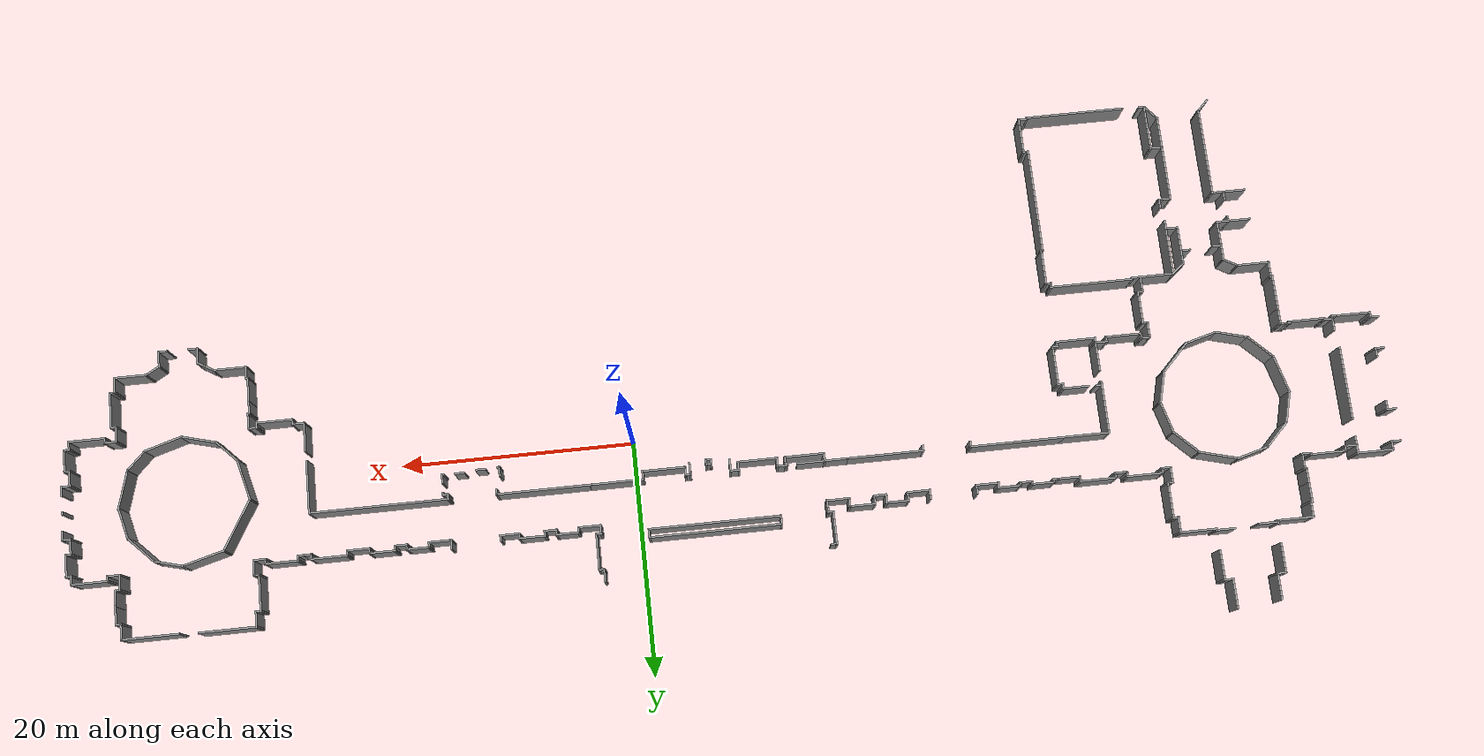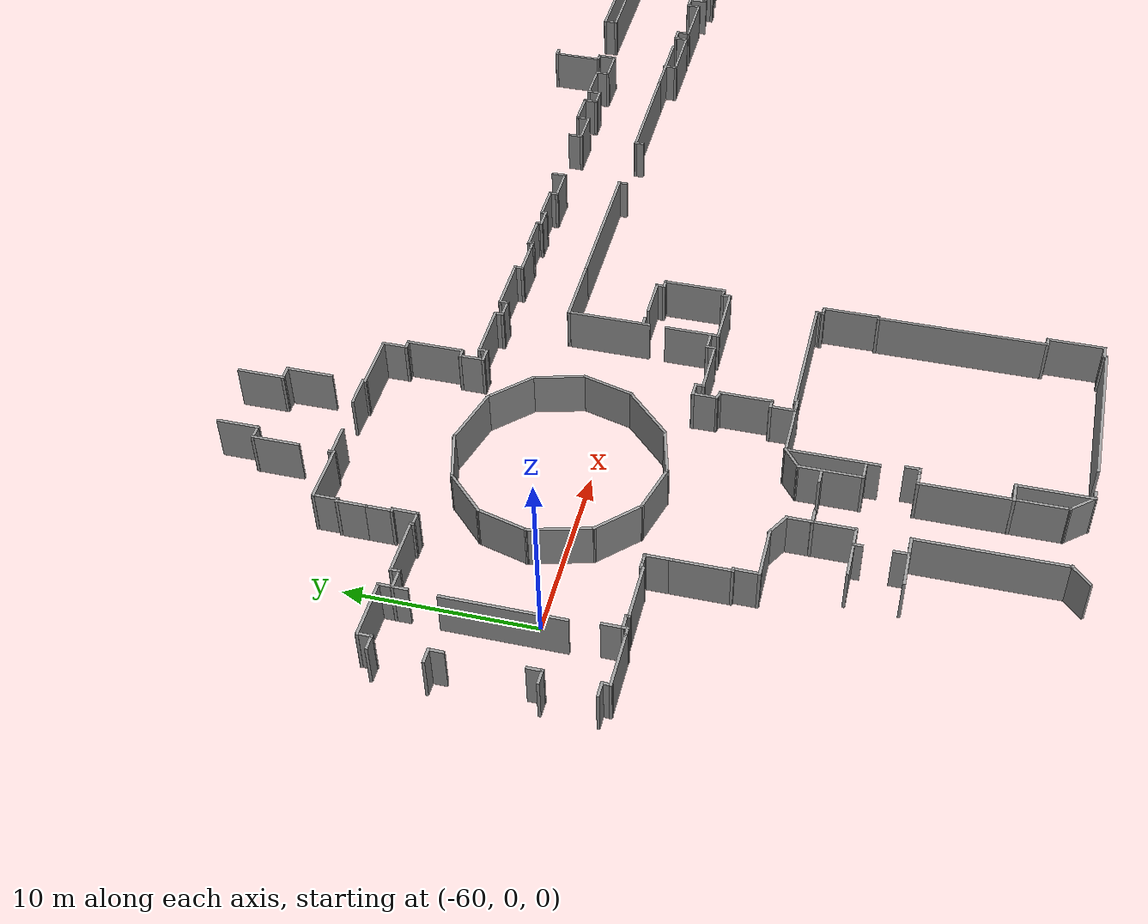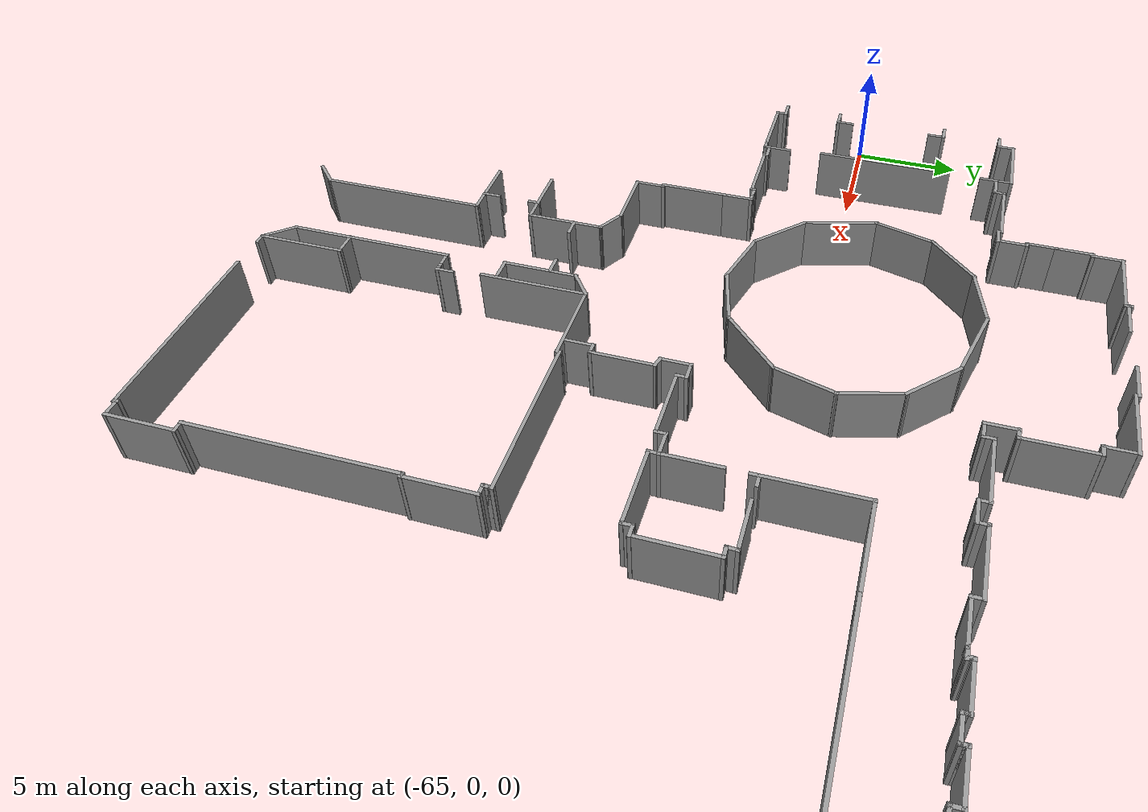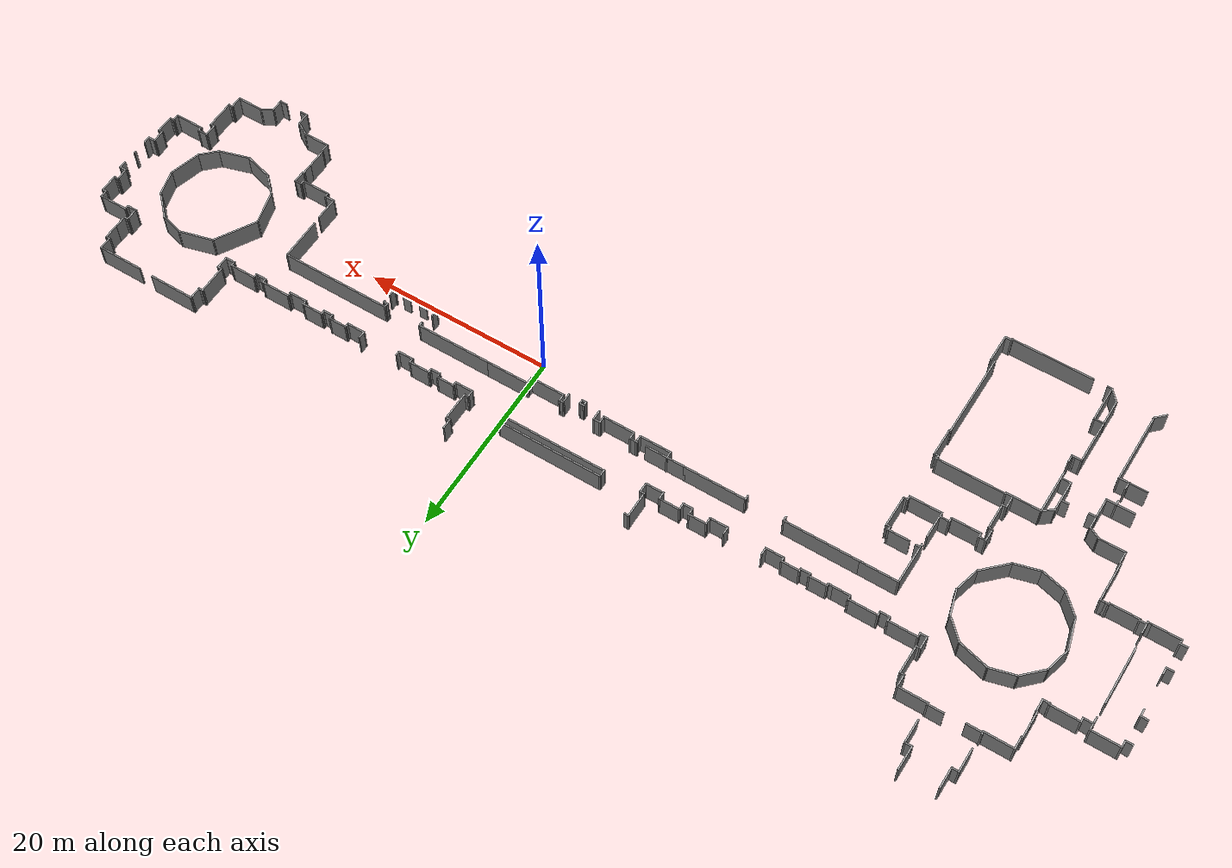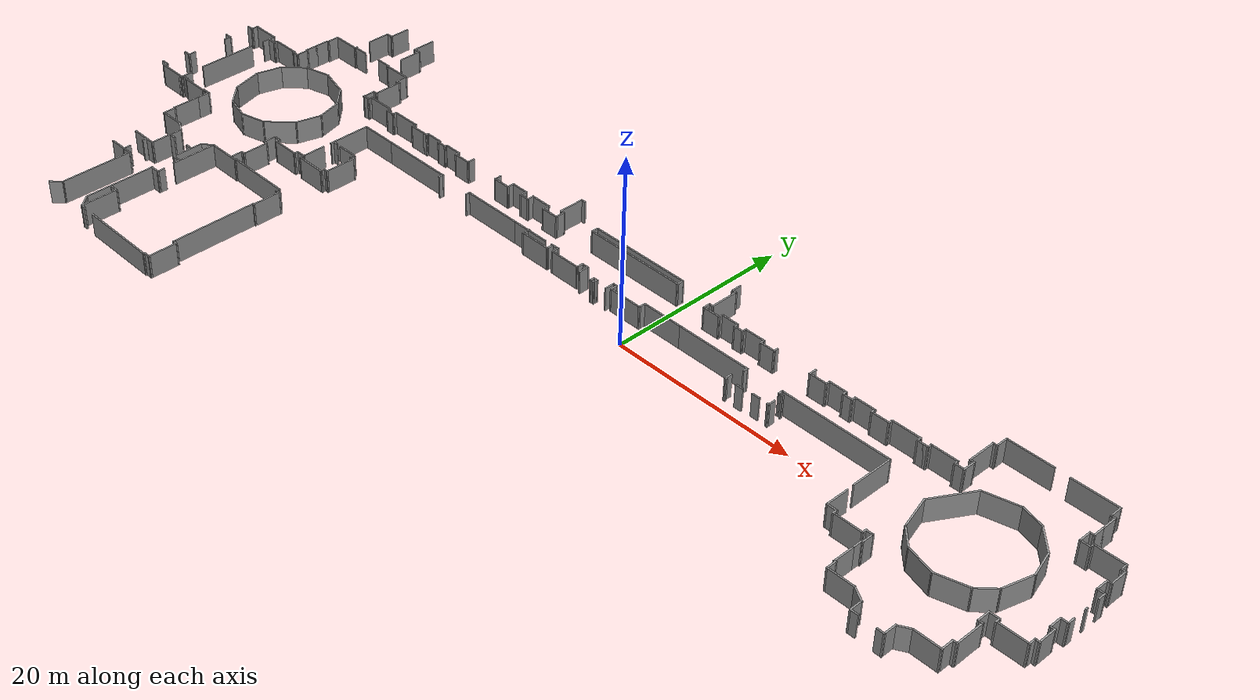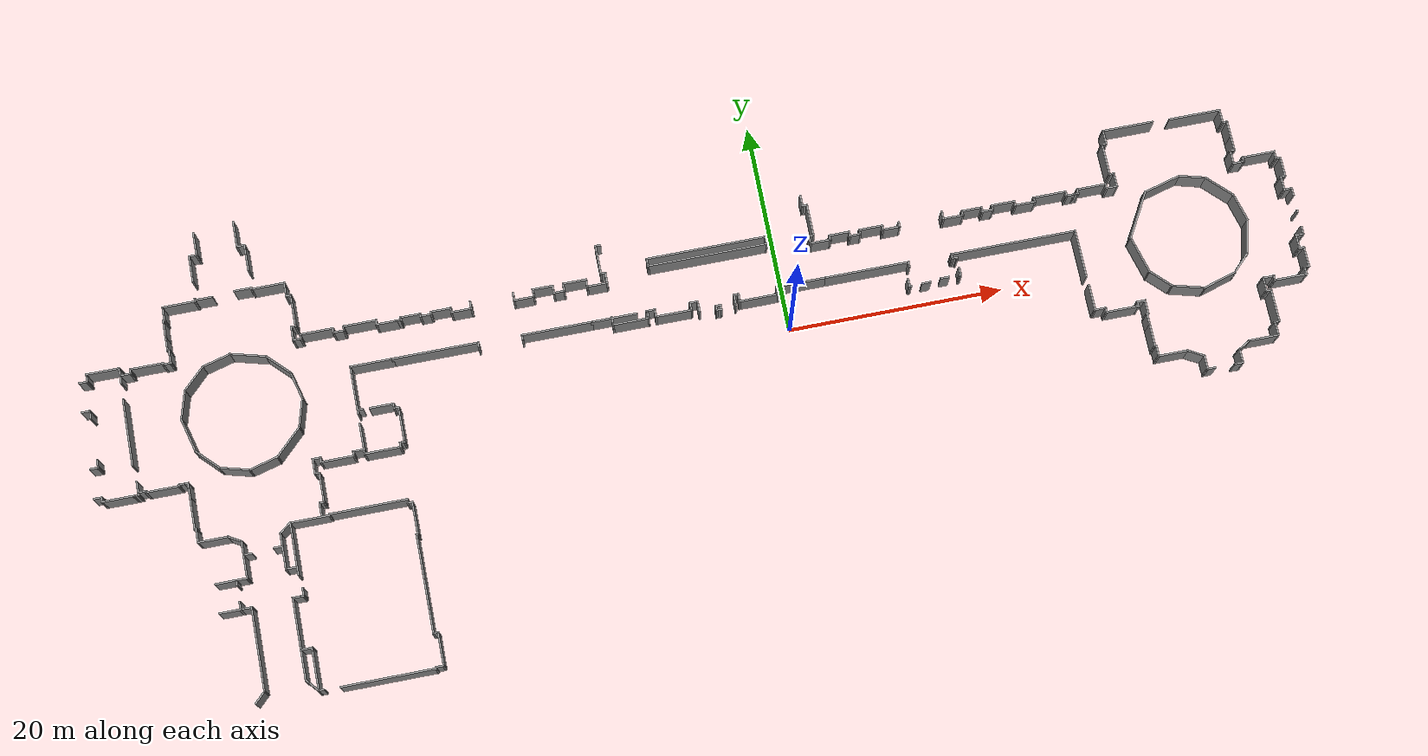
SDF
<?xml version='1.0'?>
<sdf version="1.7">
  <model name="TD_n1">
    <pose>-8.28511 -2.84735 0 0 -0 0</pose>
    <link name="Wall_0">
      <collision name="Wall_0_Collision">
        <geometry>
          <box>
            <size>3.77 0.15 2.5</size>
          </box>
        </geometry>
        <pose>0 0 1.25 0 -0 0</pose>
      </collision>
      <visual name="Wall_0_Visual">
        <pose>0 0 1.25 0 -0 0</pose>
        <geometry>
          <box>
            <size>3.77 0.15 2.5</size>
          </box>
        </geometry>
        <material>
          <script>
            <uri>file://media/materials/scripts/gazebo.material</uri>
            <name>Gazebo/Grey</name>
          </script>
          <ambient>1 1 1 1</ambient>
        </material>
        <meta>
          <layer>0</layer>
        </meta>
      </visual>
      <pose>-37.8133 -6.80732 0 0 -0 0</pose>
    </link>
    <link name="Wall_1">
      <collision name="Wall_1_Collision">
        <geometry>
          <box>
            <size>0.29 0.15 2.5</size>
          </box>
        </geometry>
        <pose>0 0 1.25 0 -0 0</pose>
      </collision>
      <visual name="Wall_1_Visual">
        <pose>0 0 1.25 0 -0 0</pose>
        <geometry>
          <box>
            <size>0.29 0.15 2.5</size>
          </box>
        </geometry>
        <material>
          <script>
            <uri>file://media/materials/scripts/gazebo.material</uri>
            <name>Gazebo/Grey</name>
          </script>
          <ambient>1 1 1 1</ambient>
        </material>
        <meta>
          <layer>0</layer>
        </meta>
      </visual>
      <pose>-36.0153 -6.74932 0 0 -0 1.5708</pose>
    </link>
    <link name="Wall_10">
      <collision name="Wall_10_Collision">
        <geometry>
          <box>
            <size>0.58 0.15 2.5</size>
          </box>
        </geometry>
        <pose>0 0 1.25 0 -0 0</pose>
      </collision>
      <visual name="Wall_10_Visual">
        <pose>0 0 1.25 0 -0 0</pose>
        <geometry>
          <box>
            <size>0.58 0.15 2.5</size>
          </box>
        </geometry>
        <material>
          <script>
            <uri>file://media/materials/scripts/gazebo.material</uri>
            <name>Gazebo/Grey</name>
          </script>
          <ambient>1 1 1 1</ambient>
        </material>
        <meta>
          <layer>0</layer>
        </meta>
      </visual>
      <pose>-28.4463 -19.1613 0 0 -0 0</pose>
    </link>
    <link name="Wall_100">
      <collision name="Wall_100_Collision">
        <geometry>
          <box>
            <size>2.32 0.15 2.5</size>
          </box>
        </geometry>
        <pose>0 0 1.25 0 -0 0</pose>
      </collision>
      <visual name="Wall_100_Visual">
        <pose>0 0 1.25 0 -0 0</pose>
        <geometry>
          <box>
            <size>2.32 0.15 2.5</size>
          </box>
        </geometry>
        <material>
          <script>
            <uri>file://media/materials/scripts/gazebo.material</uri>
            <name>Gazebo/Grey</name>
          </script>
          <ambient>1 1 1 1</ambient>
        </material>
        <meta>
          <layer>0</layer>
        </meta>
      </visual>
      <pose>-29.7887 2.31174 0 0 -0 3.14159</pose>
    </link>
    <link name="Wall_102">
      <collision name="Wall_102_Collision">
        <geometry>
          <box>
            <size>2.9 0.15 2.5</size>
          </box>
        </geometry>
        <pose>0 0 1.25 0 -0 0</pose>
      </collision>
      <visual name="Wall_102_Visual">
        <pose>0 0 1.25 0 -0 0</pose>
        <geometry>
          <box>
            <size>2.9 0.15 2.5</size>
          </box>
        </geometry>
        <material>
          <script>
            <uri>file://media/materials/scripts/gazebo.material</uri>
            <name>Gazebo/Grey</name>
          </script>
          <ambient>1 1 1 1</ambient>
        </material>
        <meta>
          <layer>0</layer>
        </meta>
      </visual>
      <pose>-43.7442 -0.919881 0 0 -0 2.87979</pose>
    </link>
    <link name="Wall_103">
      <collision name="Wall_103_Collision">
        <geometry>
          <box>
            <size>2.9 0.15 2.5</size>
          </box>
        </geometry>
        <pose>0 0 1.25 0 -0 0</pose>
      </collision>
      <visual name="Wall_103_Visual">
        <pose>0 0 1.25 0 -0 0</pose>
        <geometry>
          <box>
            <size>2.9 0.15 2.5</size>
          </box>
        </geometry>
        <material>
          <script>
            <uri>file://media/materials/scripts/gazebo.material</uri>
            <name>Gazebo/Grey</name>
          </script>
          <ambient>1 1 1 1</ambient>
        </material>
        <meta>
          <layer>0</layer>
        </meta>
      </visual>
      <pose>-46.0245 0.396676 0 0 -0 2.35619</pose>
    </link>
    <link name="Wall_104">
      <collision name="Wall_104_Collision">
        <geometry>
          <box>
            <size>3.48 0.15 2.5</size>
          </box>
        </geometry>
        <pose>0 0 1.25 0 -0 0</pose>
      </collision>
      <visual name="Wall_104_Visual">
        <pose>0 0 1.25 0 -0 0</pose>
        <geometry>
          <box>
            <size>3.48 0.15 2.5</size>
          </box>
        </geometry>
        <material>
          <script>
            <uri>file://media/materials/scripts/gazebo.material</uri>
            <name>Gazebo/Grey</name>
          </script>
          <ambient>1 1 1 1</ambient>
        </material>
        <meta>
          <layer>0</layer>
        </meta>
      </visual>
      <pose>-47.4162 2.95714 0 0 -0 1.8326</pose>
    </link>
    <link name="Wall_105">
      <collision name="Wall_105_Collision">
        <geometry>
          <box>
            <size>2.9 0.15 2.5</size>
          </box>
        </geometry>
        <pose>0 0 1.25 0 -0 0</pose>
      </collision>
      <visual name="Wall_105_Visual">
        <pose>0 0 1.25 0 -0 0</pose>
        <geometry>
          <box>
            <size>2.9 0.15 2.5</size>
          </box>
        </geometry>
        <material>
          <script>
            <uri>file://media/materials/scripts/gazebo.material</uri>
            <name>Gazebo/Grey</name>
          </script>
          <ambient>1 1 1 1</ambient>
        </material>
        <meta>
          <layer>0</layer>
        </meta>
      </visual>
      <pose>-47.4912 5.87037 0 0 -0 1.309</pose>
    </link>
    <link name="Wall_106">
      <collision name="Wall_106_Collision">
        <geometry>
          <box>
            <size>2.9 0.15 2.5</size>
          </box>
        </geometry>
        <pose>0 0 1.25 0 -0 0</pose>
      </collision>
      <visual name="Wall_106_Visual">
        <pose>0 0 1.25 0 -0 0</pose>
        <geometry>
          <box>
            <size>2.9 0.15 2.5</size>
          </box>
        </geometry>
        <material>
          <script>
            <uri>file://media/materials/scripts/gazebo.material</uri>
            <name>Gazebo/Grey</name>
          </script>
          <ambient>1 1 1 1</ambient>
        </material>
        <meta>
          <layer>0</layer>
        </meta>
      </visual>
      <pose>-46.1746 8.15072 0 0 -0 0.785398</pose>
    </link>
    <link name="Wall_107">
      <collision name="Wall_107_Collision">
        <geometry>
          <box>
            <size>2.9 0.15 2.5</size>
          </box>
        </geometry>
        <pose>0 0 1.25 0 -0 0</pose>
      </collision>
      <visual name="Wall_107_Visual">
        <pose>0 0 1.25 0 -0 0</pose>
        <geometry>
          <box>
            <size>2.9 0.15 2.5</size>
          </box>
        </geometry>
        <material>
          <script>
            <uri>file://media/materials/scripts/gazebo.material</uri>
            <name>Gazebo/Grey</name>
          </script>
          <ambient>1 1 1 1</ambient>
        </material>
        <meta>
          <layer>0</layer>
        </meta>
      </visual>
      <pose>-43.8943 9.46727 0 0 -0 0.261799</pose>
    </link>
    <link name="Wall_108">
      <collision name="Wall_108_Collision">
        <geometry>
          <box>
            <size>3.48 0.15 2.5</size>
          </box>
        </geometry>
        <pose>0 0 1.25 0 -0 0</pose>
      </collision>
      <visual name="Wall_108_Visual">
        <pose>0 0 1.25 0 -0 0</pose>
        <geometry>
          <box>
            <size>3.48 0.15 2.5</size>
          </box>
        </geometry>
        <material>
          <script>
            <uri>file://media/materials/scripts/gazebo.material</uri>
            <name>Gazebo/Grey</name>
          </script>
          <ambient>1 1 1 1</ambient>
        </material>
        <meta>
          <layer>0</layer>
        </meta>
      </visual>
      <pose>-40.9811 9.39222 0 0 -0 -0.261799</pose>
    </link>
    <link name="Wall_109">
      <collision name="Wall_109_Collision">
        <geometry>
          <box>
            <size>2.9 0.15 2.5</size>
          </box>
        </geometry>
        <pose>0 0 1.25 0 -0 0</pose>
      </collision>
      <visual name="Wall_109_Visual">
        <pose>0 0 1.25 0 -0 0</pose>
        <geometry>
          <box>
            <size>2.9 0.15 2.5</size>
          </box>
        </geometry>
        <material>
          <script>
            <uri>file://media/materials/scripts/gazebo.material</uri>
            <name>Gazebo/Grey</name>
          </script>
          <ambient>1 1 1 1</ambient>
        </material>
        <meta>
          <layer>0</layer>
        </meta>
      </visual>
      <pose>-38.4206 8.0006 0 0 -0 -0.785398</pose>
    </link>
    <link name="Wall_11">
      <collision name="Wall_11_Collision">
        <geometry>
          <box>
            <size>3.19 0.15 2.5</size>
          </box>
        </geometry>
        <pose>0 0 1.25 0 -0 0</pose>
      </collision>
      <visual name="Wall_11_Visual">
        <pose>0 0 1.25 0 -0 0</pose>
        <geometry>
          <box>
            <size>3.19 0.15 2.5</size>
          </box>
        </geometry>
        <material>
          <script>
            <uri>file://media/materials/scripts/gazebo.material</uri>
            <name>Gazebo/Grey</name>
          </script>
          <ambient>1 1 1 1</ambient>
        </material>
        <meta>
          <layer>0</layer>
        </meta>
      </visual>
      <pose>-28.2433 -20.6693 0 0 -0 -1.5708</pose>
    </link>
    <link name="Wall_110">
      <collision name="Wall_110_Collision">
        <geometry>
          <box>
            <size>2.9 0.15 2.5</size>
          </box>
        </geometry>
        <pose>0 0 1.25 0 -0 0</pose>
      </collision>
      <visual name="Wall_110_Visual">
        <pose>0 0 1.25 0 -0 0</pose>
        <geometry>
          <box>
            <size>2.9 0.15 2.5</size>
          </box>
        </geometry>
        <material>
          <script>
            <uri>file://media/materials/scripts/gazebo.material</uri>
            <name>Gazebo/Grey</name>
          </script>
          <ambient>1 1 1 1</ambient>
        </material>
        <meta>
          <layer>0</layer>
        </meta>
      </visual>
      <pose>-37.104 5.72025 0 0 -0 -1.309</pose>
    </link>
    <link name="Wall_111">
      <collision name="Wall_111_Collision">
        <geometry>
          <box>
            <size>2.9 0.15 2.5</size>
          </box>
        </geometry>
        <pose>0 0 1.25 0 -0 0</pose>
      </collision>
      <visual name="Wall_111_Visual">
        <pose>0 0 1.25 0 -0 0</pose>
        <geometry>
          <box>
            <size>2.9 0.15 2.5</size>
          </box>
        </geometry>
        <material>
          <script>
            <uri>file://media/materials/scripts/gazebo.material</uri>
            <name>Gazebo/Grey</name>
          </script>
          <ambient>1 1 1 1</ambient>
        </material>
        <meta>
          <layer>0</layer>
        </meta>
      </visual>
      <pose>-37.104 3.08714 0 0 -0 -1.8326</pose>
    </link>
    <link name="Wall_112">
      <collision name="Wall_112_Collision">
        <geometry>
          <box>
            <size>3.48 0.15 2.5</size>
          </box>
        </geometry>
        <pose>0 0 1.25 0 -0 0</pose>
      </collision>
      <visual name="Wall_112_Visual">
        <pose>0 0 1.25 0 -0 0</pose>
        <geometry>
          <box>
            <size>3.48 0.15 2.5</size>
          </box>
        </geometry>
        <material>
          <script>
            <uri>file://media/materials/scripts/gazebo.material</uri>
            <name>Gazebo/Grey</name>
          </script>
          <ambient>1 1 1 1</ambient>
        </material>
        <meta>
          <layer>0</layer>
        </meta>
      </visual>
      <pose>-38.6257 0.601737 0 0 -0 -2.35619</pose>
    </link>
    <link name="Wall_113">
      <collision name="Wall_113_Collision">
        <geometry>
          <box>
            <size>2.9 0.15 2.5</size>
          </box>
        </geometry>
        <pose>0 0 1.25 0 -0 0</pose>
      </collision>
      <visual name="Wall_113_Visual">
        <pose>0 0 1.25 0 -0 0</pose>
        <geometry>
          <box>
            <size>2.9 0.15 2.5</size>
          </box>
        </geometry>
        <material>
          <script>
            <uri>file://media/materials/scripts/gazebo.material</uri>
            <name>Gazebo/Grey</name>
          </script>
          <ambient>1 1 1 1</ambient>
        </material>
        <meta>
          <layer>0</layer>
        </meta>
      </visual>
      <pose>-41.1111 -0.919881 0 0 -0 -2.87979</pose>
    </link>
    <link name="Wall_115">
      <collision name="Wall_115_Collision">
        <geometry>
          <box>
            <size>0.87 0.15 2.5</size>
          </box>
        </geometry>
        <pose>0 0 1.25 0 -0 0</pose>
      </collision>
      <visual name="Wall_115_Visual">
        <pose>0 0 1.25 0 -0 0</pose>
        <geometry>
          <box>
            <size>0.87 0.15 2.5</size>
          </box>
        </geometry>
        <material>
          <script>
            <uri>file://media/materials/scripts/gazebo.material</uri>
            <name>Gazebo/Grey</name>
          </script>
          <ambient>1 1 1 1</ambient>
        </material>
        <meta>
          <layer>0</layer>
        </meta>
      </visual>
      <pose>-52.7309 9.37865 0 0 -0 1.5708</pose>
    </link>
    <link name="Wall_116">
      <collision name="Wall_116_Collision">
        <geometry>
          <box>
            <size>1.16 0.15 2.5</size>
          </box>
        </geometry>
        <pose>0 0 1.25 0 -0 0</pose>
      </collision>
      <visual name="Wall_116_Visual">
        <pose>0 0 1.25 0 -0 0</pose>
        <geometry>
          <box>
            <size>1.16 0.15 2.5</size>
          </box>
        </geometry>
        <material>
          <script>
            <uri>file://media/materials/scripts/gazebo.material</uri>
            <name>Gazebo/Grey</name>
          </script>
          <ambient>1 1 1 1</ambient>
        </material>
        <meta>
          <layer>0</layer>
        </meta>
      </visual>
      <pose>-52.2379 9.72665 0 0 -0 0</pose>
    </link>
    <link name="Wall_117">
      <collision name="Wall_117_Collision">
        <geometry>
          <box>
            <size>0.58 0.15 2.5</size>
          </box>
        </geometry>
        <pose>0 0 1.25 0 -0 0</pose>
      </collision>
      <visual name="Wall_117_Visual">
        <pose>0 0 1.25 0 -0 0</pose>
        <geometry>
          <box>
            <size>0.58 0.15 2.5</size>
          </box>
        </geometry>
        <material>
          <script>
            <uri>file://media/materials/scripts/gazebo.material</uri>
            <name>Gazebo/Grey</name>
          </script>
          <ambient>1 1 1 1</ambient>
        </material>
        <meta>
          <layer>0</layer>
        </meta>
      </visual>
      <pose>-51.7449 9.92965 0 0 -0 1.5708</pose>
    </link>
    <link name="Wall_118">
      <collision name="Wall_118_Collision">
        <geometry>
          <box>
            <size>3.19 0.15 2.5</size>
          </box>
        </geometry>
        <pose>0 0 1.25 0 -0 0</pose>
      </collision>
      <visual name="Wall_118_Visual">
        <pose>0 0 1.25 0 -0 0</pose>
        <geometry>
          <box>
            <size>3.19 0.15 2.5</size>
          </box>
        </geometry>
        <material>
          <script>
            <uri>file://media/materials/scripts/gazebo.material</uri>
            <name>Gazebo/Grey</name>
          </script>
          <ambient>1 1 1 1</ambient>
        </material>
        <meta>
          <layer>0</layer>
        </meta>
      </visual>
      <pose>-50.2369 10.1326 0 0 -0 0</pose>
    </link>
    <link name="Wall_12">
      <collision name="Wall_12_Collision">
        <geometry>
          <box>
            <size>0.87 0.15 2.5</size>
          </box>
        </geometry>
        <pose>0 0 1.25 0 -0 0</pose>
      </collision>
      <visual name="Wall_12_Visual">
        <pose>0 0 1.25 0 -0 0</pose>
        <geometry>
          <box>
            <size>0.87 0.15 2.5</size>
          </box>
        </geometry>
        <material>
          <script>
            <uri>file://media/materials/scripts/gazebo.material</uri>
            <name>Gazebo/Grey</name>
          </script>
          <ambient>1 1 1 1</ambient>
        </material>
        <meta>
          <layer>0</layer>
        </meta>
      </visual>
      <pose>-28.5913 -22.1773 0 0 -0 3.14159</pose>
    </link>
    <link name="Wall_121">
      <collision name="Wall_121_Collision">
        <geometry>
          <box>
            <size>0.29 0.15 2.5</size>
          </box>
        </geometry>
        <pose>0 0 1.25 0 -0 0</pose>
      </collision>
      <visual name="Wall_121_Visual">
        <pose>0 0 1.25 0 -0 0</pose>
        <geometry>
          <box>
            <size>0.29 0.15 2.5</size>
          </box>
        </geometry>
        <material>
          <script>
            <uri>file://media/materials/scripts/gazebo.material</uri>
            <name>Gazebo/Grey</name>
          </script>
          <ambient>1 1 1 1</ambient>
        </material>
        <meta>
          <layer>0</layer>
        </meta>
      </visual>
      <pose>-48.7289 10.0746 0 0 -0 -1.5708</pose>
    </link>
    <link name="Wall_122">
      <collision name="Wall_122_Collision">
        <geometry>
          <box>
            <size>0.87 0.15 2.5</size>
          </box>
        </geometry>
        <pose>0 0 1.25 0 -0 0</pose>
      </collision>
      <visual name="Wall_122_Visual">
        <pose>0 0 1.25 0 -0 0</pose>
        <geometry>
          <box>
            <size>0.87 0.15 2.5</size>
          </box>
        </geometry>
        <material>
          <script>
            <uri>file://media/materials/scripts/gazebo.material</uri>
            <name>Gazebo/Grey</name>
          </script>
          <ambient>1 1 1 1</ambient>
        </material>
        <meta>
          <layer>0</layer>
        </meta>
      </visual>
      <pose>-48.3809 10.0166 0 0 -0 0</pose>
    </link>
    <link name="Wall_123">
      <collision name="Wall_123_Collision">
        <geometry>
          <box>
            <size>1.45 0.15 2.5</size>
          </box>
        </geometry>
        <pose>0 0 1.25 0 -0 0</pose>
      </collision>
      <visual name="Wall_123_Visual">
        <pose>0 0 1.25 0 -0 0</pose>
        <geometry>
          <box>
            <size>1.45 0.15 2.5</size>
          </box>
        </geometry>
        <material>
          <script>
            <uri>file://media/materials/scripts/gazebo.material</uri>
            <name>Gazebo/Grey</name>
          </script>
          <ambient>1 1 1 1</ambient>
        </material>
        <meta>
          <layer>0</layer>
        </meta>
      </visual>
      <pose>-48.0329 10.6546 0 0 -0 1.5708</pose>
    </link>
    <link name="Wall_124">
      <collision name="Wall_124_Collision">
        <geometry>
          <box>
            <size>0.29 0.15 2.5</size>
          </box>
        </geometry>
        <pose>0 0 1.25 0 -0 0</pose>
      </collision>
      <visual name="Wall_124_Visual">
        <pose>0 0 1.25 0 -0 0</pose>
        <geometry>
          <box>
            <size>0.29 0.15 2.5</size>
          </box>
        </geometry>
        <material>
          <script>
            <uri>file://media/materials/scripts/gazebo.material</uri>
            <name>Gazebo/Grey</name>
          </script>
          <ambient>1 1 1 1</ambient>
        </material>
        <meta>
          <layer>0</layer>
        </meta>
      </visual>
      <pose>-48.0909 11.2926 0 0 -0 3.14159</pose>
    </link>
    <link name="Wall_125">
      <collision name="Wall_125_Collision">
        <geometry>
          <box>
            <size>1.45 0.15 2.5</size>
          </box>
        </geometry>
        <pose>0 0 1.25 0 -0 0</pose>
      </collision>
      <visual name="Wall_125_Visual">
        <pose>0 0 1.25 0 -0 0</pose>
        <geometry>
          <box>
            <size>1.45 0.15 2.5</size>
          </box>
        </geometry>
        <material>
          <script>
            <uri>file://media/materials/scripts/gazebo.material</uri>
            <name>Gazebo/Grey</name>
          </script>
          <ambient>1 1 1 1</ambient>
        </material>
        <meta>
          <layer>0</layer>
        </meta>
      </visual>
      <pose>-48.1489 11.9306 0 0 -0 1.5708</pose>
    </link>
    <link name="Wall_127">
      <collision name="Wall_127_Collision">
        <geometry>
          <box>
            <size>1.74 0.15 2.5</size>
          </box>
        </geometry>
        <pose>0 0 1.25 0 -0 0</pose>
      </collision>
      <visual name="Wall_127_Visual">
        <pose>0 0 1.25 0 -0 0</pose>
        <geometry>
          <box>
            <size>1.74 0.15 2.5</size>
          </box>
        </geometry>
        <material>
          <script>
            <uri>file://media/materials/scripts/gazebo.material</uri>
            <name>Gazebo/Grey</name>
          </script>
          <ambient>1 1 1 1</ambient>
        </material>
        <meta>
          <layer>0</layer>
        </meta>
      </visual>
      <pose>-48.1489 13.3516 0 0 -0 1.5708</pose>
    </link>
    <link name="Wall_128">
      <collision name="Wall_128_Collision">
        <geometry>
          <box>
            <size>0.29 0.15 2.5</size>
          </box>
        </geometry>
        <pose>0 0 1.25 0 -0 0</pose>
      </collision>
      <visual name="Wall_128_Visual">
        <pose>0 0 1.25 0 -0 0</pose>
        <geometry>
          <box>
            <size>0.29 0.15 2.5</size>
          </box>
        </geometry>
        <material>
          <script>
            <uri>file://media/materials/scripts/gazebo.material</uri>
            <name>Gazebo/Grey</name>
          </script>
          <ambient>1 1 1 1</ambient>
        </material>
        <meta>
          <layer>0</layer>
        </meta>
      </visual>
      <pose>-48.0909 14.1346 0 0 -0 0</pose>
    </link>
    <link name="Wall_129">
      <collision name="Wall_129_Collision">
        <geometry>
          <box>
            <size>1.45 0.15 2.5</size>
          </box>
        </geometry>
        <pose>0 0 1.25 0 -0 0</pose>
      </collision>
      <visual name="Wall_129_Visual">
        <pose>0 0 1.25 0 -0 0</pose>
        <geometry>
          <box>
            <size>1.45 0.15 2.5</size>
          </box>
        </geometry>
        <material>
          <script>
            <uri>file://media/materials/scripts/gazebo.material</uri>
            <name>Gazebo/Grey</name>
          </script>
          <ambient>1 1 1 1</ambient>
        </material>
        <meta>
          <layer>0</layer>
        </meta>
      </visual>
      <pose>-48.0329 14.7726 0 0 -0 1.5708</pose>
    </link>
    <link name="Wall_13">
      <collision name="Wall_13_Collision">
        <geometry>
          <box>
            <size>0.29 0.15 2.5</size>
          </box>
        </geometry>
        <pose>0 0 1.25 0 -0 0</pose>
      </collision>
      <visual name="Wall_13_Visual">
        <pose>0 0 1.25 0 -0 0</pose>
        <geometry>
          <box>
            <size>0.29 0.15 2.5</size>
          </box>
        </geometry>
        <material>
          <script>
            <uri>file://media/materials/scripts/gazebo.material</uri>
            <name>Gazebo/Grey</name>
          </script>
          <ambient>1 1 1 1</ambient>
        </material>
        <meta>
          <layer>0</layer>
        </meta>
      </visual>
      <pose>-28.9393 -22.2353 0 0 -0 -1.5708</pose>
    </link>
    <link name="Wall_130">
      <collision name="Wall_130_Collision">
        <geometry>
          <box>
            <size>3.19 0.15 2.5</size>
          </box>
        </geometry>
        <pose>0 0 1.25 0 -0 0</pose>
      </collision>
      <visual name="Wall_130_Visual">
        <pose>0 0 1.25 0 -0 0</pose>
        <geometry>
          <box>
            <size>3.19 0.15 2.5</size>
          </box>
        </geometry>
        <material>
          <script>
            <uri>file://media/materials/scripts/gazebo.material</uri>
            <name>Gazebo/Grey</name>
          </script>
          <ambient>1 1 1 1</ambient>
        </material>
        <meta>
          <layer>0</layer>
        </meta>
      </visual>
      <pose>-46.5249 15.4106 0 0 -0 0</pose>
    </link>
    <link name="Wall_131">
      <collision name="Wall_131_Collision">
        <geometry>
          <box>
            <size>0.29 0.15 2.5</size>
          </box>
        </geometry>
        <pose>0 0 1.25 0 -0 0</pose>
      </collision>
      <visual name="Wall_131_Visual">
        <pose>0 0 1.25 0 -0 0</pose>
        <geometry>
          <box>
            <size>0.29 0.15 2.5</size>
          </box>
        </geometry>
        <material>
          <script>
            <uri>file://media/materials/scripts/gazebo.material</uri>
            <name>Gazebo/Grey</name>
          </script>
          <ambient>1 1 1 1</ambient>
        </material>
        <meta>
          <layer>0</layer>
        </meta>
      </visual>
      <pose>-45.0169 15.4686 0 0 -0 1.5708</pose>
    </link>
    <link name="Wall_132">
      <collision name="Wall_132_Collision">
        <geometry>
          <box>
            <size>1.74 0.15 2.5</size>
          </box>
        </geometry>
        <pose>0 0 1.25 0 -0 0</pose>
      </collision>
      <visual name="Wall_132_Visual">
        <pose>0 0 1.25 0 -0 0</pose>
        <geometry>
          <box>
            <size>1.74 0.15 2.5</size>
          </box>
        </geometry>
        <material>
          <script>
            <uri>file://media/materials/scripts/gazebo.material</uri>
            <name>Gazebo/Grey</name>
          </script>
          <ambient>1 1 1 1</ambient>
        </material>
        <meta>
          <layer>0</layer>
        </meta>
      </visual>
      <pose>-44.2339 15.5266 0 0 -0 0</pose>
    </link>
    <link name="Wall_134">
      <collision name="Wall_134_Collision">
        <geometry>
          <box>
            <size>1.74 0.15 2.5</size>
          </box>
        </geometry>
        <pose>0 0 1.25 0 -0 0</pose>
      </collision>
      <visual name="Wall_134_Visual">
        <pose>0 0 1.25 0 -0 0</pose>
        <geometry>
          <box>
            <size>1.74 0.15 2.5</size>
          </box>
        </geometry>
        <material>
          <script>
            <uri>file://media/materials/scripts/gazebo.material</uri>
            <name>Gazebo/Grey</name>
          </script>
          <ambient>1 1 1 1</ambient>
        </material>
        <meta>
          <layer>0</layer>
        </meta>
      </visual>
      <pose>-40.527 15.6964 0 0 -0 0</pose>
    </link>
    <link name="Wall_135">
      <collision name="Wall_135_Collision">
        <geometry>
          <box>
            <size>0.29 0.15 2.5</size>
          </box>
        </geometry>
        <pose>0 0 1.25 0 -0 0</pose>
      </collision>
      <visual name="Wall_135_Visual">
        <pose>0 0 1.25 0 -0 0</pose>
        <geometry>
          <box>
            <size>0.29 0.15 2.5</size>
          </box>
        </geometry>
        <material>
          <script>
            <uri>file://media/materials/scripts/gazebo.material</uri>
            <name>Gazebo/Grey</name>
          </script>
          <ambient>1 1 1 1</ambient>
        </material>
        <meta>
          <layer>0</layer>
        </meta>
      </visual>
      <pose>-39.744 15.6384 0 0 -0 -1.5708</pose>
    </link>
    <link name="Wall_136">
      <collision name="Wall_136_Collision">
        <geometry>
          <box>
            <size>3.19 0.15 2.5</size>
          </box>
        </geometry>
        <pose>0 0 1.25 0 -0 0</pose>
      </collision>
      <visual name="Wall_136_Visual">
        <pose>0 0 1.25 0 -0 0</pose>
        <geometry>
          <box>
            <size>3.19 0.15 2.5</size>
          </box>
        </geometry>
        <material>
          <script>
            <uri>file://media/materials/scripts/gazebo.material</uri>
            <name>Gazebo/Grey</name>
          </script>
          <ambient>1 1 1 1</ambient>
        </material>
        <meta>
          <layer>0</layer>
        </meta>
      </visual>
      <pose>-38.236 15.5804 0 0 -0 0</pose>
    </link>
    <link name="Wall_137">
      <collision name="Wall_137_Collision">
        <geometry>
          <box>
            <size>1.45 0.15 2.5</size>
          </box>
        </geometry>
        <pose>0 0 1.25 0 -0 0</pose>
      </collision>
      <visual name="Wall_137_Visual">
        <pose>0 0 1.25 0 -0 0</pose>
        <geometry>
          <box>
            <size>1.45 0.15 2.5</size>
          </box>
        </geometry>
        <material>
          <script>
            <uri>file://media/materials/scripts/gazebo.material</uri>
            <name>Gazebo/Grey</name>
          </script>
          <ambient>1 1 1 1</ambient>
        </material>
        <meta>
          <layer>0</layer>
        </meta>
      </visual>
      <pose>-36.728 14.9424 0 0 -0 -1.5708</pose>
    </link>
    <link name="Wall_138">
      <collision name="Wall_138_Collision">
        <geometry>
          <box>
            <size>0.58 0.15 2.5</size>
          </box>
        </geometry>
        <pose>0 0 1.25 0 -0 0</pose>
      </collision>
      <visual name="Wall_138_Visual">
        <pose>0 0 1.25 0 -0 0</pose>
        <geometry>
          <box>
            <size>0.58 0.15 2.5</size>
          </box>
        </geometry>
        <material>
          <script>
            <uri>file://media/materials/scripts/gazebo.material</uri>
            <name>Gazebo/Grey</name>
          </script>
          <ambient>1 1 1 1</ambient>
        </material>
        <meta>
          <layer>0</layer>
        </meta>
      </visual>
      <pose>-36.525 14.3044 0 0 -0 0</pose>
    </link>
    <link name="Wall_139">
      <collision name="Wall_139_Collision">
        <geometry>
          <box>
            <size>3.19 0.15 2.5</size>
          </box>
        </geometry>
        <pose>0 0 1.25 0 -0 0</pose>
      </collision>
      <visual name="Wall_139_Visual">
        <pose>0 0 1.25 0 -0 0</pose>
        <geometry>
          <box>
            <size>3.19 0.15 2.5</size>
          </box>
        </geometry>
        <material>
          <script>
            <uri>file://media/materials/scripts/gazebo.material</uri>
            <name>Gazebo/Grey</name>
          </script>
          <ambient>1 1 1 1</ambient>
        </material>
        <meta>
          <layer>0</layer>
        </meta>
      </visual>
      <pose>-36.322 12.7964 0 0 -0 -1.5708</pose>
    </link>
    <link name="Wall_14">
      <collision name="Wall_14_Collision">
        <geometry>
          <box>
            <size>8.7 0.15 2.5</size>
          </box>
        </geometry>
        <pose>0 0 1.25 0 -0 0</pose>
      </collision>
      <visual name="Wall_14_Visual">
        <pose>0 0 1.25 0 -0 0</pose>
        <geometry>
          <box>
            <size>8.7 0.15 2.5</size>
          </box>
        </geometry>
        <material>
          <script>
            <uri>file://media/materials/scripts/gazebo.material</uri>
            <name>Gazebo/Grey</name>
          </script>
          <ambient>1 1 1 1</ambient>
        </material>
        <meta>
          <layer>0</layer>
        </meta>
      </visual>
      <pose>-33.2023 -22.2933 0 0 -0 3.14159</pose>
    </link>
    <link name="Wall_141">
      <collision name="Wall_141_Collision">
        <geometry>
          <box>
            <size>0.58 0.15 2.5</size>
          </box>
        </geometry>
        <pose>0 0 1.25 0 -0 0</pose>
      </collision>
      <visual name="Wall_141_Visual">
        <pose>0 0 1.25 0 -0 0</pose>
        <geometry>
          <box>
            <size>0.58 0.15 2.5</size>
          </box>
        </geometry>
        <material>
          <script>
            <uri>file://media/materials/scripts/gazebo.material</uri>
            <name>Gazebo/Grey</name>
          </script>
          <ambient>1 1 1 1</ambient>
        </material>
        <meta>
          <layer>0</layer>
        </meta>
      </visual>
      <pose>-36.525 11.2884 0 0 -0 3.14159</pose>
    </link>
    <link name="Wall_142">
      <collision name="Wall_142_Collision">
        <geometry>
          <box>
            <size>1.45 0.15 2.5</size>
          </box>
        </geometry>
        <pose>0 0 1.25 0 -0 0</pose>
      </collision>
      <visual name="Wall_142_Visual">
        <pose>0 0 1.25 0 -0 0</pose>
        <geometry>
          <box>
            <size>1.45 0.15 2.5</size>
          </box>
        </geometry>
        <material>
          <script>
            <uri>file://media/materials/scripts/gazebo.material</uri>
            <name>Gazebo/Grey</name>
          </script>
          <ambient>1 1 1 1</ambient>
        </material>
        <meta>
          <layer>0</layer>
        </meta>
      </visual>
      <pose>-36.728 10.6504 0 0 -0 -1.5708</pose>
    </link>
    <link name="Wall_143">
      <collision name="Wall_143_Collision">
        <geometry>
          <box>
            <size>0.87 0.15 2.5</size>
          </box>
        </geometry>
        <pose>0 0 1.25 0 -0 0</pose>
      </collision>
      <visual name="Wall_143_Visual">
        <pose>0 0 1.25 0 -0 0</pose>
        <geometry>
          <box>
            <size>0.87 0.15 2.5</size>
          </box>
        </geometry>
        <material>
          <script>
            <uri>file://media/materials/scripts/gazebo.material</uri>
            <name>Gazebo/Grey</name>
          </script>
          <ambient>1 1 1 1</ambient>
        </material>
        <meta>
          <layer>0</layer>
        </meta>
      </visual>
      <pose>-36.38 10.0124 0 0 -0 0</pose>
    </link>
    <link name="Wall_144">
      <collision name="Wall_144_Collision">
        <geometry>
          <box>
            <size>0.58 0.15 2.5</size>
          </box>
        </geometry>
        <pose>0 0 1.25 0 -0 0</pose>
      </collision>
      <visual name="Wall_144_Visual">
        <pose>0 0 1.25 0 -0 0</pose>
        <geometry>
          <box>
            <size>0.58 0.15 2.5</size>
          </box>
        </geometry>
        <material>
          <script>
            <uri>file://media/materials/scripts/gazebo.material</uri>
            <name>Gazebo/Grey</name>
          </script>
          <ambient>1 1 1 1</ambient>
        </material>
        <meta>
          <layer>0</layer>
        </meta>
      </visual>
      <pose>-36.032 10.2154 0 0 -0 1.5708</pose>
    </link>
    <link name="Wall_145">
      <collision name="Wall_145_Collision">
        <geometry>
          <box>
            <size>3.19 0.15 2.5</size>
          </box>
        </geometry>
        <pose>0 0 1.25 0 -0 0</pose>
      </collision>
      <visual name="Wall_145_Visual">
        <pose>0 0 1.25 0 -0 0</pose>
        <geometry>
          <box>
            <size>3.19 0.15 2.5</size>
          </box>
        </geometry>
        <material>
          <script>
            <uri>file://media/materials/scripts/gazebo.material</uri>
            <name>Gazebo/Grey</name>
          </script>
          <ambient>1 1 1 1</ambient>
        </material>
        <meta>
          <layer>0</layer>
        </meta>
      </visual>
      <pose>-34.524 10.4184 0 0 -0 0</pose>
    </link>
    <link name="Wall_146">
      <collision name="Wall_146_Collision">
        <geometry>
          <box>
            <size>0.58 0.15 2.5</size>
          </box>
        </geometry>
        <pose>0 0 1.25 0 -0 0</pose>
      </collision>
      <visual name="Wall_146_Visual">
        <pose>0 0 1.25 0 -0 0</pose>
        <geometry>
          <box>
            <size>0.58 0.15 2.5</size>
          </box>
        </geometry>
        <material>
          <script>
            <uri>file://media/materials/scripts/gazebo.material</uri>
            <name>Gazebo/Grey</name>
          </script>
          <ambient>1 1 1 1</ambient>
        </material>
        <meta>
          <layer>0</layer>
        </meta>
      </visual>
      <pose>-33.016 10.2154 0 0 -0 -1.5708</pose>
    </link>
    <link name="Wall_147">
      <collision name="Wall_147_Collision">
        <geometry>
          <box>
            <size>1.16 0.15 2.5</size>
          </box>
        </geometry>
        <pose>0 0 1.25 0 -0 0</pose>
      </collision>
      <visual name="Wall_147_Visual">
        <pose>0 0 1.25 0 -0 0</pose>
        <geometry>
          <box>
            <size>1.16 0.15 2.5</size>
          </box>
        </geometry>
        <material>
          <script>
            <uri>file://media/materials/scripts/gazebo.material</uri>
            <name>Gazebo/Grey</name>
          </script>
          <ambient>1 1 1 1</ambient>
        </material>
        <meta>
          <layer>0</layer>
        </meta>
      </visual>
      <pose>-32.523 10.0124 0 0 -0 0</pose>
    </link>
    <link name="Wall_148">
      <collision name="Wall_148_Collision">
        <geometry>
          <box>
            <size>0.58 0.15 2.5</size>
          </box>
        </geometry>
        <pose>0 0 1.25 0 -0 0</pose>
      </collision>
      <visual name="Wall_148_Visual">
        <pose>0 0 1.25 0 -0 0</pose>
        <geometry>
          <box>
            <size>0.58 0.15 2.5</size>
          </box>
        </geometry>
        <material>
          <script>
            <uri>file://media/materials/scripts/gazebo.material</uri>
            <name>Gazebo/Grey</name>
          </script>
          <ambient>1 1 1 1</ambient>
        </material>
        <meta>
          <layer>0</layer>
        </meta>
      </visual>
      <pose>-32.03 10.2154 0 0 -0 1.5708</pose>
    </link>
    <link name="Wall_149">
      <collision name="Wall_149_Collision">
        <geometry>
          <box>
            <size>3.19 0.15 2.5</size>
          </box>
        </geometry>
        <pose>0 0 1.25 0 -0 0</pose>
      </collision>
      <visual name="Wall_149_Visual">
        <pose>0 0 1.25 0 -0 0</pose>
        <geometry>
          <box>
            <size>3.19 0.15 2.5</size>
          </box>
        </geometry>
        <material>
          <script>
            <uri>file://media/materials/scripts/gazebo.material</uri>
            <name>Gazebo/Grey</name>
          </script>
          <ambient>1 1 1 1</ambient>
        </material>
        <meta>
          <layer>0</layer>
        </meta>
      </visual>
      <pose>-30.522 10.4184 0 0 -0 0</pose>
    </link>
    <link name="Wall_150">
      <collision name="Wall_150_Collision">
        <geometry>
          <box>
            <size>0.58 0.15 2.5</size>
          </box>
        </geometry>
        <pose>0 0 1.25 0 -0 0</pose>
      </collision>
      <visual name="Wall_150_Visual">
        <pose>0 0 1.25 0 -0 0</pose>
        <geometry>
          <box>
            <size>0.58 0.15 2.5</size>
          </box>
        </geometry>
        <material>
          <script>
            <uri>file://media/materials/scripts/gazebo.material</uri>
            <name>Gazebo/Grey</name>
          </script>
          <ambient>1 1 1 1</ambient>
        </material>
        <meta>
          <layer>0</layer>
        </meta>
      </visual>
      <pose>-29.014 10.2154 0 0 -0 -1.5708</pose>
    </link>
    <link name="Wall_151">
      <collision name="Wall_151_Collision">
        <geometry>
          <box>
            <size>2.03 0.15 2.5</size>
          </box>
        </geometry>
        <pose>0 0 1.25 0 -0 0</pose>
      </collision>
      <visual name="Wall_151_Visual">
        <pose>0 0 1.25 0 -0 0</pose>
        <geometry>
          <box>
            <size>2.03 0.15 2.5</size>
          </box>
        </geometry>
        <material>
          <script>
            <uri>file://media/materials/scripts/gazebo.material</uri>
            <name>Gazebo/Grey</name>
          </script>
          <ambient>1 1 1 1</ambient>
        </material>
        <meta>
          <layer>0</layer>
        </meta>
      </visual>
      <pose>-28.086 10.0124 0 0 -0 0</pose>
    </link>
    <link name="Wall_152">
      <collision name="Wall_152_Collision">
        <geometry>
          <box>
            <size>0.58 0.15 2.5</size>
          </box>
        </geometry>
        <pose>0 0 1.25 0 -0 0</pose>
      </collision>
      <visual name="Wall_152_Visual">
        <pose>0 0 1.25 0 -0 0</pose>
        <geometry>
          <box>
            <size>0.58 0.15 2.5</size>
          </box>
        </geometry>
        <material>
          <script>
            <uri>file://media/materials/scripts/gazebo.material</uri>
            <name>Gazebo/Grey</name>
          </script>
          <ambient>1 1 1 1</ambient>
        </material>
        <meta>
          <layer>0</layer>
        </meta>
      </visual>
      <pose>-26.955 10.0124 0 0 -0 0</pose>
    </link>
    <link name="Wall_153">
      <collision name="Wall_153_Collision">
        <geometry>
          <box>
            <size>0.29 0.15 2.5</size>
          </box>
        </geometry>
        <pose>0 0 1.25 0 -0 0</pose>
      </collision>
      <visual name="Wall_153_Visual">
        <pose>0 0 1.25 0 -0 0</pose>
        <geometry>
          <box>
            <size>0.29 0.15 2.5</size>
          </box>
        </geometry>
        <material>
          <script>
            <uri>file://media/materials/scripts/gazebo.material</uri>
            <name>Gazebo/Grey</name>
          </script>
          <ambient>1 1 1 1</ambient>
        </material>
        <meta>
          <layer>0</layer>
        </meta>
      </visual>
      <pose>-26.7671 10.0684 0 0 -0 1.8326</pose>
    </link>
    <link name="Wall_154">
      <collision name="Wall_154_Collision">
        <geometry>
          <box>
            <size>0.29 0.15 2.5</size>
          </box>
        </geometry>
        <pose>0 0 1.25 0 -0 0</pose>
      </collision>
      <visual name="Wall_154_Visual">
        <pose>0 0 1.25 0 -0 0</pose>
        <geometry>
          <box>
            <size>0.29 0.15 2.5</size>
          </box>
        </geometry>
        <material>
          <script>
            <uri>file://media/materials/scripts/gazebo.material</uri>
            <name>Gazebo/Grey</name>
          </script>
          <ambient>1 1 1 1</ambient>
        </material>
        <meta>
          <layer>0</layer>
        </meta>
      </visual>
      <pose>-26.7821 10.1824 0 0 -0 1.5708</pose>
    </link>
    <link name="Wall_155">
      <collision name="Wall_155_Collision">
        <geometry>
          <box>
            <size>2.03 0.15 2.5</size>
          </box>
        </geometry>
        <pose>0 0 1.25 0 -0 0</pose>
      </collision>
      <visual name="Wall_155_Visual">
        <pose>0 0 1.25 0 -0 0</pose>
        <geometry>
          <box>
            <size>2.03 0.15 2.5</size>
          </box>
        </geometry>
        <material>
          <script>
            <uri>file://media/materials/scripts/gazebo.material</uri>
            <name>Gazebo/Grey</name>
          </script>
          <ambient>1 1 1 1</ambient>
        </material>
        <meta>
          <layer>0</layer>
        </meta>
      </visual>
      <pose>-25.8541 10.2404 0 0 -0 0</pose>
    </link>
    <link name="Wall_157">
      <collision name="Wall_157_Collision">
        <geometry>
          <box>
            <size>0.29 0.15 2.5</size>
          </box>
        </geometry>
        <pose>0 0 1.25 0 -0 0</pose>
      </collision>
      <visual name="Wall_157_Visual">
        <pose>0 0 1.25 0 -0 0</pose>
        <geometry>
          <box>
            <size>0.29 0.15 2.5</size>
          </box>
        </geometry>
        <material>
          <script>
            <uri>file://media/materials/scripts/gazebo.material</uri>
            <name>Gazebo/Grey</name>
          </script>
          <ambient>1 1 1 1</ambient>
        </material>
        <meta>
          <layer>0</layer>
        </meta>
      </visual>
      <pose>-45.0169 15.5846 0 0 -0 1.5708</pose>
    </link>
    <link name="Wall_159">
      <collision name="Wall_159_Collision">
        <geometry>
          <box>
            <size>2.61 0.15 2.5</size>
          </box>
        </geometry>
        <pose>0 0 1.25 0 -0 0</pose>
      </collision>
      <visual name="Wall_159_Visual">
        <pose>0 0 1.25 0 -0 0</pose>
        <geometry>
          <box>
            <size>2.61 0.15 2.5</size>
          </box>
        </geometry>
        <material>
          <script>
            <uri>file://media/materials/scripts/gazebo.material</uri>
            <name>Gazebo/Grey</name>
          </script>
          <ambient>1 1 1 1</ambient>
        </material>
        <meta>
          <layer>0</layer>
        </meta>
      </visual>
      <pose>-44.94 18.5928 0 0 -0 1.5708</pose>
    </link>
    <link name="Wall_16">
      <collision name="Wall_16_Collision">
        <geometry>
          <box>
            <size>0.58 0.15 2.5</size>
          </box>
        </geometry>
        <pose>0 0 1.25 0 -0 0</pose>
      </collision>
      <visual name="Wall_16_Visual">
        <pose>0 0 1.25 0 -0 0</pose>
        <geometry>
          <box>
            <size>0.58 0.15 2.5</size>
          </box>
        </geometry>
        <material>
          <script>
            <uri>file://media/materials/scripts/gazebo.material</uri>
            <name>Gazebo/Grey</name>
          </script>
          <ambient>1 1 1 1</ambient>
        </material>
        <meta>
          <layer>0</layer>
        </meta>
      </visual>
      <pose>-39.2281 -22.2355 0 0 -0 3.14159</pose>
    </link>
    <link name="Wall_160">
      <collision name="Wall_160_Collision">
        <geometry>
          <box>
            <size>0.87 0.15 2.5</size>
          </box>
        </geometry>
        <pose>0 0 1.25 0 -0 0</pose>
      </collision>
      <visual name="Wall_160_Visual">
        <pose>0 0 1.25 0 -0 0</pose>
        <geometry>
          <box>
            <size>0.87 0.15 2.5</size>
          </box>
        </geometry>
        <material>
          <script>
            <uri>file://media/materials/scripts/gazebo.material</uri>
            <name>Gazebo/Grey</name>
          </script>
          <ambient>1 1 1 1</ambient>
        </material>
        <meta>
          <layer>0</layer>
        </meta>
      </visual>
      <pose>-44.592 19.8108 0 0 -0 0</pose>
    </link>
    <link name="Wall_161">
      <collision name="Wall_161_Collision">
        <geometry>
          <box>
            <size>2.32 0.15 2.5</size>
          </box>
        </geometry>
        <pose>0 0 1.25 0 -0 0</pose>
      </collision>
      <visual name="Wall_161_Visual">
        <pose>0 0 1.25 0 -0 0</pose>
        <geometry>
          <box>
            <size>2.32 0.15 2.5</size>
          </box>
        </geometry>
        <material>
          <script>
            <uri>file://media/materials/scripts/gazebo.material</uri>
            <name>Gazebo/Grey</name>
          </script>
          <ambient>1 1 1 1</ambient>
        </material>
        <meta>
          <layer>0</layer>
        </meta>
      </visual>
      <pose>-44.244 20.8838 0 0 -0 1.5708</pose>
    </link>
    <link name="Wall_163">
      <collision name="Wall_163_Collision">
        <geometry>
          <box>
            <size>2.61 0.15 2.5</size>
          </box>
        </geometry>
        <pose>0 0 1.25 0 -0 0</pose>
      </collision>
      <visual name="Wall_163_Visual">
        <pose>0 0 1.25 0 -0 0</pose>
        <geometry>
          <box>
            <size>2.61 0.15 2.5</size>
          </box>
        </geometry>
        <material>
          <script>
            <uri>file://media/materials/scripts/gazebo.material</uri>
            <name>Gazebo/Grey</name>
          </script>
          <ambient>1 1 1 1</ambient>
        </material>
        <meta>
          <layer>0</layer>
        </meta>
      </visual>
      <pose>-39.7665 18.674 0 0 -0 1.5708</pose>
    </link>
    <link name="Wall_164">
      <collision name="Wall_164_Collision">
        <geometry>
          <box>
            <size>0.87 0.15 2.5</size>
          </box>
        </geometry>
        <pose>0 0 1.25 0 -0 0</pose>
      </collision>
      <visual name="Wall_164_Visual">
        <pose>0 0 1.25 0 -0 0</pose>
        <geometry>
          <box>
            <size>0.87 0.15 2.5</size>
          </box>
        </geometry>
        <material>
          <script>
            <uri>file://media/materials/scripts/gazebo.material</uri>
            <name>Gazebo/Grey</name>
          </script>
          <ambient>1 1 1 1</ambient>
        </material>
        <meta>
          <layer>0</layer>
        </meta>
      </visual>
      <pose>-40.1145 19.892 0 0 -0 3.14159</pose>
    </link>
    <link name="Wall_165">
      <collision name="Wall_165_Collision">
        <geometry>
          <box>
            <size>2.61 0.15 2.5</size>
          </box>
        </geometry>
        <pose>0 0 1.25 0 -0 0</pose>
      </collision>
      <visual name="Wall_165_Visual">
        <pose>0 0 1.25 0 -0 0</pose>
        <geometry>
          <box>
            <size>2.61 0.15 2.5</size>
          </box>
        </geometry>
        <material>
          <script>
            <uri>file://media/materials/scripts/gazebo.material</uri>
            <name>Gazebo/Grey</name>
          </script>
          <ambient>1 1 1 1</ambient>
        </material>
        <meta>
          <layer>0</layer>
        </meta>
      </visual>
      <pose>-40.4625 21.11 0 0 -0 1.5708</pose>
    </link>
    <link name="Wall_167">
      <collision name="Wall_167_Collision">
        <geometry>
          <box>
            <size>0.87 0.15 2.5</size>
          </box>
        </geometry>
        <pose>0 0 1.25 0 -0 0</pose>
      </collision>
      <visual name="Wall_167_Visual">
        <pose>0 0 1.25 0 -0 0</pose>
        <geometry>
          <box>
            <size>0.87 0.15 2.5</size>
          </box>
        </geometry>
        <material>
          <script>
            <uri>file://media/materials/scripts/gazebo.material</uri>
            <name>Gazebo/Grey</name>
          </script>
          <ambient>1 1 1 1</ambient>
        </material>
        <meta>
          <layer>0</layer>
        </meta>
      </visual>
      <pose>-52.7309 10.0746 0 0 -0 1.5708</pose>
    </link>
    <link name="Wall_168">
      <collision name="Wall_168_Collision">
        <geometry>
          <box>
            <size>3.19 0.15 2.5</size>
          </box>
        </geometry>
        <pose>0 0 1.25 0 -0 0</pose>
      </collision>
      <visual name="Wall_168_Visual">
        <pose>0 0 1.25 0 -0 0</pose>
        <geometry>
          <box>
            <size>3.19 0.15 2.5</size>
          </box>
        </geometry>
        <material>
          <script>
            <uri>file://media/materials/scripts/gazebo.material</uri>
            <name>Gazebo/Grey</name>
          </script>
          <ambient>1 1 1 1</ambient>
        </material>
        <meta>
          <layer>0</layer>
        </meta>
      </visual>
      <pose>-54.2389 10.4226 0 0 -0 3.14159</pose>
    </link>
    <link name="Wall_169">
      <collision name="Wall_169_Collision">
        <geometry>
          <box>
            <size>0.87 0.15 2.5</size>
          </box>
        </geometry>
        <pose>0 0 1.25 0 -0 0</pose>
      </collision>
      <visual name="Wall_169_Visual">
        <pose>0 0 1.25 0 -0 0</pose>
        <geometry>
          <box>
            <size>0.87 0.15 2.5</size>
          </box>
        </geometry>
        <material>
          <script>
            <uri>file://media/materials/scripts/gazebo.material</uri>
            <name>Gazebo/Grey</name>
          </script>
          <ambient>1 1 1 1</ambient>
        </material>
        <meta>
          <layer>0</layer>
        </meta>
      </visual>
      <pose>-55.7469 10.0746 0 0 -0 -1.5708</pose>
    </link>
    <link name="Wall_17">
      <collision name="Wall_17_Collision">
        <geometry>
          <box>
            <size>4.06 0.15 2.5</size>
          </box>
        </geometry>
        <pose>0 0 1.25 0 -0 0</pose>
      </collision>
      <visual name="Wall_17_Visual">
        <pose>0 0 1.25 0 -0 0</pose>
        <geometry>
          <box>
            <size>4.06 0.15 2.5</size>
          </box>
        </geometry>
        <material>
          <script>
            <uri>file://media/materials/scripts/gazebo.material</uri>
            <name>Gazebo/Grey</name>
          </script>
          <ambient>1 1 1 1</ambient>
        </material>
        <meta>
          <layer>0</layer>
        </meta>
      </visual>
      <pose>-39.4311 -20.2925 0 0 -0 1.5708</pose>
    </link>
    <link name="Wall_171">
      <collision name="Wall_171_Collision">
        <geometry>
          <box>
            <size>0.87 0.15 2.5</size>
          </box>
        </geometry>
        <pose>0 0 1.25 0 -0 0</pose>
      </collision>
      <visual name="Wall_171_Visual">
        <pose>0 0 1.25 0 -0 0</pose>
        <geometry>
          <box>
            <size>0.87 0.15 2.5</size>
          </box>
        </geometry>
        <material>
          <script>
            <uri>file://media/materials/scripts/gazebo.material</uri>
            <name>Gazebo/Grey</name>
          </script>
          <ambient>1 1 1 1</ambient>
        </material>
        <meta>
          <layer>0</layer>
        </meta>
      </visual>
      <pose>-56.0949 9.72665 0 0 -0 3.14159</pose>
    </link>
    <link name="Wall_173">
      <collision name="Wall_173_Collision">
        <geometry>
          <box>
            <size>0.87 0.15 2.5</size>
          </box>
        </geometry>
        <pose>0 0 1.25 0 -0 0</pose>
      </collision>
      <visual name="Wall_173_Visual">
        <pose>0 0 1.25 0 -0 0</pose>
        <geometry>
          <box>
            <size>0.87 0.15 2.5</size>
          </box>
        </geometry>
        <material>
          <script>
            <uri>file://media/materials/scripts/gazebo.material</uri>
            <name>Gazebo/Grey</name>
          </script>
          <ambient>1 1 1 1</ambient>
        </material>
        <meta>
          <layer>0</layer>
        </meta>
      </visual>
      <pose>-56.2345 6.945 0 0 -0 0</pose>
    </link>
    <link name="Wall_174">
      <collision name="Wall_174_Collision">
        <geometry>
          <box>
            <size>0.87 0.15 2.5</size>
          </box>
        </geometry>
        <pose>0 0 1.25 0 -0 0</pose>
      </collision>
      <visual name="Wall_174_Visual">
        <pose>0 0 1.25 0 -0 0</pose>
        <geometry>
          <box>
            <size>0.87 0.15 2.5</size>
          </box>
        </geometry>
        <material>
          <script>
            <uri>file://media/materials/scripts/gazebo.material</uri>
            <name>Gazebo/Grey</name>
          </script>
          <ambient>1 1 1 1</ambient>
        </material>
        <meta>
          <layer>0</layer>
        </meta>
      </visual>
      <pose>-55.8865 6.597 0 0 -0 -1.5708</pose>
    </link>
    <link name="Wall_176">
      <collision name="Wall_176_Collision">
        <geometry>
          <box>
            <size>0.87 0.15 2.5</size>
          </box>
        </geometry>
        <pose>0 0 1.25 0 -0 0</pose>
      </collision>
      <visual name="Wall_176_Visual">
        <pose>0 0 1.25 0 -0 0</pose>
        <geometry>
          <box>
            <size>0.87 0.15 2.5</size>
          </box>
        </geometry>
        <material>
          <script>
            <uri>file://media/materials/scripts/gazebo.material</uri>
            <name>Gazebo/Grey</name>
          </script>
          <ambient>1 1 1 1</ambient>
        </material>
        <meta>
          <layer>0</layer>
        </meta>
      </visual>
      <pose>-55.8521 1.91037 0 0 -0 -1.5708</pose>
    </link>
    <link name="Wall_177">
      <collision name="Wall_177_Collision">
        <geometry>
          <box>
            <size>0.87 0.15 2.5</size>
          </box>
        </geometry>
        <pose>0 0 1.25 0 -0 0</pose>
      </collision>
      <visual name="Wall_177_Visual">
        <pose>0 0 1.25 0 -0 0</pose>
        <geometry>
          <box>
            <size>0.87 0.15 2.5</size>
          </box>
        </geometry>
        <material>
          <script>
            <uri>file://media/materials/scripts/gazebo.material</uri>
            <name>Gazebo/Grey</name>
          </script>
          <ambient>1 1 1 1</ambient>
        </material>
        <meta>
          <layer>0</layer>
        </meta>
      </visual>
      <pose>-56.2001 1.56236 0 0 -0 3.14159</pose>
    </link>
    <link name="Wall_179">
      <collision name="Wall_179_Collision">
        <geometry>
          <box>
            <size>0.87 0.15 2.5</size>
          </box>
        </geometry>
        <pose>0 0 1.25 0 -0 0</pose>
      </collision>
      <visual name="Wall_179_Visual">
        <pose>0 0 1.25 0 -0 0</pose>
        <geometry>
          <box>
            <size>0.87 0.15 2.5</size>
          </box>
        </geometry>
        <material>
          <script>
            <uri>file://media/materials/scripts/gazebo.material</uri>
            <name>Gazebo/Grey</name>
          </script>
          <ambient>1 1 1 1</ambient>
        </material>
        <meta>
          <layer>0</layer>
        </meta>
      </visual>
      <pose>-56.2548 -1.23126 0 0 -0 0</pose>
    </link>
    <link name="Wall_18">
      <collision name="Wall_18_Collision">
        <geometry>
          <box>
            <size>1.16 0.15 2.5</size>
          </box>
        </geometry>
        <pose>0 0 1.25 0 -0 0</pose>
      </collision>
      <visual name="Wall_18_Visual">
        <pose>0 0 1.25 0 -0 0</pose>
        <geometry>
          <box>
            <size>1.16 0.15 2.5</size>
          </box>
        </geometry>
        <material>
          <script>
            <uri>file://media/materials/scripts/gazebo.material</uri>
            <name>Gazebo/Grey</name>
          </script>
          <ambient>1 1 1 1</ambient>
        </material>
        <meta>
          <layer>0</layer>
        </meta>
      </visual>
      <pose>-39.9241 -18.3495 0 0 -0 3.14159</pose>
    </link>
    <link name="Wall_180">
      <collision name="Wall_180_Collision">
        <geometry>
          <box>
            <size>0.58 0.15 2.5</size>
          </box>
        </geometry>
        <pose>0 0 1.25 0 -0 0</pose>
      </collision>
      <visual name="Wall_180_Visual">
        <pose>0 0 1.25 0 -0 0</pose>
        <geometry>
          <box>
            <size>0.58 0.15 2.5</size>
          </box>
        </geometry>
        <material>
          <script>
            <uri>file://media/materials/scripts/gazebo.material</uri>
            <name>Gazebo/Grey</name>
          </script>
          <ambient>1 1 1 1</ambient>
        </material>
        <meta>
          <layer>0</layer>
        </meta>
      </visual>
      <pose>-55.9068 -1.43426 0 0 -0 -1.5708</pose>
    </link>
    <link name="Wall_181">
      <collision name="Wall_181_Collision">
        <geometry>
          <box>
            <size>3.05889 0.15 2.5</size>
          </box>
        </geometry>
        <pose>0 0 1.25 0 -0 0</pose>
      </collision>
      <visual name="Wall_181_Visual">
        <pose>0 0 1.25 0 -0 0</pose>
        <geometry>
          <box>
            <size>3.05889 0.15 2.5</size>
          </box>
        </geometry>
        <material>
          <script>
            <uri>file://media/materials/scripts/gazebo.material</uri>
            <name>Gazebo/Grey</name>
          </script>
          <ambient>1 1 1 1</ambient>
        </material>
        <meta>
          <layer>0</layer>
        </meta>
      </visual>
      <pose>-54.4643 -1.64229 0 0 -0 -0.003496</pose>
    </link>
    <link name="Wall_183">
      <collision name="Wall_183_Collision">
        <geometry>
          <box>
            <size>0.58 0.15 2.5</size>
          </box>
        </geometry>
        <pose>0 0 1.25 0 -0 0</pose>
      </collision>
      <visual name="Wall_183_Visual">
        <pose>0 0 1.25 0 -0 0</pose>
        <geometry>
          <box>
            <size>0.58 0.15 2.5</size>
          </box>
        </geometry>
        <material>
          <script>
            <uri>file://media/materials/scripts/gazebo.material</uri>
            <name>Gazebo/Grey</name>
          </script>
          <ambient>1 1 1 1</ambient>
        </material>
        <meta>
          <layer>0</layer>
        </meta>
      </visual>
      <pose>-52.8139 -1.64734 0 0 -0 0</pose>
    </link>
    <link name="Wall_185">
      <collision name="Wall_185_Collision">
        <geometry>
          <box>
            <size>0.403324 0.15 2.5</size>
          </box>
        </geometry>
        <pose>0 0 1.25 0 -0 0</pose>
      </collision>
      <visual name="Wall_185_Visual">
        <pose>0 0 1.25 0 -0 0</pose>
        <geometry>
          <box>
            <size>0.403324 0.15 2.5</size>
          </box>
        </geometry>
        <material>
          <script>
            <uri>file://media/materials/scripts/gazebo.material</uri>
            <name>Gazebo/Grey</name>
          </script>
          <ambient>1 1 1 1</ambient>
        </material>
        <meta>
          <layer>0</layer>
        </meta>
      </visual>
      <pose>-52.6163 -1.53268 0 0 -0 1.57458</pose>
    </link>
    <link name="Wall_187">
      <collision name="Wall_187_Collision">
        <geometry>
          <box>
            <size>2.03 0.15 2.5</size>
          </box>
        </geometry>
        <pose>0 0 1.25 0 -0 0</pose>
      </collision>
      <visual name="Wall_187_Visual">
        <pose>0 0 1.25 0 -0 0</pose>
        <geometry>
          <box>
            <size>2.03 0.15 2.5</size>
          </box>
        </geometry>
        <material>
          <script>
            <uri>file://media/materials/scripts/gazebo.material</uri>
            <name>Gazebo/Grey</name>
          </script>
          <ambient>1 1 1 1</ambient>
        </material>
        <meta>
          <layer>0</layer>
        </meta>
      </visual>
      <pose>-46.063 -13.7337 0 0 -0 3.14159</pose>
    </link>
    <link name="Wall_189">
      <collision name="Wall_189_Collision">
        <geometry>
          <box>
            <size>2.03 0.15 2.5</size>
          </box>
        </geometry>
        <pose>0 0 1.25 0 -0 0</pose>
      </collision>
      <visual name="Wall_189_Visual">
        <pose>0 0 1.25 0 -0 0</pose>
        <geometry>
          <box>
            <size>2.03 0.15 2.5</size>
          </box>
        </geometry>
        <material>
          <script>
            <uri>file://media/materials/scripts/gazebo.material</uri>
            <name>Gazebo/Grey</name>
          </script>
          <ambient>1 1 1 1</ambient>
        </material>
        <meta>
          <layer>0</layer>
        </meta>
      </visual>
      <pose>-46.0598 -11.046 0 0 -0 3.14159</pose>
    </link>
    <link name="Wall_19">
      <collision name="Wall_19_Collision">
        <geometry>
          <box>
            <size>2.9 0.15 2.5</size>
          </box>
        </geometry>
        <pose>0 0 1.25 0 -0 0</pose>
      </collision>
      <visual name="Wall_19_Visual">
        <pose>0 0 1.25 0 -0 0</pose>
        <geometry>
          <box>
            <size>2.9 0.15 2.5</size>
          </box>
        </geometry>
        <material>
          <script>
            <uri>file://media/materials/scripts/gazebo.material</uri>
            <name>Gazebo/Grey</name>
          </script>
          <ambient>1 1 1 1</ambient>
        </material>
        <meta>
          <layer>0</layer>
        </meta>
      </visual>
      <pose>-40.4171 -19.7125 0 0 -0 -1.5708</pose>
    </link>
    <link name="Wall_191">
      <collision name="Wall_191_Collision">
        <geometry>
          <box>
            <size>0.29 0.15 2.5</size>
          </box>
        </geometry>
        <pose>0 0 1.25 0 -0 0</pose>
      </collision>
      <visual name="Wall_191_Visual">
        <pose>0 0 1.25 0 -0 0</pose>
        <geometry>
          <box>
            <size>0.29 0.15 2.5</size>
          </box>
        </geometry>
        <material>
          <script>
            <uri>file://media/materials/scripts/gazebo.material</uri>
            <name>Gazebo/Grey</name>
          </script>
          <ambient>1 1 1 1</ambient>
        </material>
        <meta>
          <layer>0</layer>
        </meta>
      </visual>
      <pose>-24.9261 10.1824 0 0 -0 -1.5708</pose>
    </link>
    <link name="Wall_192">
      <collision name="Wall_192_Collision">
        <geometry>
          <box>
            <size>0.29 0.15 2.5</size>
          </box>
        </geometry>
        <pose>0 0 1.25 0 -0 0</pose>
      </collision>
      <visual name="Wall_192_Visual">
        <pose>0 0 1.25 0 -0 0</pose>
        <geometry>
          <box>
            <size>0.29 0.15 2.5</size>
          </box>
        </geometry>
        <material>
          <script>
            <uri>file://media/materials/scripts/gazebo.material</uri>
            <name>Gazebo/Grey</name>
          </script>
          <ambient>1 1 1 1</ambient>
        </material>
        <meta>
          <layer>0</layer>
        </meta>
      </visual>
      <pose>-24.9261 10.0664 0 0 -0 -1.5708</pose>
    </link>
    <link name="Wall_193">
      <collision name="Wall_193_Collision">
        <geometry>
          <box>
            <size>1.16 0.15 2.5</size>
          </box>
        </geometry>
        <pose>0 0 1.25 0 -0 0</pose>
      </collision>
      <visual name="Wall_193_Visual">
        <pose>0 0 1.25 0 -0 0</pose>
        <geometry>
          <box>
            <size>1.16 0.15 2.5</size>
          </box>
        </geometry>
        <material>
          <script>
            <uri>file://media/materials/scripts/gazebo.material</uri>
            <name>Gazebo/Grey</name>
          </script>
          <ambient>1 1 1 1</ambient>
        </material>
        <meta>
          <layer>0</layer>
        </meta>
      </visual>
      <pose>-24.4331 10.0084 0 0 -0 0</pose>
    </link>
    <link name="Wall_194">
      <collision name="Wall_194_Collision">
        <geometry>
          <box>
            <size>0.29 0.15 2.5</size>
          </box>
        </geometry>
        <pose>0 0 1.25 0 -0 0</pose>
      </collision>
      <visual name="Wall_194_Visual">
        <pose>0 0 1.25 0 -0 0</pose>
        <geometry>
          <box>
            <size>0.29 0.15 2.5</size>
          </box>
        </geometry>
        <material>
          <script>
            <uri>file://media/materials/scripts/gazebo.material</uri>
            <name>Gazebo/Grey</name>
          </script>
          <ambient>1 1 1 1</ambient>
        </material>
        <meta>
          <layer>0</layer>
        </meta>
      </visual>
      <pose>-23.9401 10.0664 0 0 -0 1.5708</pose>
    </link>
    <link name="Wall_195">
      <collision name="Wall_195_Collision">
        <geometry>
          <box>
            <size>0.29 0.15 2.5</size>
          </box>
        </geometry>
        <pose>0 0 1.25 0 -0 0</pose>
      </collision>
      <visual name="Wall_195_Visual">
        <pose>0 0 1.25 0 -0 0</pose>
        <geometry>
          <box>
            <size>0.29 0.15 2.5</size>
          </box>
        </geometry>
        <material>
          <script>
            <uri>file://media/materials/scripts/gazebo.material</uri>
            <name>Gazebo/Grey</name>
          </script>
          <ambient>1 1 1 1</ambient>
        </material>
        <meta>
          <layer>0</layer>
        </meta>
      </visual>
      <pose>-23.9401 10.1824 0 0 -0 1.5708</pose>
    </link>
    <link name="Wall_196">
      <collision name="Wall_196_Collision">
        <geometry>
          <box>
            <size>2.03 0.15 2.5</size>
          </box>
        </geometry>
        <pose>0 0 1.25 0 -0 0</pose>
      </collision>
      <visual name="Wall_196_Visual">
        <pose>0 0 1.25 0 -0 0</pose>
        <geometry>
          <box>
            <size>2.03 0.15 2.5</size>
          </box>
        </geometry>
        <material>
          <script>
            <uri>file://media/materials/scripts/gazebo.material</uri>
            <name>Gazebo/Grey</name>
          </script>
          <ambient>1 1 1 1</ambient>
        </material>
        <meta>
          <layer>0</layer>
        </meta>
      </visual>
      <pose>-23.0121 10.2404 0 0 -0 0</pose>
    </link>
    <link name="Wall_197">
      <collision name="Wall_197_Collision">
        <geometry>
          <box>
            <size>0.58 0.15 2.5</size>
          </box>
        </geometry>
        <pose>0 0 1.25 0 -0 0</pose>
      </collision>
      <visual name="Wall_197_Visual">
        <pose>0 0 1.25 0 -0 0</pose>
        <geometry>
          <box>
            <size>0.58 0.15 2.5</size>
          </box>
        </geometry>
        <material>
          <script>
            <uri>file://media/materials/scripts/gazebo.material</uri>
            <name>Gazebo/Grey</name>
          </script>
          <ambient>1 1 1 1</ambient>
        </material>
        <meta>
          <layer>0</layer>
        </meta>
      </visual>
      <pose>-22.0841 10.0374 0 0 -0 -1.5708</pose>
    </link>
    <link name="Wall_198">
      <collision name="Wall_198_Collision">
        <geometry>
          <box>
            <size>2.03 0.15 2.5</size>
          </box>
        </geometry>
        <pose>0 0 1.25 0 -0 0</pose>
      </collision>
      <visual name="Wall_198_Visual">
        <pose>0 0 1.25 0 -0 0</pose>
        <geometry>
          <box>
            <size>2.03 0.15 2.5</size>
          </box>
        </geometry>
        <material>
          <script>
            <uri>file://media/materials/scripts/gazebo.material</uri>
            <name>Gazebo/Grey</name>
          </script>
          <ambient>1 1 1 1</ambient>
        </material>
        <meta>
          <layer>0</layer>
        </meta>
      </visual>
      <pose>-21.1561 9.83442 0 0 -0 0</pose>
    </link>
    <link name="Wall_199">
      <collision name="Wall_199_Collision">
        <geometry>
          <box>
            <size>0.87 0.15 2.5</size>
          </box>
        </geometry>
        <pose>0 0 1.25 0 -0 0</pose>
      </collision>
      <visual name="Wall_199_Visual">
        <pose>0 0 1.25 0 -0 0</pose>
        <geometry>
          <box>
            <size>0.87 0.15 2.5</size>
          </box>
        </geometry>
        <material>
          <script>
            <uri>file://media/materials/scripts/gazebo.material</uri>
            <name>Gazebo/Grey</name>
          </script>
          <ambient>1 1 1 1</ambient>
        </material>
        <meta>
          <layer>0</layer>
        </meta>
      </visual>
      <pose>-20.2281 10.1824 0 0 -0 1.5708</pose>
    </link>
    <link name="Wall_2">
      <collision name="Wall_2_Collision">
        <geometry>
          <box>
            <size>7.25 0.15 2.5</size>
          </box>
        </geometry>
        <pose>0 0 1.25 0 -0 0</pose>
      </collision>
      <visual name="Wall_2_Visual">
        <pose>0 0 1.25 0 -0 0</pose>
        <geometry>
          <box>
            <size>7.25 0.15 2.5</size>
          </box>
        </geometry>
        <material>
          <script>
            <uri>file://media/materials/scripts/gazebo.material</uri>
            <name>Gazebo/Grey</name>
          </script>
          <ambient>1 1 1 1</ambient>
        </material>
        <meta>
          <layer>0</layer>
        </meta>
      </visual>
      <pose>-32.4773 -6.69132 0 0 -0 0</pose>
    </link>
    <link name="Wall_20">
      <collision name="Wall_20_Collision">
        <geometry>
          <box>
            <size>1.69643 0.15 2.5</size>
          </box>
        </geometry>
        <pose>0 0 1.25 0 -0 0</pose>
      </collision>
      <visual name="Wall_20_Visual">
        <pose>0 0 1.25 0 -0 0</pose>
        <geometry>
          <box>
            <size>1.69643 0.15 2.5</size>
          </box>
        </geometry>
        <material>
          <script>
            <uri>file://media/materials/scripts/gazebo.material</uri>
            <name>Gazebo/Grey</name>
          </script>
          <ambient>1 1 1 1</ambient>
        </material>
        <meta>
          <layer>0</layer>
        </meta>
      </visual>
      <pose>-39.9241 -21.6555 0 0 -0 -0.866302</pose>
    </link>
    <link name="Wall_201">
      <collision name="Wall_201_Collision">
        <geometry>
          <box>
            <size>8.12 0.15 2.5</size>
          </box>
        </geometry>
        <pose>0 0 1.25 0 -0 0</pose>
      </collision>
      <visual name="Wall_201_Visual">
        <pose>0 0 1.25 0 -0 0</pose>
        <geometry>
          <box>
            <size>8.12 0.15 2.5</size>
          </box>
        </geometry>
        <material>
          <script>
            <uri>file://media/materials/scripts/gazebo.material</uri>
            <name>Gazebo/Grey</name>
          </script>
          <ambient>1 1 1 1</ambient>
        </material>
        <meta>
          <layer>0</layer>
        </meta>
      </visual>
      <pose>-24.1521 6.51023 0 0 -0 0</pose>
    </link>
    <link name="Wall_202">
      <collision name="Wall_202_Collision">
        <geometry>
          <box>
            <size>0.58 0.15 2.5</size>
          </box>
        </geometry>
        <pose>0 0 1.25 0 -0 0</pose>
      </collision>
      <visual name="Wall_202_Visual">
        <pose>0 0 1.25 0 -0 0</pose>
        <geometry>
          <box>
            <size>0.58 0.15 2.5</size>
          </box>
        </geometry>
        <material>
          <script>
            <uri>file://media/materials/scripts/gazebo.material</uri>
            <name>Gazebo/Grey</name>
          </script>
          <ambient>1 1 1 1</ambient>
        </material>
        <meta>
          <layer>0</layer>
        </meta>
      </visual>
      <pose>-20.1791 6.30723 0 0 -0 -1.5708</pose>
    </link>
    <link name="Wall_204">
      <collision name="Wall_204_Collision">
        <geometry>
          <box>
            <size>0.58 0.15 2.5</size>
          </box>
        </geometry>
        <pose>0 0 1.25 0 -0 0</pose>
      </collision>
      <visual name="Wall_204_Visual">
        <pose>0 0 1.25 0 -0 0</pose>
        <geometry>
          <box>
            <size>0.58 0.15 2.5</size>
          </box>
        </geometry>
        <material>
          <script>
            <uri>file://media/materials/scripts/gazebo.material</uri>
            <name>Gazebo/Grey</name>
          </script>
          <ambient>1 1 1 1</ambient>
        </material>
        <meta>
          <layer>0</layer>
        </meta>
      </visual>
      <pose>-16.1202 6.23735 0 0 -0 1.5708</pose>
    </link>
    <link name="Wall_205">
      <collision name="Wall_205_Collision">
        <geometry>
          <box>
            <size>6.67 0.15 2.5</size>
          </box>
        </geometry>
        <pose>0 0 1.25 0 -0 0</pose>
      </collision>
      <visual name="Wall_205_Visual">
        <pose>0 0 1.25 0 -0 0</pose>
        <geometry>
          <box>
            <size>6.67 0.15 2.5</size>
          </box>
        </geometry>
        <material>
          <script>
            <uri>file://media/materials/scripts/gazebo.material</uri>
            <name>Gazebo/Grey</name>
          </script>
          <ambient>1 1 1 1</ambient>
        </material>
        <meta>
          <layer>0</layer>
        </meta>
      </visual>
      <pose>-12.8722 6.44037 0 0 -0 0</pose>
    </link>
    <link name="Wall_207">
      <collision name="Wall_207_Collision">
        <geometry>
          <box>
            <size>0.87 0.15 2.5</size>
          </box>
        </geometry>
        <pose>0 0 1.25 0 -0 0</pose>
      </collision>
      <visual name="Wall_207_Visual">
        <pose>0 0 1.25 0 -0 0</pose>
        <geometry>
          <box>
            <size>0.87 0.15 2.5</size>
          </box>
        </geometry>
        <material>
          <script>
            <uri>file://media/materials/scripts/gazebo.material</uri>
            <name>Gazebo/Grey</name>
          </script>
          <ambient>1 1 1 1</ambient>
        </material>
        <meta>
          <layer>0</layer>
        </meta>
      </visual>
      <pose>-16.2409 10.1941 0 0 -0 -1.5708</pose>
    </link>
    <link name="Wall_208">
      <collision name="Wall_208_Collision">
        <geometry>
          <box>
            <size>2.03 0.15 2.5</size>
          </box>
        </geometry>
        <pose>0 0 1.25 0 -0 0</pose>
      </collision>
      <visual name="Wall_208_Visual">
        <pose>0 0 1.25 0 -0 0</pose>
        <geometry>
          <box>
            <size>2.03 0.15 2.5</size>
          </box>
        </geometry>
        <material>
          <script>
            <uri>file://media/materials/scripts/gazebo.material</uri>
            <name>Gazebo/Grey</name>
          </script>
          <ambient>1 1 1 1</ambient>
        </material>
        <meta>
          <layer>0</layer>
        </meta>
      </visual>
      <pose>-15.3129 9.84606 0 0 -0 0</pose>
    </link>
    <link name="Wall_209">
      <collision name="Wall_209_Collision">
        <geometry>
          <box>
            <size>0.87 0.15 2.5</size>
          </box>
        </geometry>
        <pose>0 0 1.25 0 -0 0</pose>
      </collision>
      <visual name="Wall_209_Visual">
        <pose>0 0 1.25 0 -0 0</pose>
        <geometry>
          <box>
            <size>0.87 0.15 2.5</size>
          </box>
        </geometry>
        <material>
          <script>
            <uri>file://media/materials/scripts/gazebo.material</uri>
            <name>Gazebo/Grey</name>
          </script>
          <ambient>1 1 1 1</ambient>
        </material>
        <meta>
          <layer>0</layer>
        </meta>
      </visual>
      <pose>-14.3849 10.1941 0 0 -0 1.5708</pose>
    </link>
    <link name="Wall_210">
      <collision name="Wall_210_Collision">
        <geometry>
          <box>
            <size>2.03 0.15 2.5</size>
          </box>
        </geometry>
        <pose>0 0 1.25 0 -0 0</pose>
      </collision>
      <visual name="Wall_210_Visual">
        <pose>0 0 1.25 0 -0 0</pose>
        <geometry>
          <box>
            <size>2.03 0.15 2.5</size>
          </box>
        </geometry>
        <material>
          <script>
            <uri>file://media/materials/scripts/gazebo.material</uri>
            <name>Gazebo/Grey</name>
          </script>
          <ambient>1 1 1 1</ambient>
        </material>
        <meta>
          <layer>0</layer>
        </meta>
      </visual>
      <pose>-13.4569 10.5421 0 0 -0 0</pose>
    </link>
    <link name="Wall_211">
      <collision name="Wall_211_Collision">
        <geometry>
          <box>
            <size>0.87 0.15 2.5</size>
          </box>
        </geometry>
        <pose>0 0 1.25 0 -0 0</pose>
      </collision>
      <visual name="Wall_211_Visual">
        <pose>0 0 1.25 0 -0 0</pose>
        <geometry>
          <box>
            <size>0.87 0.15 2.5</size>
          </box>
        </geometry>
        <material>
          <script>
            <uri>file://media/materials/scripts/gazebo.material</uri>
            <name>Gazebo/Grey</name>
          </script>
          <ambient>1 1 1 1</ambient>
        </material>
        <meta>
          <layer>0</layer>
        </meta>
      </visual>
      <pose>-12.5289 10.1941 0 0 -0 -1.5708</pose>
    </link>
    <link name="Wall_212">
      <collision name="Wall_212_Collision">
        <geometry>
          <box>
            <size>1.16 0.15 2.5</size>
          </box>
        </geometry>
        <pose>0 0 1.25 0 -0 0</pose>
      </collision>
      <visual name="Wall_212_Visual">
        <pose>0 0 1.25 0 -0 0</pose>
        <geometry>
          <box>
            <size>1.16 0.15 2.5</size>
          </box>
        </geometry>
        <material>
          <script>
            <uri>file://media/materials/scripts/gazebo.material</uri>
            <name>Gazebo/Grey</name>
          </script>
          <ambient>1 1 1 1</ambient>
        </material>
        <meta>
          <layer>0</layer>
        </meta>
      </visual>
      <pose>-12.0359 9.84606 0 0 -0 0</pose>
    </link>
    <link name="Wall_213">
      <collision name="Wall_213_Collision">
        <geometry>
          <box>
            <size>0.87 0.15 2.5</size>
          </box>
        </geometry>
        <pose>0 0 1.25 0 -0 0</pose>
      </collision>
      <visual name="Wall_213_Visual">
        <pose>0 0 1.25 0 -0 0</pose>
        <geometry>
          <box>
            <size>0.87 0.15 2.5</size>
          </box>
        </geometry>
        <material>
          <script>
            <uri>file://media/materials/scripts/gazebo.material</uri>
            <name>Gazebo/Grey</name>
          </script>
          <ambient>1 1 1 1</ambient>
        </material>
        <meta>
          <layer>0</layer>
        </meta>
      </visual>
      <pose>-11.5429 10.1941 0 0 -0 1.5708</pose>
    </link>
    <link name="Wall_214">
      <collision name="Wall_214_Collision">
        <geometry>
          <box>
            <size>2.32 0.15 2.5</size>
          </box>
        </geometry>
        <pose>0 0 1.25 0 -0 0</pose>
      </collision>
      <visual name="Wall_214_Visual">
        <pose>0 0 1.25 0 -0 0</pose>
        <geometry>
          <box>
            <size>2.32 0.15 2.5</size>
          </box>
        </geometry>
        <material>
          <script>
            <uri>file://media/materials/scripts/gazebo.material</uri>
            <name>Gazebo/Grey</name>
          </script>
          <ambient>1 1 1 1</ambient>
        </material>
        <meta>
          <layer>0</layer>
        </meta>
      </visual>
      <pose>-10.4699 10.5421 0 0 -0 0</pose>
    </link>
    <link name="Wall_215">
      <collision name="Wall_215_Collision">
        <geometry>
          <box>
            <size>0.87 0.15 2.5</size>
          </box>
        </geometry>
        <pose>0 0 1.25 0 -0 0</pose>
      </collision>
      <visual name="Wall_215_Visual">
        <pose>0 0 1.25 0 -0 0</pose>
        <geometry>
          <box>
            <size>0.87 0.15 2.5</size>
          </box>
        </geometry>
        <material>
          <script>
            <uri>file://media/materials/scripts/gazebo.material</uri>
            <name>Gazebo/Grey</name>
          </script>
          <ambient>1 1 1 1</ambient>
        </material>
        <meta>
          <layer>0</layer>
        </meta>
      </visual>
      <pose>-9.39689 10.1941 0 0 -0 -1.5708</pose>
    </link>
    <link name="Wall_216">
      <collision name="Wall_216_Collision">
        <geometry>
          <box>
            <size>2.03 0.15 2.5</size>
          </box>
        </geometry>
        <pose>0 0 1.25 0 -0 0</pose>
      </collision>
      <visual name="Wall_216_Visual">
        <pose>0 0 1.25 0 -0 0</pose>
        <geometry>
          <box>
            <size>2.03 0.15 2.5</size>
          </box>
        </geometry>
        <material>
          <script>
            <uri>file://media/materials/scripts/gazebo.material</uri>
            <name>Gazebo/Grey</name>
          </script>
          <ambient>1 1 1 1</ambient>
        </material>
        <meta>
          <layer>0</layer>
        </meta>
      </visual>
      <pose>-8.46889 9.84606 0 0 -0 0</pose>
    </link>
    <link name="Wall_218">
      <collision name="Wall_218_Collision">
        <geometry>
          <box>
            <size>4.35 0.15 2.5</size>
          </box>
        </geometry>
        <pose>0 0 1.25 0 -0 0</pose>
      </collision>
      <visual name="Wall_218_Visual">
        <pose>0 0 1.25 0 -0 0</pose>
        <geometry>
          <box>
            <size>4.35 0.15 2.5</size>
          </box>
        </geometry>
        <material>
          <script>
            <uri>file://media/materials/scripts/gazebo.material</uri>
            <name>Gazebo/Grey</name>
          </script>
          <ambient>1 1 1 1</ambient>
        </material>
        <meta>
          <layer>0</layer>
        </meta>
      </visual>
      <pose>-7.53615 6.44037 0 0 -0 0</pose>
    </link>
    <link name="Wall_22">
      <collision name="Wall_22_Collision">
        <geometry>
          <box>
            <size>4.93 0.15 2.5</size>
          </box>
        </geometry>
        <pose>0 0 1.25 0 -0 0</pose>
      </collision>
      <visual name="Wall_22_Visual">
        <pose>0 0 1.25 0 -0 0</pose>
        <geometry>
          <box>
            <size>4.93 0.15 2.5</size>
          </box>
        </geometry>
        <material>
          <script>
            <uri>file://media/materials/scripts/gazebo.material</uri>
            <name>Gazebo/Grey</name>
          </script>
          <ambient>1 1 1 1</ambient>
        </material>
        <meta>
          <layer>0</layer>
        </meta>
      </visual>
      <pose>-40.4171 -15.9715 0 0 -0 1.5708</pose>
    </link>
    <link name="Wall_220">
      <collision name="Wall_220_Collision">
        <geometry>
          <box>
            <size>0.87 0.15 2.5</size>
          </box>
        </geometry>
        <pose>0 0 1.25 0 -0 0</pose>
      </collision>
      <visual name="Wall_220_Visual">
        <pose>0 0 1.25 0 -0 0</pose>
        <geometry>
          <box>
            <size>0.87 0.15 2.5</size>
          </box>
        </geometry>
        <material>
          <script>
            <uri>file://media/materials/scripts/gazebo.material</uri>
            <name>Gazebo/Grey</name>
          </script>
          <ambient>1 1 1 1</ambient>
        </material>
        <meta>
          <layer>0</layer>
        </meta>
      </visual>
      <pose>-7.72189 6.1425 0 0 -0 -1.5708</pose>
    </link>
    <link name="Wall_221">
      <collision name="Wall_221_Collision">
        <geometry>
          <box>
            <size>3.48 0.15 2.5</size>
          </box>
        </geometry>
        <pose>0 0 1.25 0 -0 0</pose>
      </collision>
      <visual name="Wall_221_Visual">
        <pose>0 0 1.25 0 -0 0</pose>
        <geometry>
          <box>
            <size>3.48 0.15 2.5</size>
          </box>
        </geometry>
        <material>
          <script>
            <uri>file://media/materials/scripts/gazebo.material</uri>
            <name>Gazebo/Grey</name>
          </script>
          <ambient>1 1 1 1</ambient>
        </material>
        <meta>
          <layer>0</layer>
        </meta>
      </visual>
      <pose>-6.06889 5.7945 0 0 -0 0</pose>
    </link>
    <link name="Wall_222">
      <collision name="Wall_222_Collision">
        <geometry>
          <box>
            <size>0.87 0.15 2.5</size>
          </box>
        </geometry>
        <pose>0 0 1.25 0 -0 0</pose>
      </collision>
      <visual name="Wall_222_Visual">
        <pose>0 0 1.25 0 -0 0</pose>
        <geometry>
          <box>
            <size>0.87 0.15 2.5</size>
          </box>
        </geometry>
        <material>
          <script>
            <uri>file://media/materials/scripts/gazebo.material</uri>
            <name>Gazebo/Grey</name>
          </script>
          <ambient>1 1 1 1</ambient>
        </material>
        <meta>
          <layer>0</layer>
        </meta>
      </visual>
      <pose>-4.41589 6.1425 0 0 -0 1.5708</pose>
    </link>
    <link name="Wall_223">
      <collision name="Wall_223_Collision">
        <geometry>
          <box>
            <size>0.29 0.15 2.5</size>
          </box>
        </geometry>
        <pose>0 0 1.25 0 -0 0</pose>
      </collision>
      <visual name="Wall_223_Visual">
        <pose>0 0 1.25 0 -0 0</pose>
        <geometry>
          <box>
            <size>0.29 0.15 2.5</size>
          </box>
        </geometry>
        <material>
          <script>
            <uri>file://media/materials/scripts/gazebo.material</uri>
            <name>Gazebo/Grey</name>
          </script>
          <ambient>1 1 1 1</ambient>
        </material>
        <meta>
          <layer>0</layer>
        </meta>
      </visual>
      <pose>-4.47389 6.49049 0 0 -0 3.14159</pose>
    </link>
    <link name="Wall_225">
      <collision name="Wall_225_Collision">
        <geometry>
          <box>
            <size>1.16 0.15 2.5</size>
          </box>
        </geometry>
        <pose>0 0 1.25 0 -0 0</pose>
      </collision>
      <visual name="Wall_225_Visual">
        <pose>0 0 1.25 0 -0 0</pose>
        <geometry>
          <box>
            <size>1.16 0.15 2.5</size>
          </box>
        </geometry>
        <material>
          <script>
            <uri>file://media/materials/scripts/gazebo.material</uri>
            <name>Gazebo/Grey</name>
          </script>
          <ambient>1 1 1 1</ambient>
        </material>
        <meta>
          <layer>0</layer>
        </meta>
      </visual>
      <pose>-7.54089 10.3391 0 0 -0 1.5708</pose>
    </link>
    <link name="Wall_226">
      <collision name="Wall_226_Collision">
        <geometry>
          <box>
            <size>0.58 0.15 2.5</size>
          </box>
        </geometry>
        <pose>0 0 1.25 0 -0 0</pose>
      </collision>
      <visual name="Wall_226_Visual">
        <pose>0 0 1.25 0 -0 0</pose>
        <geometry>
          <box>
            <size>0.58 0.15 2.5</size>
          </box>
        </geometry>
        <material>
          <script>
            <uri>file://media/materials/scripts/gazebo.material</uri>
            <name>Gazebo/Grey</name>
          </script>
          <ambient>1 1 1 1</ambient>
        </material>
        <meta>
          <layer>0</layer>
        </meta>
      </visual>
      <pose>-7.74389 10.8321 0 0 -0 3.14159</pose>
    </link>
    <link name="Wall_227">
      <collision name="Wall_227_Collision">
        <geometry>
          <box>
            <size>2.9 0.15 2.5</size>
          </box>
        </geometry>
        <pose>0 0 1.25 0 -0 0</pose>
      </collision>
      <visual name="Wall_227_Visual">
        <pose>0 0 1.25 0 -0 0</pose>
        <geometry>
          <box>
            <size>2.9 0.15 2.5</size>
          </box>
        </geometry>
        <material>
          <script>
            <uri>file://media/materials/scripts/gazebo.material</uri>
            <name>Gazebo/Grey</name>
          </script>
          <ambient>1 1 1 1</ambient>
        </material>
        <meta>
          <layer>0</layer>
        </meta>
      </visual>
      <pose>-7.94689 12.1951 0 0 -0 1.5708</pose>
    </link>
    <link name="Wall_228">
      <collision name="Wall_228_Collision">
        <geometry>
          <box>
            <size>0.58 0.15 2.5</size>
          </box>
        </geometry>
        <pose>0 0 1.25 0 -0 0</pose>
      </collision>
      <visual name="Wall_228_Visual">
        <pose>0 0 1.25 0 -0 0</pose>
        <geometry>
          <box>
            <size>0.58 0.15 2.5</size>
          </box>
        </geometry>
        <material>
          <script>
            <uri>file://media/materials/scripts/gazebo.material</uri>
            <name>Gazebo/Grey</name>
          </script>
          <ambient>1 1 1 1</ambient>
        </material>
        <meta>
          <layer>0</layer>
        </meta>
      </visual>
      <pose>-7.74389 13.5581 0 0 -0 0</pose>
    </link>
    <link name="Wall_230">
      <collision name="Wall_230_Collision">
        <geometry>
          <box>
            <size>0.87 0.15 2.5</size>
          </box>
        </geometry>
        <pose>0 0 1.25 0 -0 0</pose>
      </collision>
      <visual name="Wall_230_Visual">
        <pose>0 0 1.25 0 -0 0</pose>
        <geometry>
          <box>
            <size>0.87 0.15 2.5</size>
          </box>
        </geometry>
        <material>
          <script>
            <uri>file://media/materials/scripts/gazebo.material</uri>
            <name>Gazebo/Grey</name>
          </script>
          <ambient>1 1 1 1</ambient>
        </material>
        <meta>
          <layer>0</layer>
        </meta>
      </visual>
      <pose>-4.06789 6.49049 0 0 -0 0</pose>
    </link>
    <link name="Wall_231">
      <collision name="Wall_231_Collision">
        <geometry>
          <box>
            <size>0.87 0.15 2.5</size>
          </box>
        </geometry>
        <pose>0 0 1.25 0 -0 0</pose>
      </collision>
      <visual name="Wall_231_Visual">
        <pose>0 0 1.25 0 -0 0</pose>
        <geometry>
          <box>
            <size>0.87 0.15 2.5</size>
          </box>
        </geometry>
        <material>
          <script>
            <uri>file://media/materials/scripts/gazebo.material</uri>
            <name>Gazebo/Grey</name>
          </script>
          <ambient>1 1 1 1</ambient>
        </material>
        <meta>
          <layer>0</layer>
        </meta>
      </visual>
      <pose>-3.71989 6.1425 0 0 -0 -1.5708</pose>
    </link>
    <link name="Wall_232">
      <collision name="Wall_232_Collision">
        <geometry>
          <box>
            <size>3.48 0.15 2.5</size>
          </box>
        </geometry>
        <pose>0 0 1.25 0 -0 0</pose>
      </collision>
      <visual name="Wall_232_Visual">
        <pose>0 0 1.25 0 -0 0</pose>
        <geometry>
          <box>
            <size>3.48 0.15 2.5</size>
          </box>
        </geometry>
        <material>
          <script>
            <uri>file://media/materials/scripts/gazebo.material</uri>
            <name>Gazebo/Grey</name>
          </script>
          <ambient>1 1 1 1</ambient>
        </material>
        <meta>
          <layer>0</layer>
        </meta>
      </visual>
      <pose>-2.06689 5.7945 0 0 -0 0</pose>
    </link>
    <link name="Wall_233">
      <collision name="Wall_233_Collision">
        <geometry>
          <box>
            <size>0.87 0.15 2.5</size>
          </box>
        </geometry>
        <pose>0 0 1.25 0 -0 0</pose>
      </collision>
      <visual name="Wall_233_Visual">
        <pose>0 0 1.25 0 -0 0</pose>
        <geometry>
          <box>
            <size>0.87 0.15 2.5</size>
          </box>
        </geometry>
        <material>
          <script>
            <uri>file://media/materials/scripts/gazebo.material</uri>
            <name>Gazebo/Grey</name>
          </script>
          <ambient>1 1 1 1</ambient>
        </material>
        <meta>
          <layer>0</layer>
        </meta>
      </visual>
      <pose>-0.413887 6.1425 0 0 -0 1.5708</pose>
    </link>
    <link name="Wall_234">
      <collision name="Wall_234_Collision">
        <geometry>
          <box>
            <size>0.87 0.15 2.5</size>
          </box>
        </geometry>
        <pose>0 0 1.25 0 -0 0</pose>
      </collision>
      <visual name="Wall_234_Visual">
        <pose>0 0 1.25 0 -0 0</pose>
        <geometry>
          <box>
            <size>0.87 0.15 2.5</size>
          </box>
        </geometry>
        <material>
          <script>
            <uri>file://media/materials/scripts/gazebo.material</uri>
            <name>Gazebo/Grey</name>
          </script>
          <ambient>1 1 1 1</ambient>
        </material>
        <meta>
          <layer>0</layer>
        </meta>
      </visual>
      <pose>-0.0658868 6.49049 0 0 -0 0</pose>
    </link>
    <link name="Wall_235">
      <collision name="Wall_235_Collision">
        <geometry>
          <box>
            <size>1.16 0.15 2.5</size>
          </box>
        </geometry>
        <pose>0 0 1.25 0 -0 0</pose>
      </collision>
      <visual name="Wall_235_Visual">
        <pose>0 0 1.25 0 -0 0</pose>
        <geometry>
          <box>
            <size>1.16 0.15 2.5</size>
          </box>
        </geometry>
        <material>
          <script>
            <uri>file://media/materials/scripts/gazebo.material</uri>
            <name>Gazebo/Grey</name>
          </script>
          <ambient>1 1 1 1</ambient>
        </material>
        <meta>
          <layer>0</layer>
        </meta>
      </visual>
      <pose>0.282113 5.9975 0 0 -0 -1.5708</pose>
    </link>
    <link name="Wall_237">
      <collision name="Wall_237_Collision">
        <geometry>
          <box>
            <size>0.58 0.15 2.5</size>
          </box>
        </geometry>
        <pose>0 0 1.25 0 -0 0</pose>
      </collision>
      <visual name="Wall_237_Visual">
        <pose>0 0 1.25 0 -0 0</pose>
        <geometry>
          <box>
            <size>0.58 0.15 2.5</size>
          </box>
        </geometry>
        <material>
          <script>
            <uri>file://media/materials/scripts/gazebo.material</uri>
            <name>Gazebo/Grey</name>
          </script>
          <ambient>1 1 1 1</ambient>
        </material>
        <meta>
          <layer>0</layer>
        </meta>
      </visual>
      <pose>2.0707 5.73809 0 0 -0 0</pose>
    </link>
    <link name="Wall_238">
      <collision name="Wall_238_Collision">
        <geometry>
          <box>
            <size>0.58 0.15 2.5</size>
          </box>
        </geometry>
        <pose>0 0 1.25 0 -0 0</pose>
      </collision>
      <visual name="Wall_238_Visual">
        <pose>0 0 1.25 0 -0 0</pose>
        <geometry>
          <box>
            <size>0.58 0.15 2.5</size>
          </box>
        </geometry>
        <material>
          <script>
            <uri>file://media/materials/scripts/gazebo.material</uri>
            <name>Gazebo/Grey</name>
          </script>
          <ambient>1 1 1 1</ambient>
        </material>
        <meta>
          <layer>0</layer>
        </meta>
      </visual>
      <pose>2.2737 5.53509 0 0 -0 -1.5708</pose>
    </link>
    <link name="Wall_239">
      <collision name="Wall_239_Collision">
        <geometry>
          <box>
            <size>0.58 0.15 2.5</size>
          </box>
        </geometry>
        <pose>0 0 1.25 0 -0 0</pose>
      </collision>
      <visual name="Wall_239_Visual">
        <pose>0 0 1.25 0 -0 0</pose>
        <geometry>
          <box>
            <size>0.58 0.15 2.5</size>
          </box>
        </geometry>
        <material>
          <script>
            <uri>file://media/materials/scripts/gazebo.material</uri>
            <name>Gazebo/Grey</name>
          </script>
          <ambient>1 1 1 1</ambient>
        </material>
        <meta>
          <layer>0</layer>
        </meta>
      </visual>
      <pose>2.0707 5.33209 0 0 -0 3.14159</pose>
    </link>
    <link name="Wall_24">
      <collision name="Wall_24_Collision">
        <geometry>
          <box>
            <size>0.174 0.15 2.5</size>
          </box>
        </geometry>
        <pose>0 0 1.25 0 -0 0</pose>
      </collision>
      <visual name="Wall_24_Visual">
        <pose>0 0 1.25 0 -0 0</pose>
        <geometry>
          <box>
            <size>0.174 0.15 2.5</size>
          </box>
        </geometry>
        <material>
          <script>
            <uri>file://media/materials/scripts/gazebo.material</uri>
            <name>Gazebo/Grey</name>
          </script>
          <ambient>1 1 1 1</ambient>
        </material>
        <meta>
          <layer>0</layer>
        </meta>
      </visual>
      <pose>-39.7046 -13.5836 0 0 -0 0</pose>
    </link>
    <link name="Wall_240">
      <collision name="Wall_240_Collision">
        <geometry>
          <box>
            <size>0.58 0.15 2.5</size>
          </box>
        </geometry>
        <pose>0 0 1.25 0 -0 0</pose>
      </collision>
      <visual name="Wall_240_Visual">
        <pose>0 0 1.25 0 -0 0</pose>
        <geometry>
          <box>
            <size>0.58 0.15 2.5</size>
          </box>
        </geometry>
        <material>
          <script>
            <uri>file://media/materials/scripts/gazebo.material</uri>
            <name>Gazebo/Grey</name>
          </script>
          <ambient>1 1 1 1</ambient>
        </material>
        <meta>
          <layer>0</layer>
        </meta>
      </visual>
      <pose>1.8677 5.53509 0 0 -0 1.5708</pose>
    </link>
    <link name="Wall_242">
      <collision name="Wall_242_Collision">
        <geometry>
          <box>
            <size>1.16 0.15 2.5</size>
          </box>
        </geometry>
        <pose>0 0 1.25 0 -0 0</pose>
      </collision>
      <visual name="Wall_242_Visual">
        <pose>0 0 1.25 0 -0 0</pose>
        <geometry>
          <box>
            <size>1.16 0.15 2.5</size>
          </box>
        </geometry>
        <material>
          <script>
            <uri>file://media/materials/scripts/gazebo.material</uri>
            <name>Gazebo/Grey</name>
          </script>
          <ambient>1 1 1 1</ambient>
        </material>
        <meta>
          <layer>0</layer>
        </meta>
      </visual>
      <pose>3.69517 5.96495 0 0 -0 1.5708</pose>
    </link>
    <link name="Wall_243">
      <collision name="Wall_243_Collision">
        <geometry>
          <box>
            <size>0.58 0.15 2.5</size>
          </box>
        </geometry>
        <pose>0 0 1.25 0 -0 0</pose>
      </collision>
      <visual name="Wall_243_Visual">
        <pose>0 0 1.25 0 -0 0</pose>
        <geometry>
          <box>
            <size>0.58 0.15 2.5</size>
          </box>
        </geometry>
        <material>
          <script>
            <uri>file://media/materials/scripts/gazebo.material</uri>
            <name>Gazebo/Grey</name>
          </script>
          <ambient>1 1 1 1</ambient>
        </material>
        <meta>
          <layer>0</layer>
        </meta>
      </visual>
      <pose>3.89817 6.45795 0 0 -0 0</pose>
    </link>
    <link name="Wall_244">
      <collision name="Wall_244_Collision">
        <geometry>
          <box>
            <size>0.87 0.15 2.5</size>
          </box>
        </geometry>
        <pose>0 0 1.25 0 -0 0</pose>
      </collision>
      <visual name="Wall_244_Visual">
        <pose>0 0 1.25 0 -0 0</pose>
        <geometry>
          <box>
            <size>0.87 0.15 2.5</size>
          </box>
        </geometry>
        <material>
          <script>
            <uri>file://media/materials/scripts/gazebo.material</uri>
            <name>Gazebo/Grey</name>
          </script>
          <ambient>1 1 1 1</ambient>
        </material>
        <meta>
          <layer>0</layer>
        </meta>
      </visual>
      <pose>4.10117 6.10995 0 0 -0 -1.5708</pose>
    </link>
    <link name="Wall_245">
      <collision name="Wall_245_Collision">
        <geometry>
          <box>
            <size>3.77 0.15 2.5</size>
          </box>
        </geometry>
        <pose>0 0 1.25 0 -0 0</pose>
      </collision>
      <visual name="Wall_245_Visual">
        <pose>0 0 1.25 0 -0 0</pose>
        <geometry>
          <box>
            <size>3.77 0.15 2.5</size>
          </box>
        </geometry>
        <material>
          <script>
            <uri>file://media/materials/scripts/gazebo.material</uri>
            <name>Gazebo/Grey</name>
          </script>
          <ambient>1 1 1 1</ambient>
        </material>
        <meta>
          <layer>0</layer>
        </meta>
      </visual>
      <pose>5.89917 5.76195 0 0 -0 0</pose>
    </link>
    <link name="Wall_246">
      <collision name="Wall_246_Collision">
        <geometry>
          <box>
            <size>0.87 0.15 2.5</size>
          </box>
        </geometry>
        <pose>0 0 1.25 0 -0 0</pose>
      </collision>
      <visual name="Wall_246_Visual">
        <pose>0 0 1.25 0 -0 0</pose>
        <geometry>
          <box>
            <size>0.87 0.15 2.5</size>
          </box>
        </geometry>
        <material>
          <script>
            <uri>file://media/materials/scripts/gazebo.material</uri>
            <name>Gazebo/Grey</name>
          </script>
          <ambient>1 1 1 1</ambient>
        </material>
        <meta>
          <layer>0</layer>
        </meta>
      </visual>
      <pose>7.69717 6.10995 0 0 -0 1.5708</pose>
    </link>
    <link name="Wall_247">
      <collision name="Wall_247_Collision">
        <geometry>
          <box>
            <size>4.64 0.15 2.5</size>
          </box>
        </geometry>
        <pose>0 0 1.25 0 -0 0</pose>
      </collision>
      <visual name="Wall_247_Visual">
        <pose>0 0 1.25 0 -0 0</pose>
        <geometry>
          <box>
            <size>4.64 0.15 2.5</size>
          </box>
        </geometry>
        <material>
          <script>
            <uri>file://media/materials/scripts/gazebo.material</uri>
            <name>Gazebo/Grey</name>
          </script>
          <ambient>1 1 1 1</ambient>
        </material>
        <meta>
          <layer>0</layer>
        </meta>
      </visual>
      <pose>9.93017 6.45795 0 0 -0 0</pose>
    </link>
    <link name="Wall_249">
      <collision name="Wall_249_Collision">
        <geometry>
          <box>
            <size>0.87 0.15 2.5</size>
          </box>
        </geometry>
        <pose>0 0 1.25 0 -0 0</pose>
      </collision>
      <visual name="Wall_249_Visual">
        <pose>0 0 1.25 0 -0 0</pose>
        <geometry>
          <box>
            <size>0.87 0.15 2.5</size>
          </box>
        </geometry>
        <material>
          <script>
            <uri>file://media/materials/scripts/gazebo.material</uri>
            <name>Gazebo/Grey</name>
          </script>
          <ambient>1 1 1 1</ambient>
        </material>
        <meta>
          <layer>0</layer>
        </meta>
      </visual>
      <pose>-3.52596 11.0717 0 0 -0 1.5708</pose>
    </link>
    <link name="Wall_250">
      <collision name="Wall_250_Collision">
        <geometry>
          <box>
            <size>11.31 0.15 2.5</size>
          </box>
        </geometry>
        <pose>0 0 1.25 0 -0 0</pose>
      </collision>
      <visual name="Wall_250_Visual">
        <pose>0 0 1.25 0 -0 0</pose>
        <geometry>
          <box>
            <size>11.31 0.15 2.5</size>
          </box>
        </geometry>
        <material>
          <script>
            <uri>file://media/materials/scripts/gazebo.material</uri>
            <name>Gazebo/Grey</name>
          </script>
          <ambient>1 1 1 1</ambient>
        </material>
        <meta>
          <layer>0</layer>
        </meta>
      </visual>
      <pose>2.04204 11.4197 0 0 -0 0</pose>
    </link>
    <link name="Wall_251">
      <collision name="Wall_251_Collision">
        <geometry>
          <box>
            <size>0.87 0.15 2.5</size>
          </box>
        </geometry>
        <pose>0 0 1.25 0 -0 0</pose>
      </collision>
      <visual name="Wall_251_Visual">
        <pose>0 0 1.25 0 -0 0</pose>
        <geometry>
          <box>
            <size>0.87 0.15 2.5</size>
          </box>
        </geometry>
        <material>
          <script>
            <uri>file://media/materials/scripts/gazebo.material</uri>
            <name>Gazebo/Grey</name>
          </script>
          <ambient>1 1 1 1</ambient>
        </material>
        <meta>
          <layer>0</layer>
        </meta>
      </visual>
      <pose>7.61004 11.0717 0 0 -0 -1.5708</pose>
    </link>
    <link name="Wall_252">
      <collision name="Wall_252_Collision">
        <geometry>
          <box>
            <size>11.31 0.15 2.5</size>
          </box>
        </geometry>
        <pose>0 0 1.25 0 -0 0</pose>
      </collision>
      <visual name="Wall_252_Visual">
        <pose>0 0 1.25 0 -0 0</pose>
        <geometry>
          <box>
            <size>11.31 0.15 2.5</size>
          </box>
        </geometry>
        <material>
          <script>
            <uri>file://media/materials/scripts/gazebo.material</uri>
            <name>Gazebo/Grey</name>
          </script>
          <ambient>1 1 1 1</ambient>
        </material>
        <meta>
          <layer>0</layer>
        </meta>
      </visual>
      <pose>2.04204 10.7237 0 0 -0 3.14159</pose>
    </link>
    <link name="Wall_254">
      <collision name="Wall_254_Collision">
        <geometry>
          <box>
            <size>1.16 0.15 2.5</size>
          </box>
        </geometry>
        <pose>0 0 1.25 0 -0 0</pose>
      </collision>
      <visual name="Wall_254_Visual">
        <pose>0 0 1.25 0 -0 0</pose>
        <geometry>
          <box>
            <size>1.16 0.15 2.5</size>
          </box>
        </geometry>
        <material>
          <script>
            <uri>file://media/materials/scripts/gazebo.material</uri>
            <name>Gazebo/Grey</name>
          </script>
          <ambient>1 1 1 1</ambient>
        </material>
        <meta>
          <layer>0</layer>
        </meta>
      </visual>
      <pose>11.626 14.1873 0 0 -0 -1.5708</pose>
    </link>
    <link name="Wall_255">
      <collision name="Wall_255_Collision">
        <geometry>
          <box>
            <size>0.58 0.15 2.5</size>
          </box>
        </geometry>
        <pose>0 0 1.25 0 -0 0</pose>
      </collision>
      <visual name="Wall_255_Visual">
        <pose>0 0 1.25 0 -0 0</pose>
        <geometry>
          <box>
            <size>0.58 0.15 2.5</size>
          </box>
        </geometry>
        <material>
          <script>
            <uri>file://media/materials/scripts/gazebo.material</uri>
            <name>Gazebo/Grey</name>
          </script>
          <ambient>1 1 1 1</ambient>
        </material>
        <meta>
          <layer>0</layer>
        </meta>
      </visual>
      <pose>11.829 13.6943 0 0 -0 0</pose>
    </link>
    <link name="Wall_256">
      <collision name="Wall_256_Collision">
        <geometry>
          <box>
            <size>3.19 0.15 2.5</size>
          </box>
        </geometry>
        <pose>0 0 1.25 0 -0 0</pose>
      </collision>
      <visual name="Wall_256_Visual">
        <pose>0 0 1.25 0 -0 0</pose>
        <geometry>
          <box>
            <size>3.19 0.15 2.5</size>
          </box>
        </geometry>
        <material>
          <script>
            <uri>file://media/materials/scripts/gazebo.material</uri>
            <name>Gazebo/Grey</name>
          </script>
          <ambient>1 1 1 1</ambient>
        </material>
        <meta>
          <layer>0</layer>
        </meta>
      </visual>
      <pose>12.032 12.1863 0 0 -0 -1.5708</pose>
    </link>
    <link name="Wall_257">
      <collision name="Wall_257_Collision">
        <geometry>
          <box>
            <size>0.58 0.15 2.5</size>
          </box>
        </geometry>
        <pose>0 0 1.25 0 -0 0</pose>
      </collision>
      <visual name="Wall_257_Visual">
        <pose>0 0 1.25 0 -0 0</pose>
        <geometry>
          <box>
            <size>0.58 0.15 2.5</size>
          </box>
        </geometry>
        <material>
          <script>
            <uri>file://media/materials/scripts/gazebo.material</uri>
            <name>Gazebo/Grey</name>
          </script>
          <ambient>1 1 1 1</ambient>
        </material>
        <meta>
          <layer>0</layer>
        </meta>
      </visual>
      <pose>11.829 10.6782 0 0 -0 3.14159</pose>
    </link>
    <link name="Wall_258">
      <collision name="Wall_258_Collision">
        <geometry>
          <box>
            <size>0.87 0.15 2.5</size>
          </box>
        </geometry>
        <pose>0 0 1.25 0 -0 0</pose>
      </collision>
      <visual name="Wall_258_Visual">
        <pose>0 0 1.25 0 -0 0</pose>
        <geometry>
          <box>
            <size>0.87 0.15 2.5</size>
          </box>
        </geometry>
        <material>
          <script>
            <uri>file://media/materials/scripts/gazebo.material</uri>
            <name>Gazebo/Grey</name>
          </script>
          <ambient>1 1 1 1</ambient>
        </material>
        <meta>
          <layer>0</layer>
        </meta>
      </visual>
      <pose>11.626 10.3302 0 0 -0 -1.5708</pose>
    </link>
    <link name="Wall_259">
      <collision name="Wall_259_Collision">
        <geometry>
          <box>
            <size>2.03 0.15 2.5</size>
          </box>
        </geometry>
        <pose>0 0 1.25 0 -0 0</pose>
      </collision>
      <visual name="Wall_259_Visual">
        <pose>0 0 1.25 0 -0 0</pose>
        <geometry>
          <box>
            <size>2.03 0.15 2.5</size>
          </box>
        </geometry>
        <material>
          <script>
            <uri>file://media/materials/scripts/gazebo.material</uri>
            <name>Gazebo/Grey</name>
          </script>
          <ambient>1 1 1 1</ambient>
        </material>
        <meta>
          <layer>0</layer>
        </meta>
      </visual>
      <pose>12.554 9.98223 0 0 -0 0</pose>
    </link>
    <link name="Wall_260">
      <collision name="Wall_260_Collision">
        <geometry>
          <box>
            <size>0.58 0.15 2.5</size>
          </box>
        </geometry>
        <pose>0 0 1.25 0 -0 0</pose>
      </collision>
      <visual name="Wall_260_Visual">
        <pose>0 0 1.25 0 -0 0</pose>
        <geometry>
          <box>
            <size>0.58 0.15 2.5</size>
          </box>
        </geometry>
        <material>
          <script>
            <uri>file://media/materials/scripts/gazebo.material</uri>
            <name>Gazebo/Grey</name>
          </script>
          <ambient>1 1 1 1</ambient>
        </material>
        <meta>
          <layer>0</layer>
        </meta>
      </visual>
      <pose>13.482 10.1852 0 0 -0 1.5708</pose>
    </link>
    <link name="Wall_261">
      <collision name="Wall_261_Collision">
        <geometry>
          <box>
            <size>2.03 0.15 2.5</size>
          </box>
        </geometry>
        <pose>0 0 1.25 0 -0 0</pose>
      </collision>
      <visual name="Wall_261_Visual">
        <pose>0 0 1.25 0 -0 0</pose>
        <geometry>
          <box>
            <size>2.03 0.15 2.5</size>
          </box>
        </geometry>
        <material>
          <script>
            <uri>file://media/materials/scripts/gazebo.material</uri>
            <name>Gazebo/Grey</name>
          </script>
          <ambient>1 1 1 1</ambient>
        </material>
        <meta>
          <layer>0</layer>
        </meta>
      </visual>
      <pose>14.41 10.3882 0 0 -0 0</pose>
    </link>
    <link name="Wall_262">
      <collision name="Wall_262_Collision">
        <geometry>
          <box>
            <size>0.58 0.15 2.5</size>
          </box>
        </geometry>
        <pose>0 0 1.25 0 -0 0</pose>
      </collision>
      <visual name="Wall_262_Visual">
        <pose>0 0 1.25 0 -0 0</pose>
        <geometry>
          <box>
            <size>0.58 0.15 2.5</size>
          </box>
        </geometry>
        <material>
          <script>
            <uri>file://media/materials/scripts/gazebo.material</uri>
            <name>Gazebo/Grey</name>
          </script>
          <ambient>1 1 1 1</ambient>
        </material>
        <meta>
          <layer>0</layer>
        </meta>
      </visual>
      <pose>15.338 10.1852 0 0 -0 -1.5708</pose>
    </link>
    <link name="Wall_263">
      <collision name="Wall_263_Collision">
        <geometry>
          <box>
            <size>1.16 0.15 2.5</size>
          </box>
        </geometry>
        <pose>0 0 1.25 0 -0 0</pose>
      </collision>
      <visual name="Wall_263_Visual">
        <pose>0 0 1.25 0 -0 0</pose>
        <geometry>
          <box>
            <size>1.16 0.15 2.5</size>
          </box>
        </geometry>
        <material>
          <script>
            <uri>file://media/materials/scripts/gazebo.material</uri>
            <name>Gazebo/Grey</name>
          </script>
          <ambient>1 1 1 1</ambient>
        </material>
        <meta>
          <layer>0</layer>
        </meta>
      </visual>
      <pose>15.831 9.98223 0 0 -0 0</pose>
    </link>
    <link name="Wall_264">
      <collision name="Wall_264_Collision">
        <geometry>
          <box>
            <size>0.58 0.15 2.5</size>
          </box>
        </geometry>
        <pose>0 0 1.25 0 -0 0</pose>
      </collision>
      <visual name="Wall_264_Visual">
        <pose>0 0 1.25 0 -0 0</pose>
        <geometry>
          <box>
            <size>0.58 0.15 2.5</size>
          </box>
        </geometry>
        <material>
          <script>
            <uri>file://media/materials/scripts/gazebo.material</uri>
            <name>Gazebo/Grey</name>
          </script>
          <ambient>1 1 1 1</ambient>
        </material>
        <meta>
          <layer>0</layer>
        </meta>
      </visual>
      <pose>16.324 10.1852 0 0 -0 1.5708</pose>
    </link>
    <link name="Wall_265">
      <collision name="Wall_265_Collision">
        <geometry>
          <box>
            <size>2.32 0.15 2.5</size>
          </box>
        </geometry>
        <pose>0 0 1.25 0 -0 0</pose>
      </collision>
      <visual name="Wall_265_Visual">
        <pose>0 0 1.25 0 -0 0</pose>
        <geometry>
          <box>
            <size>2.32 0.15 2.5</size>
          </box>
        </geometry>
        <material>
          <script>
            <uri>file://media/materials/scripts/gazebo.material</uri>
            <name>Gazebo/Grey</name>
          </script>
          <ambient>1 1 1 1</ambient>
        </material>
        <meta>
          <layer>0</layer>
        </meta>
      </visual>
      <pose>17.397 10.3882 0 0 -0 0</pose>
    </link>
    <link name="Wall_266">
      <collision name="Wall_266_Collision">
        <geometry>
          <box>
            <size>0.58 0.15 2.5</size>
          </box>
        </geometry>
        <pose>0 0 1.25 0 -0 0</pose>
      </collision>
      <visual name="Wall_266_Visual">
        <pose>0 0 1.25 0 -0 0</pose>
        <geometry>
          <box>
            <size>0.58 0.15 2.5</size>
          </box>
        </geometry>
        <material>
          <script>
            <uri>file://media/materials/scripts/gazebo.material</uri>
            <name>Gazebo/Grey</name>
          </script>
          <ambient>1 1 1 1</ambient>
        </material>
        <meta>
          <layer>0</layer>
        </meta>
      </visual>
      <pose>18.47 10.1852 0 0 -0 -1.5708</pose>
    </link>
    <link name="Wall_267">
      <collision name="Wall_267_Collision">
        <geometry>
          <box>
            <size>1.74 0.15 2.5</size>
          </box>
        </geometry>
        <pose>0 0 1.25 0 -0 0</pose>
      </collision>
      <visual name="Wall_267_Visual">
        <pose>0 0 1.25 0 -0 0</pose>
        <geometry>
          <box>
            <size>1.74 0.15 2.5</size>
          </box>
        </geometry>
        <material>
          <script>
            <uri>file://media/materials/scripts/gazebo.material</uri>
            <name>Gazebo/Grey</name>
          </script>
          <ambient>1 1 1 1</ambient>
        </material>
        <meta>
          <layer>0</layer>
        </meta>
      </visual>
      <pose>19.253 9.98223 0 0 -0 0</pose>
    </link>
    <link name="Wall_268">
      <collision name="Wall_268_Collision">
        <geometry>
          <box>
            <size>0.58 0.15 2.5</size>
          </box>
        </geometry>
        <pose>0 0 1.25 0 -0 0</pose>
      </collision>
      <visual name="Wall_268_Visual">
        <pose>0 0 1.25 0 -0 0</pose>
        <geometry>
          <box>
            <size>0.58 0.15 2.5</size>
          </box>
        </geometry>
        <material>
          <script>
            <uri>file://media/materials/scripts/gazebo.material</uri>
            <name>Gazebo/Grey</name>
          </script>
          <ambient>1 1 1 1</ambient>
        </material>
        <meta>
          <layer>0</layer>
        </meta>
      </visual>
      <pose>20.036 10.1852 0 0 -0 1.5708</pose>
    </link>
    <link name="Wall_270">
      <collision name="Wall_270_Collision">
        <geometry>
          <box>
            <size>8.12 0.15 2.5</size>
          </box>
        </geometry>
        <pose>0 0 1.25 0 -0 0</pose>
      </collision>
      <visual name="Wall_270_Visual">
        <pose>0 0 1.25 0 -0 0</pose>
        <geometry>
          <box>
            <size>8.12 0.15 2.5</size>
          </box>
        </geometry>
        <material>
          <script>
            <uri>file://media/materials/scripts/gazebo.material</uri>
            <name>Gazebo/Grey</name>
          </script>
          <ambient>1 1 1 1</ambient>
        </material>
        <meta>
          <layer>0</layer>
        </meta>
      </visual>
      <pose>16.1362 6.45795 0 0 -0 0</pose>
    </link>
    <link name="Wall_271">
      <collision name="Wall_271_Collision">
        <geometry>
          <box>
            <size>0.58 0.15 2.5</size>
          </box>
        </geometry>
        <pose>0 0 1.25 0 -0 0</pose>
      </collision>
      <visual name="Wall_271_Visual">
        <pose>0 0 1.25 0 -0 0</pose>
        <geometry>
          <box>
            <size>0.58 0.15 2.5</size>
          </box>
        </geometry>
        <material>
          <script>
            <uri>file://media/materials/scripts/gazebo.material</uri>
            <name>Gazebo/Grey</name>
          </script>
          <ambient>1 1 1 1</ambient>
        </material>
        <meta>
          <layer>0</layer>
        </meta>
      </visual>
      <pose>20.1092 6.25495 0 0 -0 -1.5708</pose>
    </link>
    <link name="Wall_273">
      <collision name="Wall_273_Collision">
        <geometry>
          <box>
            <size>0.87 0.15 2.5</size>
          </box>
        </geometry>
        <pose>0 0 1.25 0 -0 0</pose>
      </collision>
      <visual name="Wall_273_Visual">
        <pose>0 0 1.25 0 -0 0</pose>
        <geometry>
          <box>
            <size>0.87 0.15 2.5</size>
          </box>
        </geometry>
        <material>
          <script>
            <uri>file://media/materials/scripts/gazebo.material</uri>
            <name>Gazebo/Grey</name>
          </script>
          <ambient>1 1 1 1</ambient>
        </material>
        <meta>
          <layer>0</layer>
        </meta>
      </visual>
      <pose>19.7165 4.50297 0 0 -0 -1.5708</pose>
    </link>
    <link name="Wall_274">
      <collision name="Wall_274_Collision">
        <geometry>
          <box>
            <size>0.29 0.15 2.5</size>
          </box>
        </geometry>
        <pose>0 0 1.25 0 -0 0</pose>
      </collision>
      <visual name="Wall_274_Visual">
        <pose>0 0 1.25 0 -0 0</pose>
        <geometry>
          <box>
            <size>0.29 0.15 2.5</size>
          </box>
        </geometry>
        <material>
          <script>
            <uri>file://media/materials/scripts/gazebo.material</uri>
            <name>Gazebo/Grey</name>
          </script>
          <ambient>1 1 1 1</ambient>
        </material>
        <meta>
          <layer>0</layer>
        </meta>
      </visual>
      <pose>19.7745 4.15498 0 0 -0 0</pose>
    </link>
    <link name="Wall_276">
      <collision name="Wall_276_Collision">
        <geometry>
          <box>
            <size>0.87 0.15 2.5</size>
          </box>
        </geometry>
        <pose>0 0 1.25 0 -0 0</pose>
      </collision>
      <visual name="Wall_276_Visual">
        <pose>0 0 1.25 0 -0 0</pose>
        <geometry>
          <box>
            <size>0.87 0.15 2.5</size>
          </box>
        </geometry>
        <material>
          <script>
            <uri>file://media/materials/scripts/gazebo.material</uri>
            <name>Gazebo/Grey</name>
          </script>
          <ambient>1 1 1 1</ambient>
        </material>
        <meta>
          <layer>0</layer>
        </meta>
      </visual>
      <pose>21.3064 4.19451 0 0 -0 0</pose>
    </link>
    <link name="Wall_278">
      <collision name="Wall_278_Collision">
        <geometry>
          <box>
            <size>0.87 0.15 2.5</size>
          </box>
        </geometry>
        <pose>0 0 1.25 0 -0 0</pose>
      </collision>
      <visual name="Wall_278_Visual">
        <pose>0 0 1.25 0 -0 0</pose>
        <geometry>
          <box>
            <size>0.87 0.15 2.5</size>
          </box>
        </geometry>
        <material>
          <script>
            <uri>file://media/materials/scripts/gazebo.material</uri>
            <name>Gazebo/Grey</name>
          </script>
          <ambient>1 1 1 1</ambient>
        </material>
        <meta>
          <layer>0</layer>
        </meta>
      </visual>
      <pose>23.0806 4.33645 0 0 -0 0</pose>
    </link>
    <link name="Wall_28">
      <collision name="Wall_28_Collision">
        <geometry>
          <box>
            <size>1.16 0.15 2.5</size>
          </box>
        </geometry>
        <pose>0 0 1.25 0 -0 0</pose>
      </collision>
      <visual name="Wall_28_Visual">
        <pose>0 0 1.25 0 -0 0</pose>
        <geometry>
          <box>
            <size>1.16 0.15 2.5</size>
          </box>
        </geometry>
        <material>
          <script>
            <uri>file://media/materials/scripts/gazebo.material</uri>
            <name>Gazebo/Grey</name>
          </script>
          <ambient>1 1 1 1</ambient>
        </material>
        <meta>
          <layer>0</layer>
        </meta>
      </visual>
      <pose>-39.9241 -13.5935 0 0 -0 0</pose>
    </link>
    <link name="Wall_280">
      <collision name="Wall_280_Collision">
        <geometry>
          <box>
            <size>0.29 0.15 2.5</size>
          </box>
        </geometry>
        <pose>0 0 1.25 0 -0 0</pose>
      </collision>
      <visual name="Wall_280_Visual">
        <pose>0 0 1.25 0 -0 0</pose>
        <geometry>
          <box>
            <size>0.29 0.15 2.5</size>
          </box>
        </geometry>
        <material>
          <script>
            <uri>file://media/materials/scripts/gazebo.material</uri>
            <name>Gazebo/Grey</name>
          </script>
          <ambient>1 1 1 1</ambient>
        </material>
        <meta>
          <layer>0</layer>
        </meta>
      </visual>
      <pose>24.5117 4.30097 0 0 -0 0</pose>
    </link>
    <link name="Wall_281">
      <collision name="Wall_281_Collision">
        <geometry>
          <box>
            <size>0.87 0.15 2.5</size>
          </box>
        </geometry>
        <pose>0 0 1.25 0 -0 0</pose>
      </collision>
      <visual name="Wall_281_Visual">
        <pose>0 0 1.25 0 -0 0</pose>
        <geometry>
          <box>
            <size>0.87 0.15 2.5</size>
          </box>
        </geometry>
        <material>
          <script>
            <uri>file://media/materials/scripts/gazebo.material</uri>
            <name>Gazebo/Grey</name>
          </script>
          <ambient>1 1 1 1</ambient>
        </material>
        <meta>
          <layer>0</layer>
        </meta>
      </visual>
      <pose>24.5697 4.64897 0 0 -0 1.5708</pose>
    </link>
    <link name="Wall_283">
      <collision name="Wall_283_Collision">
        <geometry>
          <box>
            <size>0.29 0.15 2.5</size>
          </box>
        </geometry>
        <pose>0 0 1.25 0 -0 0</pose>
      </collision>
      <visual name="Wall_283_Visual">
        <pose>0 0 1.25 0 -0 0</pose>
        <geometry>
          <box>
            <size>0.29 0.15 2.5</size>
          </box>
        </geometry>
        <material>
          <script>
            <uri>file://media/materials/scripts/gazebo.material</uri>
            <name>Gazebo/Grey</name>
          </script>
          <ambient>1 1 1 1</ambient>
        </material>
        <meta>
          <layer>0</layer>
        </meta>
      </visual>
      <pose>24.5778 5.97351 0 0 -0 1.5708</pose>
    </link>
    <link name="Wall_284">
      <collision name="Wall_284_Collision">
        <geometry>
          <box>
            <size>0.58 0.15 2.5</size>
          </box>
        </geometry>
        <pose>0 0 1.25 0 -0 0</pose>
      </collision>
      <visual name="Wall_284_Visual">
        <pose>0 0 1.25 0 -0 0</pose>
        <geometry>
          <box>
            <size>0.58 0.15 2.5</size>
          </box>
        </geometry>
        <material>
          <script>
            <uri>file://media/materials/scripts/gazebo.material</uri>
            <name>Gazebo/Grey</name>
          </script>
          <ambient>1 1 1 1</ambient>
        </material>
        <meta>
          <layer>0</layer>
        </meta>
      </visual>
      <pose>24.3748 6.03151 0 0 -0 3.14159</pose>
    </link>
    <link name="Wall_285">
      <collision name="Wall_285_Collision">
        <geometry>
          <box>
            <size>0.58 0.15 2.5</size>
          </box>
        </geometry>
        <pose>0 0 1.25 0 -0 0</pose>
      </collision>
      <visual name="Wall_285_Visual">
        <pose>0 0 1.25 0 -0 0</pose>
        <geometry>
          <box>
            <size>0.58 0.15 2.5</size>
          </box>
        </geometry>
        <material>
          <script>
            <uri>file://media/materials/scripts/gazebo.material</uri>
            <name>Gazebo/Grey</name>
          </script>
          <ambient>1 1 1 1</ambient>
        </material>
        <meta>
          <layer>0</layer>
        </meta>
      </visual>
      <pose>24.1718 6.23451 0 0 -0 1.5708</pose>
    </link>
    <link name="Wall_286">
      <collision name="Wall_286_Collision">
        <geometry>
          <box>
            <size>11.89 0.15 2.5</size>
          </box>
        </geometry>
        <pose>0 0 1.25 0 -0 0</pose>
      </collision>
      <visual name="Wall_286_Visual">
        <pose>0 0 1.25 0 -0 0</pose>
        <geometry>
          <box>
            <size>11.89 0.15 2.5</size>
          </box>
        </geometry>
        <material>
          <script>
            <uri>file://media/materials/scripts/gazebo.material</uri>
            <name>Gazebo/Grey</name>
          </script>
          <ambient>1 1 1 1</ambient>
        </material>
        <meta>
          <layer>0</layer>
        </meta>
      </visual>
      <pose>30.0298 6.43751 0 0 -0 0</pose>
    </link>
    <link name="Wall_288">
      <collision name="Wall_288_Collision">
        <geometry>
          <box>
            <size>0.87 0.15 2.5</size>
          </box>
        </geometry>
        <pose>0 0 1.25 0 -0 0</pose>
      </collision>
      <visual name="Wall_288_Visual">
        <pose>0 0 1.25 0 -0 0</pose>
        <geometry>
          <box>
            <size>0.87 0.15 2.5</size>
          </box>
        </geometry>
        <material>
          <script>
            <uri>file://media/materials/scripts/gazebo.material</uri>
            <name>Gazebo/Grey</name>
          </script>
          <ambient>1 1 1 1</ambient>
        </material>
        <meta>
          <layer>0</layer>
        </meta>
      </visual>
      <pose>24.1875 10.287 0 0 -0 -1.5708</pose>
    </link>
    <link name="Wall_289">
      <collision name="Wall_289_Collision">
        <geometry>
          <box>
            <size>2.03 0.15 2.5</size>
          </box>
        </geometry>
        <pose>0 0 1.25 0 -0 0</pose>
      </collision>
      <visual name="Wall_289_Visual">
        <pose>0 0 1.25 0 -0 0</pose>
        <geometry>
          <box>
            <size>2.03 0.15 2.5</size>
          </box>
        </geometry>
        <material>
          <script>
            <uri>file://media/materials/scripts/gazebo.material</uri>
            <name>Gazebo/Grey</name>
          </script>
          <ambient>1 1 1 1</ambient>
        </material>
        <meta>
          <layer>0</layer>
        </meta>
      </visual>
      <pose>25.1155 9.93897 0 0 -0 0</pose>
    </link>
    <link name="Wall_29">
      <collision name="Wall_29_Collision">
        <geometry>
          <box>
            <size>0.87 0.15 2.5</size>
          </box>
        </geometry>
        <pose>0 0 1.25 0 -0 0</pose>
      </collision>
      <visual name="Wall_29_Visual">
        <pose>0 0 1.25 0 -0 0</pose>
        <geometry>
          <box>
            <size>0.87 0.15 2.5</size>
          </box>
        </geometry>
        <material>
          <script>
            <uri>file://media/materials/scripts/gazebo.material</uri>
            <name>Gazebo/Grey</name>
          </script>
          <ambient>1 1 1 1</ambient>
        </material>
        <meta>
          <layer>0</layer>
        </meta>
      </visual>
      <pose>-39.4311 -13.2455 0 0 -0 1.5708</pose>
    </link>
    <link name="Wall_290">
      <collision name="Wall_290_Collision">
        <geometry>
          <box>
            <size>0.58 0.15 2.5</size>
          </box>
        </geometry>
        <pose>0 0 1.25 0 -0 0</pose>
      </collision>
      <visual name="Wall_290_Visual">
        <pose>0 0 1.25 0 -0 0</pose>
        <geometry>
          <box>
            <size>0.58 0.15 2.5</size>
          </box>
        </geometry>
        <material>
          <script>
            <uri>file://media/materials/scripts/gazebo.material</uri>
            <name>Gazebo/Grey</name>
          </script>
          <ambient>1 1 1 1</ambient>
        </material>
        <meta>
          <layer>0</layer>
        </meta>
      </visual>
      <pose>26.0435 10.142 0 0 -0 1.5708</pose>
    </link>
    <link name="Wall_291">
      <collision name="Wall_291_Collision">
        <geometry>
          <box>
            <size>2.03 0.15 2.5</size>
          </box>
        </geometry>
        <pose>0 0 1.25 0 -0 0</pose>
      </collision>
      <visual name="Wall_291_Visual">
        <pose>0 0 1.25 0 -0 0</pose>
        <geometry>
          <box>
            <size>2.03 0.15 2.5</size>
          </box>
        </geometry>
        <material>
          <script>
            <uri>file://media/materials/scripts/gazebo.material</uri>
            <name>Gazebo/Grey</name>
          </script>
          <ambient>1 1 1 1</ambient>
        </material>
        <meta>
          <layer>0</layer>
        </meta>
      </visual>
      <pose>26.9715 10.345 0 0 -0 0</pose>
    </link>
    <link name="Wall_292">
      <collision name="Wall_292_Collision">
        <geometry>
          <box>
            <size>0.58 0.15 2.5</size>
          </box>
        </geometry>
        <pose>0 0 1.25 0 -0 0</pose>
      </collision>
      <visual name="Wall_292_Visual">
        <pose>0 0 1.25 0 -0 0</pose>
        <geometry>
          <box>
            <size>0.58 0.15 2.5</size>
          </box>
        </geometry>
        <material>
          <script>
            <uri>file://media/materials/scripts/gazebo.material</uri>
            <name>Gazebo/Grey</name>
          </script>
          <ambient>1 1 1 1</ambient>
        </material>
        <meta>
          <layer>0</layer>
        </meta>
      </visual>
      <pose>27.8995 10.142 0 0 -0 -1.5708</pose>
    </link>
    <link name="Wall_293">
      <collision name="Wall_293_Collision">
        <geometry>
          <box>
            <size>1.16 0.15 2.5</size>
          </box>
        </geometry>
        <pose>0 0 1.25 0 -0 0</pose>
      </collision>
      <visual name="Wall_293_Visual">
        <pose>0 0 1.25 0 -0 0</pose>
        <geometry>
          <box>
            <size>1.16 0.15 2.5</size>
          </box>
        </geometry>
        <material>
          <script>
            <uri>file://media/materials/scripts/gazebo.material</uri>
            <name>Gazebo/Grey</name>
          </script>
          <ambient>1 1 1 1</ambient>
        </material>
        <meta>
          <layer>0</layer>
        </meta>
      </visual>
      <pose>28.3925 9.93897 0 0 -0 0</pose>
    </link>
    <link name="Wall_294">
      <collision name="Wall_294_Collision">
        <geometry>
          <box>
            <size>0.58 0.15 2.5</size>
          </box>
        </geometry>
        <pose>0 0 1.25 0 -0 0</pose>
      </collision>
      <visual name="Wall_294_Visual">
        <pose>0 0 1.25 0 -0 0</pose>
        <geometry>
          <box>
            <size>0.58 0.15 2.5</size>
          </box>
        </geometry>
        <material>
          <script>
            <uri>file://media/materials/scripts/gazebo.material</uri>
            <name>Gazebo/Grey</name>
          </script>
          <ambient>1 1 1 1</ambient>
        </material>
        <meta>
          <layer>0</layer>
        </meta>
      </visual>
      <pose>28.8855 10.142 0 0 -0 1.5708</pose>
    </link>
    <link name="Wall_295">
      <collision name="Wall_295_Collision">
        <geometry>
          <box>
            <size>2.32 0.15 2.5</size>
          </box>
        </geometry>
        <pose>0 0 1.25 0 -0 0</pose>
      </collision>
      <visual name="Wall_295_Visual">
        <pose>0 0 1.25 0 -0 0</pose>
        <geometry>
          <box>
            <size>2.32 0.15 2.5</size>
          </box>
        </geometry>
        <material>
          <script>
            <uri>file://media/materials/scripts/gazebo.material</uri>
            <name>Gazebo/Grey</name>
          </script>
          <ambient>1 1 1 1</ambient>
        </material>
        <meta>
          <layer>0</layer>
        </meta>
      </visual>
      <pose>29.9585 10.345 0 0 -0 0</pose>
    </link>
    <link name="Wall_296">
      <collision name="Wall_296_Collision">
        <geometry>
          <box>
            <size>0.58 0.15 2.5</size>
          </box>
        </geometry>
        <pose>0 0 1.25 0 -0 0</pose>
      </collision>
      <visual name="Wall_296_Visual">
        <pose>0 0 1.25 0 -0 0</pose>
        <geometry>
          <box>
            <size>0.58 0.15 2.5</size>
          </box>
        </geometry>
        <material>
          <script>
            <uri>file://media/materials/scripts/gazebo.material</uri>
            <name>Gazebo/Grey</name>
          </script>
          <ambient>1 1 1 1</ambient>
        </material>
        <meta>
          <layer>0</layer>
        </meta>
      </visual>
      <pose>31.0315 10.142 0 0 -0 -1.5708</pose>
    </link>
    <link name="Wall_297">
      <collision name="Wall_297_Collision">
        <geometry>
          <box>
            <size>2.03 0.15 2.5</size>
          </box>
        </geometry>
        <pose>0 0 1.25 0 -0 0</pose>
      </collision>
      <visual name="Wall_297_Visual">
        <pose>0 0 1.25 0 -0 0</pose>
        <geometry>
          <box>
            <size>2.03 0.15 2.5</size>
          </box>
        </geometry>
        <material>
          <script>
            <uri>file://media/materials/scripts/gazebo.material</uri>
            <name>Gazebo/Grey</name>
          </script>
          <ambient>1 1 1 1</ambient>
        </material>
        <meta>
          <layer>0</layer>
        </meta>
      </visual>
      <pose>31.9595 9.93897 0 0 -0 0</pose>
    </link>
    <link name="Wall_298">
      <collision name="Wall_298_Collision">
        <geometry>
          <box>
            <size>0.58 0.15 2.5</size>
          </box>
        </geometry>
        <pose>0 0 1.25 0 -0 0</pose>
      </collision>
      <visual name="Wall_298_Visual">
        <pose>0 0 1.25 0 -0 0</pose>
        <geometry>
          <box>
            <size>0.58 0.15 2.5</size>
          </box>
        </geometry>
        <material>
          <script>
            <uri>file://media/materials/scripts/gazebo.material</uri>
            <name>Gazebo/Grey</name>
          </script>
          <ambient>1 1 1 1</ambient>
        </material>
        <meta>
          <layer>0</layer>
        </meta>
      </visual>
      <pose>32.8875 10.142 0 0 -0 1.5708</pose>
    </link>
    <link name="Wall_299">
      <collision name="Wall_299_Collision">
        <geometry>
          <box>
            <size>3.19 0.15 2.5</size>
          </box>
        </geometry>
        <pose>0 0 1.25 0 -0 0</pose>
      </collision>
      <visual name="Wall_299_Visual">
        <pose>0 0 1.25 0 -0 0</pose>
        <geometry>
          <box>
            <size>3.19 0.15 2.5</size>
          </box>
        </geometry>
        <material>
          <script>
            <uri>file://media/materials/scripts/gazebo.material</uri>
            <name>Gazebo/Grey</name>
          </script>
          <ambient>1 1 1 1</ambient>
        </material>
        <meta>
          <layer>0</layer>
        </meta>
      </visual>
      <pose>34.3955 10.345 0 0 -0 0</pose>
    </link>
    <link name="Wall_3">
      <collision name="Wall_3_Collision">
        <geometry>
          <box>
            <size>0.29 0.15 2.5</size>
          </box>
        </geometry>
        <pose>0 0 1.25 0 -0 0</pose>
      </collision>
      <visual name="Wall_3_Visual">
        <pose>0 0 1.25 0 -0 0</pose>
        <geometry>
          <box>
            <size>0.29 0.15 2.5</size>
          </box>
        </geometry>
        <material>
          <script>
            <uri>file://media/materials/scripts/gazebo.material</uri>
            <name>Gazebo/Grey</name>
          </script>
          <ambient>1 1 1 1</ambient>
        </material>
        <meta>
          <layer>0</layer>
        </meta>
      </visual>
      <pose>-28.9393 -6.74932 0 0 -0 -1.5708</pose>
    </link>
    <link name="Wall_300">
      <collision name="Wall_300_Collision">
        <geometry>
          <box>
            <size>0.58 0.15 2.5</size>
          </box>
        </geometry>
        <pose>0 0 1.25 0 -0 0</pose>
      </collision>
      <visual name="Wall_300_Visual">
        <pose>0 0 1.25 0 -0 0</pose>
        <geometry>
          <box>
            <size>0.58 0.15 2.5</size>
          </box>
        </geometry>
        <material>
          <script>
            <uri>file://media/materials/scripts/gazebo.material</uri>
            <name>Gazebo/Grey</name>
          </script>
          <ambient>1 1 1 1</ambient>
        </material>
        <meta>
          <layer>0</layer>
        </meta>
      </visual>
      <pose>35.9035 10.142 0 0 -0 -1.5708</pose>
    </link>
    <link name="Wall_301">
      <collision name="Wall_301_Collision">
        <geometry>
          <box>
            <size>0.87 0.15 2.5</size>
          </box>
        </geometry>
        <pose>0 0 1.25 0 -0 0</pose>
      </collision>
      <visual name="Wall_301_Visual">
        <pose>0 0 1.25 0 -0 0</pose>
        <geometry>
          <box>
            <size>0.87 0.15 2.5</size>
          </box>
        </geometry>
        <material>
          <script>
            <uri>file://media/materials/scripts/gazebo.material</uri>
            <name>Gazebo/Grey</name>
          </script>
          <ambient>1 1 1 1</ambient>
        </material>
        <meta>
          <layer>0</layer>
        </meta>
      </visual>
      <pose>36.2515 9.93897 0 0 -0 0</pose>
    </link>
    <link name="Wall_302">
      <collision name="Wall_302_Collision">
        <geometry>
          <box>
            <size>0.58 0.15 2.5</size>
          </box>
        </geometry>
        <pose>0 0 1.25 0 -0 0</pose>
      </collision>
      <visual name="Wall_302_Visual">
        <pose>0 0 1.25 0 -0 0</pose>
        <geometry>
          <box>
            <size>0.58 0.15 2.5</size>
          </box>
        </geometry>
        <material>
          <script>
            <uri>file://media/materials/scripts/gazebo.material</uri>
            <name>Gazebo/Grey</name>
          </script>
          <ambient>1 1 1 1</ambient>
        </material>
        <meta>
          <layer>0</layer>
        </meta>
      </visual>
      <pose>36.8025 9.93897 0 0 -0 0</pose>
    </link>
    <link name="Wall_303">
      <collision name="Wall_303_Collision">
        <geometry>
          <box>
            <size>0.58 0.15 2.5</size>
          </box>
        </geometry>
        <pose>0 0 1.25 0 -0 0</pose>
      </collision>
      <visual name="Wall_303_Visual">
        <pose>0 0 1.25 0 -0 0</pose>
        <geometry>
          <box>
            <size>0.58 0.15 2.5</size>
          </box>
        </geometry>
        <material>
          <script>
            <uri>file://media/materials/scripts/gazebo.material</uri>
            <name>Gazebo/Grey</name>
          </script>
          <ambient>1 1 1 1</ambient>
        </material>
        <meta>
          <layer>0</layer>
        </meta>
      </visual>
      <pose>37.0055 10.142 0 0 -0 1.5708</pose>
    </link>
    <link name="Wall_304">
      <collision name="Wall_304_Collision">
        <geometry>
          <box>
            <size>2.9 0.15 2.5</size>
          </box>
        </geometry>
        <pose>0 0 1.25 0 -0 0</pose>
      </collision>
      <visual name="Wall_304_Visual">
        <pose>0 0 1.25 0 -0 0</pose>
        <geometry>
          <box>
            <size>2.9 0.15 2.5</size>
          </box>
        </geometry>
        <material>
          <script>
            <uri>file://media/materials/scripts/gazebo.material</uri>
            <name>Gazebo/Grey</name>
          </script>
          <ambient>1 1 1 1</ambient>
        </material>
        <meta>
          <layer>0</layer>
        </meta>
      </visual>
      <pose>38.3685 10.345 0 0 -0 0</pose>
    </link>
    <link name="Wall_305">
      <collision name="Wall_305_Collision">
        <geometry>
          <box>
            <size>0.58 0.15 2.5</size>
          </box>
        </geometry>
        <pose>0 0 1.25 0 -0 0</pose>
      </collision>
      <visual name="Wall_305_Visual">
        <pose>0 0 1.25 0 -0 0</pose>
        <geometry>
          <box>
            <size>0.58 0.15 2.5</size>
          </box>
        </geometry>
        <material>
          <script>
            <uri>file://media/materials/scripts/gazebo.material</uri>
            <name>Gazebo/Grey</name>
          </script>
          <ambient>1 1 1 1</ambient>
        </material>
        <meta>
          <layer>0</layer>
        </meta>
      </visual>
      <pose>39.7315 10.142 0 0 -0 -1.5708</pose>
    </link>
    <link name="Wall_306">
      <collision name="Wall_306_Collision">
        <geometry>
          <box>
            <size>1.16 0.15 2.5</size>
          </box>
        </geometry>
        <pose>0 0 1.25 0 -0 0</pose>
      </collision>
      <visual name="Wall_306_Visual">
        <pose>0 0 1.25 0 -0 0</pose>
        <geometry>
          <box>
            <size>1.16 0.15 2.5</size>
          </box>
        </geometry>
        <material>
          <script>
            <uri>file://media/materials/scripts/gazebo.material</uri>
            <name>Gazebo/Grey</name>
          </script>
          <ambient>1 1 1 1</ambient>
        </material>
        <meta>
          <layer>0</layer>
        </meta>
      </visual>
      <pose>40.2245 9.93897 0 0 -0 0</pose>
    </link>
    <link name="Wall_307">
      <collision name="Wall_307_Collision">
        <geometry>
          <box>
            <size>1.45 0.15 2.5</size>
          </box>
        </geometry>
        <pose>0 0 1.25 0 -0 0</pose>
      </collision>
      <visual name="Wall_307_Visual">
        <pose>0 0 1.25 0 -0 0</pose>
        <geometry>
          <box>
            <size>1.45 0.15 2.5</size>
          </box>
        </geometry>
        <material>
          <script>
            <uri>file://media/materials/scripts/gazebo.material</uri>
            <name>Gazebo/Grey</name>
          </script>
          <ambient>1 1 1 1</ambient>
        </material>
        <meta>
          <layer>0</layer>
        </meta>
      </visual>
      <pose>40.7175 10.577 0 0 -0 1.5708</pose>
    </link>
    <link name="Wall_308">
      <collision name="Wall_308_Collision">
        <geometry>
          <box>
            <size>0.58 0.15 2.5</size>
          </box>
        </geometry>
        <pose>0 0 1.25 0 -0 0</pose>
      </collision>
      <visual name="Wall_308_Visual">
        <pose>0 0 1.25 0 -0 0</pose>
        <geometry>
          <box>
            <size>0.58 0.15 2.5</size>
          </box>
        </geometry>
        <material>
          <script>
            <uri>file://media/materials/scripts/gazebo.material</uri>
            <name>Gazebo/Grey</name>
          </script>
          <ambient>1 1 1 1</ambient>
        </material>
        <meta>
          <layer>0</layer>
        </meta>
      </visual>
      <pose>40.5145 11.215 0 0 -0 3.14159</pose>
    </link>
    <link name="Wall_309">
      <collision name="Wall_309_Collision">
        <geometry>
          <box>
            <size>3.19 0.15 2.5</size>
          </box>
        </geometry>
        <pose>0 0 1.25 0 -0 0</pose>
      </collision>
      <visual name="Wall_309_Visual">
        <pose>0 0 1.25 0 -0 0</pose>
        <geometry>
          <box>
            <size>3.19 0.15 2.5</size>
          </box>
        </geometry>
        <material>
          <script>
            <uri>file://media/materials/scripts/gazebo.material</uri>
            <name>Gazebo/Grey</name>
          </script>
          <ambient>1 1 1 1</ambient>
        </material>
        <meta>
          <layer>0</layer>
        </meta>
      </visual>
      <pose>40.3115 12.723 0 0 -0 1.5708</pose>
    </link>
    <link name="Wall_31">
      <collision name="Wall_31_Collision">
        <geometry>
          <box>
            <size>4.93 0.15 2.5</size>
          </box>
        </geometry>
        <pose>0 0 1.25 0 -0 0</pose>
      </collision>
      <visual name="Wall_31_Visual">
        <pose>0 0 1.25 0 -0 0</pose>
        <geometry>
          <box>
            <size>4.93 0.15 2.5</size>
          </box>
        </geometry>
        <material>
          <script>
            <uri>file://media/materials/scripts/gazebo.material</uri>
            <name>Gazebo/Grey</name>
          </script>
          <ambient>1 1 1 1</ambient>
        </material>
        <meta>
          <layer>0</layer>
        </meta>
      </visual>
      <pose>-39.6113 -9.18532 0 0 -0 -1.5708</pose>
    </link>
    <link name="Wall_310">
      <collision name="Wall_310_Collision">
        <geometry>
          <box>
            <size>0.58 0.15 2.5</size>
          </box>
        </geometry>
        <pose>0 0 1.25 0 -0 0</pose>
      </collision>
      <visual name="Wall_310_Visual">
        <pose>0 0 1.25 0 -0 0</pose>
        <geometry>
          <box>
            <size>0.58 0.15 2.5</size>
          </box>
        </geometry>
        <material>
          <script>
            <uri>file://media/materials/scripts/gazebo.material</uri>
            <name>Gazebo/Grey</name>
          </script>
          <ambient>1 1 1 1</ambient>
        </material>
        <meta>
          <layer>0</layer>
        </meta>
      </visual>
      <pose>40.5145 14.231 0 0 -0 0</pose>
    </link>
    <link name="Wall_311">
      <collision name="Wall_311_Collision">
        <geometry>
          <box>
            <size>1.45 0.15 2.5</size>
          </box>
        </geometry>
        <pose>0 0 1.25 0 -0 0</pose>
      </collision>
      <visual name="Wall_311_Visual">
        <pose>0 0 1.25 0 -0 0</pose>
        <geometry>
          <box>
            <size>1.45 0.15 2.5</size>
          </box>
        </geometry>
        <material>
          <script>
            <uri>file://media/materials/scripts/gazebo.material</uri>
            <name>Gazebo/Grey</name>
          </script>
          <ambient>1 1 1 1</ambient>
        </material>
        <meta>
          <layer>0</layer>
        </meta>
      </visual>
      <pose>40.7175 14.869 0 0 -0 1.5708</pose>
    </link>
    <link name="Wall_312">
      <collision name="Wall_312_Collision">
        <geometry>
          <box>
            <size>4.93 0.15 2.5</size>
          </box>
        </geometry>
        <pose>0 0 1.25 0 -0 0</pose>
      </collision>
      <visual name="Wall_312_Visual">
        <pose>0 0 1.25 0 -0 0</pose>
        <geometry>
          <box>
            <size>4.93 0.15 2.5</size>
          </box>
        </geometry>
        <material>
          <script>
            <uri>file://media/materials/scripts/gazebo.material</uri>
            <name>Gazebo/Grey</name>
          </script>
          <ambient>1 1 1 1</ambient>
        </material>
        <meta>
          <layer>0</layer>
        </meta>
      </visual>
      <pose>43.0955 15.507 0 0 -0 0</pose>
    </link>
    <link name="Wall_314">
      <collision name="Wall_314_Collision">
        <geometry>
          <box>
            <size>4.64 0.15 2.5</size>
          </box>
        </geometry>
        <pose>0 0 1.25 0 -0 0</pose>
      </collision>
      <visual name="Wall_314_Visual">
        <pose>0 0 1.25 0 -0 0</pose>
        <geometry>
          <box>
            <size>4.64 0.15 2.5</size>
          </box>
        </geometry>
        <material>
          <script>
            <uri>file://media/materials/scripts/gazebo.material</uri>
            <name>Gazebo/Grey</name>
          </script>
          <ambient>1 1 1 1</ambient>
        </material>
        <meta>
          <layer>0</layer>
        </meta>
      </visual>
      <pose>35.8878 4.20451 0 0 -0 -1.5708</pose>
    </link>
    <link name="Wall_316">
      <collision name="Wall_316_Collision">
        <geometry>
          <box>
            <size>2.61 0.15 2.5</size>
          </box>
        </geometry>
        <pose>0 0 1.25 0 -0 0</pose>
      </collision>
      <visual name="Wall_316_Visual">
        <pose>0 0 1.25 0 -0 0</pose>
        <geometry>
          <box>
            <size>2.61 0.15 2.5</size>
          </box>
        </geometry>
        <material>
          <script>
            <uri>file://media/materials/scripts/gazebo.material</uri>
            <name>Gazebo/Grey</name>
          </script>
          <ambient>1 1 1 1</ambient>
        </material>
        <meta>
          <layer>0</layer>
        </meta>
      </visual>
      <pose>35.933 -0.128399 0 0 -0 -1.5708</pose>
    </link>
    <link name="Wall_317">
      <collision name="Wall_317_Collision">
        <geometry>
          <box>
            <size>1.16 0.15 2.5</size>
          </box>
        </geometry>
        <pose>0 0 1.25 0 -0 0</pose>
      </collision>
      <visual name="Wall_317_Visual">
        <pose>0 0 1.25 0 -0 0</pose>
        <geometry>
          <box>
            <size>1.16 0.15 2.5</size>
          </box>
        </geometry>
        <material>
          <script>
            <uri>file://media/materials/scripts/gazebo.material</uri>
            <name>Gazebo/Grey</name>
          </script>
          <ambient>1 1 1 1</ambient>
        </material>
        <meta>
          <layer>0</layer>
        </meta>
      </visual>
      <pose>36.426 -1.3464 0 0 -0 0</pose>
    </link>
    <link name="Wall_318">
      <collision name="Wall_318_Collision">
        <geometry>
          <box>
            <size>0.58 0.15 2.5</size>
          </box>
        </geometry>
        <pose>0 0 1.25 0 -0 0</pose>
      </collision>
      <visual name="Wall_318_Visual">
        <pose>0 0 1.25 0 -0 0</pose>
        <geometry>
          <box>
            <size>0.58 0.15 2.5</size>
          </box>
        </geometry>
        <material>
          <script>
            <uri>file://media/materials/scripts/gazebo.material</uri>
            <name>Gazebo/Grey</name>
          </script>
          <ambient>1 1 1 1</ambient>
        </material>
        <meta>
          <layer>0</layer>
        </meta>
      </visual>
      <pose>36.919 -1.5494 0 0 -0 -1.5708</pose>
    </link>
    <link name="Wall_319">
      <collision name="Wall_319_Collision">
        <geometry>
          <box>
            <size>3.19 0.15 2.5</size>
          </box>
        </geometry>
        <pose>0 0 1.25 0 -0 0</pose>
      </collision>
      <visual name="Wall_319_Visual">
        <pose>0 0 1.25 0 -0 0</pose>
        <geometry>
          <box>
            <size>3.19 0.15 2.5</size>
          </box>
        </geometry>
        <material>
          <script>
            <uri>file://media/materials/scripts/gazebo.material</uri>
            <name>Gazebo/Grey</name>
          </script>
          <ambient>1 1 1 1</ambient>
        </material>
        <meta>
          <layer>0</layer>
        </meta>
      </visual>
      <pose>38.427 -1.7524 0 0 -0 0</pose>
    </link>
    <link name="Wall_320">
      <collision name="Wall_320_Collision">
        <geometry>
          <box>
            <size>0.58 0.15 2.5</size>
          </box>
        </geometry>
        <pose>0 0 1.25 0 -0 0</pose>
      </collision>
      <visual name="Wall_320_Visual">
        <pose>0 0 1.25 0 -0 0</pose>
        <geometry>
          <box>
            <size>0.58 0.15 2.5</size>
          </box>
        </geometry>
        <material>
          <script>
            <uri>file://media/materials/scripts/gazebo.material</uri>
            <name>Gazebo/Grey</name>
          </script>
          <ambient>1 1 1 1</ambient>
        </material>
        <meta>
          <layer>0</layer>
        </meta>
      </visual>
      <pose>39.935 -1.5494 0 0 -0 1.5708</pose>
    </link>
    <link name="Wall_321">
      <collision name="Wall_321_Collision">
        <geometry>
          <box>
            <size>0.87 0.15 2.5</size>
          </box>
        </geometry>
        <pose>0 0 1.25 0 -0 0</pose>
      </collision>
      <visual name="Wall_321_Visual">
        <pose>0 0 1.25 0 -0 0</pose>
        <geometry>
          <box>
            <size>0.87 0.15 2.5</size>
          </box>
        </geometry>
        <material>
          <script>
            <uri>file://media/materials/scripts/gazebo.material</uri>
            <name>Gazebo/Grey</name>
          </script>
          <ambient>1 1 1 1</ambient>
        </material>
        <meta>
          <layer>0</layer>
        </meta>
      </visual>
      <pose>40.283 -1.3464 0 0 -0 0</pose>
    </link>
    <link name="Wall_322">
      <collision name="Wall_322_Collision">
        <geometry>
          <box>
            <size>1.45 0.15 2.5</size>
          </box>
        </geometry>
        <pose>0 0 1.25 0 -0 0</pose>
      </collision>
      <visual name="Wall_322_Visual">
        <pose>0 0 1.25 0 -0 0</pose>
        <geometry>
          <box>
            <size>1.45 0.15 2.5</size>
          </box>
        </geometry>
        <material>
          <script>
            <uri>file://media/materials/scripts/gazebo.material</uri>
            <name>Gazebo/Grey</name>
          </script>
          <ambient>1 1 1 1</ambient>
        </material>
        <meta>
          <layer>0</layer>
        </meta>
      </visual>
      <pose>40.631 -1.9844 0 0 -0 -1.5708</pose>
    </link>
    <link name="Wall_323">
      <collision name="Wall_323_Collision">
        <geometry>
          <box>
            <size>0.29 0.15 2.5</size>
          </box>
        </geometry>
        <pose>0 0 1.25 0 -0 0</pose>
      </collision>
      <visual name="Wall_323_Visual">
        <pose>0 0 1.25 0 -0 0</pose>
        <geometry>
          <box>
            <size>0.29 0.15 2.5</size>
          </box>
        </geometry>
        <material>
          <script>
            <uri>file://media/materials/scripts/gazebo.material</uri>
            <name>Gazebo/Grey</name>
          </script>
          <ambient>1 1 1 1</ambient>
        </material>
        <meta>
          <layer>0</layer>
        </meta>
      </visual>
      <pose>40.573 -2.6224 0 0 -0 3.14159</pose>
    </link>
    <link name="Wall_324">
      <collision name="Wall_324_Collision">
        <geometry>
          <box>
            <size>1.16 0.15 2.5</size>
          </box>
        </geometry>
        <pose>0 0 1.25 0 -0 0</pose>
      </collision>
      <visual name="Wall_324_Visual">
        <pose>0 0 1.25 0 -0 0</pose>
        <geometry>
          <box>
            <size>1.16 0.15 2.5</size>
          </box>
        </geometry>
        <material>
          <script>
            <uri>file://media/materials/scripts/gazebo.material</uri>
            <name>Gazebo/Grey</name>
          </script>
          <ambient>1 1 1 1</ambient>
        </material>
        <meta>
          <layer>0</layer>
        </meta>
      </visual>
      <pose>40.515 -3.1154 0 0 -0 -1.5708</pose>
    </link>
    <link name="Wall_326">
      <collision name="Wall_326_Collision">
        <geometry>
          <box>
            <size>3.19 0.15 2.5</size>
          </box>
        </geometry>
        <pose>0 0 1.25 0 -0 0</pose>
      </collision>
      <visual name="Wall_326_Visual">
        <pose>0 0 1.25 0 -0 0</pose>
        <geometry>
          <box>
            <size>3.19 0.15 2.5</size>
          </box>
        </geometry>
        <material>
          <script>
            <uri>file://media/materials/scripts/gazebo.material</uri>
            <name>Gazebo/Grey</name>
          </script>
          <ambient>1 1 1 1</ambient>
        </material>
        <meta>
          <layer>0</layer>
        </meta>
      </visual>
      <pose>44.8911 -0.826603 0 0 -0 2.87979</pose>
    </link>
    <link name="Wall_327">
      <collision name="Wall_327_Collision">
        <geometry>
          <box>
            <size>2.61 0.15 2.5</size>
          </box>
        </geometry>
        <pose>0 0 1.25 0 -0 0</pose>
      </collision>
      <visual name="Wall_327_Visual">
        <pose>0 0 1.25 0 -0 0</pose>
        <geometry>
          <box>
            <size>2.61 0.15 2.5</size>
          </box>
        </geometry>
        <material>
          <script>
            <uri>file://media/materials/scripts/gazebo.material</uri>
            <name>Gazebo/Grey</name>
          </script>
          <ambient>1 1 1 1</ambient>
        </material>
        <meta>
          <layer>0</layer>
        </meta>
      </visual>
      <pose>42.5733 0.424952 0 0 -0 2.35619</pose>
    </link>
    <link name="Wall_328">
      <collision name="Wall_328_Collision">
        <geometry>
          <box>
            <size>3.77 0.15 2.5</size>
          </box>
        </geometry>
        <pose>0 0 1.25 0 -0 0</pose>
      </collision>
      <visual name="Wall_328_Visual">
        <pose>0 0 1.25 0 -0 0</pose>
        <geometry>
          <box>
            <size>3.77 0.15 2.5</size>
          </box>
        </geometry>
        <material>
          <script>
            <uri>file://media/materials/scripts/gazebo.material</uri>
            <name>Gazebo/Grey</name>
          </script>
          <ambient>1 1 1 1</ambient>
        </material>
        <meta>
          <layer>0</layer>
        </meta>
      </visual>
      <pose>41.2466 3.02294 0 0 -0 1.8326</pose>
    </link>
    <link name="Wall_329">
      <collision name="Wall_329_Collision">
        <geometry>
          <box>
            <size>4.93 0.15 2.5</size>
          </box>
        </geometry>
        <pose>0 0 1.25 0 -0 0</pose>
      </collision>
      <visual name="Wall_329_Visual">
        <pose>0 0 1.25 0 -0 0</pose>
        <geometry>
          <box>
            <size>4.93 0.15 2.5</size>
          </box>
        </geometry>
        <material>
          <script>
            <uri>file://media/materials/scripts/gazebo.material</uri>
            <name>Gazebo/Grey</name>
          </script>
          <ambient>1 1 1 1</ambient>
        </material>
        <meta>
          <layer>0</layer>
        </meta>
      </visual>
      <pose>41.9703 6.81908 0 0 -0 1.0472</pose>
    </link>
    <link name="Wall_33">
      <collision name="Wall_33_Collision">
        <geometry>
          <box>
            <size>1.16 0.15 2.5</size>
          </box>
        </geometry>
        <pose>0 0 1.25 0 -0 0</pose>
      </collision>
      <visual name="Wall_33_Visual">
        <pose>0 0 1.25 0 -0 0</pose>
        <geometry>
          <box>
            <size>1.16 0.15 2.5</size>
          </box>
        </geometry>
        <material>
          <script>
            <uri>file://media/materials/scripts/gazebo.material</uri>
            <name>Gazebo/Grey</name>
          </script>
          <ambient>1 1 1 1</ambient>
        </material>
        <meta>
          <layer>0</layer>
        </meta>
      </visual>
      <pose>-40.126 -10.9024 0 0 -0 3.14159</pose>
    </link>
    <link name="Wall_330">
      <collision name="Wall_330_Collision">
        <geometry>
          <box>
            <size>3.77 0.15 2.5</size>
          </box>
        </geometry>
        <pose>0 0 1.25 0 -0 0</pose>
      </collision>
      <visual name="Wall_330_Visual">
        <pose>0 0 1.25 0 -0 0</pose>
        <geometry>
          <box>
            <size>3.77 0.15 2.5</size>
          </box>
        </geometry>
        <material>
          <script>
            <uri>file://media/materials/scripts/gazebo.material</uri>
            <name>Gazebo/Grey</name>
          </script>
          <ambient>1 1 1 1</ambient>
        </material>
        <meta>
          <layer>0</layer>
        </meta>
      </visual>
      <pose>44.8961 9.34385 0 0 -0 0.261799</pose>
    </link>
    <link name="Wall_331">
      <collision name="Wall_331_Collision">
        <geometry>
          <box>
            <size>2.61 0.15 2.5</size>
          </box>
        </geometry>
        <pose>0 0 1.25 0 -0 0</pose>
      </collision>
      <visual name="Wall_331_Visual">
        <pose>0 0 1.25 0 -0 0</pose>
        <geometry>
          <box>
            <size>2.61 0.15 2.5</size>
          </box>
        </geometry>
        <material>
          <script>
            <uri>file://media/materials/scripts/gazebo.material</uri>
            <name>Gazebo/Grey</name>
          </script>
          <ambient>1 1 1 1</ambient>
        </material>
        <meta>
          <layer>0</layer>
        </meta>
      </visual>
      <pose>47.8093 9.49396 0 0 -0 -0.261799</pose>
    </link>
    <link name="Wall_332">
      <collision name="Wall_332_Collision">
        <geometry>
          <box>
            <size>3.19 0.15 2.5</size>
          </box>
        </geometry>
        <pose>0 0 1.25 0 -0 0</pose>
      </collision>
      <visual name="Wall_332_Visual">
        <pose>0 0 1.25 0 -0 0</pose>
        <geometry>
          <box>
            <size>3.19 0.15 2.5</size>
          </box>
        </geometry>
        <material>
          <script>
            <uri>file://media/materials/scripts/gazebo.material</uri>
            <name>Gazebo/Grey</name>
          </script>
          <ambient>1 1 1 1</ambient>
        </material>
        <meta>
          <layer>0</layer>
        </meta>
      </visual>
      <pose>50.052 8.1124 0 0 -0 -0.785398</pose>
    </link>
    <link name="Wall_333">
      <collision name="Wall_333_Collision">
        <geometry>
          <box>
            <size>2.9 0.15 2.5</size>
          </box>
        </geometry>
        <pose>0 0 1.25 0 -0 0</pose>
      </collision>
      <visual name="Wall_333_Visual">
        <pose>0 0 1.25 0 -0 0</pose>
        <geometry>
          <box>
            <size>2.9 0.15 2.5</size>
          </box>
        </geometry>
        <material>
          <script>
            <uri>file://media/materials/scripts/gazebo.material</uri>
            <name>Gazebo/Grey</name>
          </script>
          <ambient>1 1 1 1</ambient>
        </material>
        <meta>
          <layer>0</layer>
        </meta>
      </visual>
      <pose>51.4712 5.72953 0 0 -0 -1.309</pose>
    </link>
    <link name="Wall_334">
      <collision name="Wall_334_Collision">
        <geometry>
          <box>
            <size>3.48 0.15 2.5</size>
          </box>
        </geometry>
        <pose>0 0 1.25 0 -0 0</pose>
      </collision>
      <visual name="Wall_334_Visual">
        <pose>0 0 1.25 0 -0 0</pose>
        <geometry>
          <box>
            <size>3.48 0.15 2.5</size>
          </box>
        </geometry>
        <material>
          <script>
            <uri>file://media/materials/scripts/gazebo.material</uri>
            <name>Gazebo/Grey</name>
          </script>
          <ambient>1 1 1 1</ambient>
        </material>
        <meta>
          <layer>0</layer>
        </meta>
      </visual>
      <pose>51.3961 2.81631 0 0 -0 -1.8326</pose>
    </link>
    <link name="Wall_335">
      <collision name="Wall_335_Collision">
        <geometry>
          <box>
            <size>2.32 0.15 2.5</size>
          </box>
        </geometry>
        <pose>0 0 1.25 0 -0 0</pose>
      </collision>
      <visual name="Wall_335_Visual">
        <pose>0 0 1.25 0 -0 0</pose>
        <geometry>
          <box>
            <size>2.32 0.15 2.5</size>
          </box>
        </geometry>
        <material>
          <script>
            <uri>file://media/materials/scripts/gazebo.material</uri>
            <name>Gazebo/Grey</name>
          </script>
          <ambient>1 1 1 1</ambient>
        </material>
        <meta>
          <layer>0</layer>
        </meta>
      </visual>
      <pose>50.2096 0.460899 0 0 -0 -2.35619</pose>
    </link>
    <link name="Wall_336">
      <collision name="Wall_336_Collision">
        <geometry>
          <box>
            <size>3.41032 0.15 2.5</size>
          </box>
        </geometry>
        <pose>0 0 1.25 0 -0 0</pose>
      </collision>
      <visual name="Wall_336_Visual">
        <pose>0 0 1.25 0 -0 0</pose>
        <geometry>
          <box>
            <size>3.41032 0.15 2.5</size>
          </box>
        </geometry>
        <material>
          <script>
            <uri>file://media/materials/scripts/gazebo.material</uri>
            <name>Gazebo/Grey</name>
          </script>
          <ambient>1 1 1 1</ambient>
        </material>
        <meta>
          <layer>0</layer>
        </meta>
      </visual>
      <pose>47.8993 -0.757364 0 0 -0 -2.85364</pose>
    </link>
    <link name="Wall_338">
      <collision name="Wall_338_Collision">
        <geometry>
          <box>
            <size>2.32 0.15 2.5</size>
          </box>
        </geometry>
        <pose>0 0 1.25 0 -0 0</pose>
      </collision>
      <visual name="Wall_338_Visual">
        <pose>0 0 1.25 0 -0 0</pose>
        <geometry>
          <box>
            <size>2.32 0.15 2.5</size>
          </box>
        </geometry>
        <material>
          <script>
            <uri>file://media/materials/scripts/gazebo.material</uri>
            <name>Gazebo/Grey</name>
          </script>
          <ambient>1 1 1 1</ambient>
        </material>
        <meta>
          <layer>0</layer>
        </meta>
      </visual>
      <pose>40.515 -4.6814 0 0 -0 -1.5708</pose>
    </link>
    <link name="Wall_339">
      <collision name="Wall_339_Collision">
        <geometry>
          <box>
            <size>0.29 0.15 2.5</size>
          </box>
        </geometry>
        <pose>0 0 1.25 0 -0 0</pose>
      </collision>
      <visual name="Wall_339_Visual">
        <pose>0 0 1.25 0 -0 0</pose>
        <geometry>
          <box>
            <size>0.29 0.15 2.5</size>
          </box>
        </geometry>
        <material>
          <script>
            <uri>file://media/materials/scripts/gazebo.material</uri>
            <name>Gazebo/Grey</name>
          </script>
          <ambient>1 1 1 1</ambient>
        </material>
        <meta>
          <layer>0</layer>
        </meta>
      </visual>
      <pose>40.573 -5.7544 0 0 -0 0</pose>
    </link>
    <link name="Wall_34">
      <collision name="Wall_34_Collision">
        <geometry>
          <box>
            <size>3.48 0.15 2.5</size>
          </box>
        </geometry>
        <pose>0 0 1.25 0 -0 0</pose>
      </collision>
      <visual name="Wall_34_Visual">
        <pose>0 0 1.25 0 -0 0</pose>
        <geometry>
          <box>
            <size>3.48 0.15 2.5</size>
          </box>
        </geometry>
        <material>
          <script>
            <uri>file://media/materials/scripts/gazebo.material</uri>
            <name>Gazebo/Grey</name>
          </script>
          <ambient>1 1 1 1</ambient>
        </material>
        <meta>
          <layer>0</layer>
        </meta>
      </visual>
      <pose>-40.619 -9.24941 0 0 -0 1.5708</pose>
    </link>
    <link name="Wall_340">
      <collision name="Wall_340_Collision">
        <geometry>
          <box>
            <size>1.16 0.15 2.5</size>
          </box>
        </geometry>
        <pose>0 0 1.25 0 -0 0</pose>
      </collision>
      <visual name="Wall_340_Visual">
        <pose>0 0 1.25 0 -0 0</pose>
        <geometry>
          <box>
            <size>1.16 0.15 2.5</size>
          </box>
        </geometry>
        <material>
          <script>
            <uri>file://media/materials/scripts/gazebo.material</uri>
            <name>Gazebo/Grey</name>
          </script>
          <ambient>1 1 1 1</ambient>
        </material>
        <meta>
          <layer>0</layer>
        </meta>
      </visual>
      <pose>40.631 -6.2474 0 0 -0 -1.5708</pose>
    </link>
    <link name="Wall_341">
      <collision name="Wall_341_Collision">
        <geometry>
          <box>
            <size>2.9 0.15 2.5</size>
          </box>
        </geometry>
        <pose>0 0 1.25 0 -0 0</pose>
      </collision>
      <visual name="Wall_341_Visual">
        <pose>0 0 1.25 0 -0 0</pose>
        <geometry>
          <box>
            <size>2.9 0.15 2.5</size>
          </box>
        </geometry>
        <material>
          <script>
            <uri>file://media/materials/scripts/gazebo.material</uri>
            <name>Gazebo/Grey</name>
          </script>
          <ambient>1 1 1 1</ambient>
        </material>
        <meta>
          <layer>0</layer>
        </meta>
      </visual>
      <pose>41.994 -6.7404 0 0 -0 0</pose>
    </link>
    <link name="Wall_342">
      <collision name="Wall_342_Collision">
        <geometry>
          <box>
            <size>1.74 0.15 2.5</size>
          </box>
        </geometry>
        <pose>0 0 1.25 0 -0 0</pose>
      </collision>
      <visual name="Wall_342_Visual">
        <pose>0 0 1.25 0 -0 0</pose>
        <geometry>
          <box>
            <size>1.74 0.15 2.5</size>
          </box>
        </geometry>
        <material>
          <script>
            <uri>file://media/materials/scripts/gazebo.material</uri>
            <name>Gazebo/Grey</name>
          </script>
          <ambient>1 1 1 1</ambient>
        </material>
        <meta>
          <layer>0</layer>
        </meta>
      </visual>
      <pose>44.0351 -7.1319 0 0 -0 -0.523599</pose>
    </link>
    <link name="Wall_343">
      <collision name="Wall_343_Collision">
        <geometry>
          <box>
            <size>1.45 0.15 2.5</size>
          </box>
        </geometry>
        <pose>0 0 1.25 0 -0 0</pose>
      </collision>
      <visual name="Wall_343_Visual">
        <pose>0 0 1.25 0 -0 0</pose>
        <geometry>
          <box>
            <size>1.45 0.15 2.5</size>
          </box>
        </geometry>
        <material>
          <script>
            <uri>file://media/materials/scripts/gazebo.material</uri>
            <name>Gazebo/Grey</name>
          </script>
          <ambient>1 1 1 1</ambient>
        </material>
        <meta>
          <layer>0</layer>
        </meta>
      </visual>
      <pose>44.7131 -8.1614 0 0 -0 -1.5708</pose>
    </link>
    <link name="Wall_344">
      <collision name="Wall_344_Collision">
        <geometry>
          <box>
            <size>0.87 0.15 2.5</size>
          </box>
        </geometry>
        <pose>0 0 1.25 0 -0 0</pose>
      </collision>
      <visual name="Wall_344_Visual">
        <pose>0 0 1.25 0 -0 0</pose>
        <geometry>
          <box>
            <size>0.87 0.15 2.5</size>
          </box>
        </geometry>
        <material>
          <script>
            <uri>file://media/materials/scripts/gazebo.material</uri>
            <name>Gazebo/Grey</name>
          </script>
          <ambient>1 1 1 1</ambient>
        </material>
        <meta>
          <layer>0</layer>
        </meta>
      </visual>
      <pose>45.0611 -8.7994 0 0 -0 0</pose>
    </link>
    <link name="Wall_346">
      <collision name="Wall_346_Collision">
        <geometry>
          <box>
            <size>0.87 0.15 2.5</size>
          </box>
        </geometry>
        <pose>0 0 1.25 0 -0 0</pose>
      </collision>
      <visual name="Wall_346_Visual">
        <pose>0 0 1.25 0 -0 0</pose>
        <geometry>
          <box>
            <size>0.87 0.15 2.5</size>
          </box>
        </geometry>
        <material>
          <script>
            <uri>file://media/materials/scripts/gazebo.material</uri>
            <name>Gazebo/Grey</name>
          </script>
          <ambient>1 1 1 1</ambient>
        </material>
        <meta>
          <layer>0</layer>
        </meta>
      </visual>
      <pose>47.6716 -8.82837 0 0 -0 0</pose>
    </link>
    <link name="Wall_347">
      <collision name="Wall_347_Collision">
        <geometry>
          <box>
            <size>1.45 0.15 2.5</size>
          </box>
        </geometry>
        <pose>0 0 1.25 0 -0 0</pose>
      </collision>
      <visual name="Wall_347_Visual">
        <pose>0 0 1.25 0 -0 0</pose>
        <geometry>
          <box>
            <size>1.45 0.15 2.5</size>
          </box>
        </geometry>
        <material>
          <script>
            <uri>file://media/materials/scripts/gazebo.material</uri>
            <name>Gazebo/Grey</name>
          </script>
          <ambient>1 1 1 1</ambient>
        </material>
        <meta>
          <layer>0</layer>
        </meta>
      </visual>
      <pose>48.0196 -8.19037 0 0 -0 1.5708</pose>
    </link>
    <link name="Wall_348">
      <collision name="Wall_348_Collision">
        <geometry>
          <box>
            <size>1.45 0.15 2.5</size>
          </box>
        </geometry>
        <pose>0 0 1.25 0 -0 0</pose>
      </collision>
      <visual name="Wall_348_Visual">
        <pose>0 0 1.25 0 -0 0</pose>
        <geometry>
          <box>
            <size>1.45 0.15 2.5</size>
          </box>
        </geometry>
        <material>
          <script>
            <uri>file://media/materials/scripts/gazebo.material</uri>
            <name>Gazebo/Grey</name>
          </script>
          <ambient>1 1 1 1</ambient>
        </material>
        <meta>
          <layer>0</layer>
        </meta>
      </visual>
      <pose>48.5721 -7.23337 0 0 -0 0.523599</pose>
    </link>
    <link name="Wall_349">
      <collision name="Wall_349_Collision">
        <geometry>
          <box>
            <size>2.9 0.15 2.5</size>
          </box>
        </geometry>
        <pose>0 0 1.25 0 -0 0</pose>
      </collision>
      <visual name="Wall_349_Visual">
        <pose>0 0 1.25 0 -0 0</pose>
        <geometry>
          <box>
            <size>2.9 0.15 2.5</size>
          </box>
        </geometry>
        <material>
          <script>
            <uri>file://media/materials/scripts/gazebo.material</uri>
            <name>Gazebo/Grey</name>
          </script>
          <ambient>1 1 1 1</ambient>
        </material>
        <meta>
          <layer>0</layer>
        </meta>
      </visual>
      <pose>50.4876 -6.91437 0 0 -0 0</pose>
    </link>
    <link name="Wall_35">
      <collision name="Wall_35_Collision">
        <geometry>
          <box>
            <size>1.45387 0.15 2.5</size>
          </box>
        </geometry>
        <pose>0 0 1.25 0 -0 0</pose>
      </collision>
      <visual name="Wall_35_Visual">
        <pose>0 0 1.25 0 -0 0</pose>
        <geometry>
          <box>
            <size>1.45387 0.15 2.5</size>
          </box>
        </geometry>
        <material>
          <script>
            <uri>file://media/materials/scripts/gazebo.material</uri>
            <name>Gazebo/Grey</name>
          </script>
          <ambient>1 1 1 1</ambient>
        </material>
        <meta>
          <layer>0</layer>
        </meta>
      </visual>
      <pose>-40.1152 -7.20187 0 0 -0 0.664339</pose>
    </link>
    <link name="Wall_350">
      <collision name="Wall_350_Collision">
        <geometry>
          <box>
            <size>1.45 0.15 2.5</size>
          </box>
        </geometry>
        <pose>0 0 1.25 0 -0 0</pose>
      </collision>
      <visual name="Wall_350_Visual">
        <pose>0 0 1.25 0 -0 0</pose>
        <geometry>
          <box>
            <size>1.45 0.15 2.5</size>
          </box>
        </geometry>
        <material>
          <script>
            <uri>file://media/materials/scripts/gazebo.material</uri>
            <name>Gazebo/Grey</name>
          </script>
          <ambient>1 1 1 1</ambient>
        </material>
        <meta>
          <layer>0</layer>
        </meta>
      </visual>
      <pose>51.8506 -6.27637 0 0 -0 1.5708</pose>
    </link>
    <link name="Wall_351">
      <collision name="Wall_351_Collision">
        <geometry>
          <box>
            <size>0.58 0.15 2.5</size>
          </box>
        </geometry>
        <pose>0 0 1.25 0 -0 0</pose>
      </collision>
      <visual name="Wall_351_Visual">
        <pose>0 0 1.25 0 -0 0</pose>
        <geometry>
          <box>
            <size>0.58 0.15 2.5</size>
          </box>
        </geometry>
        <material>
          <script>
            <uri>file://media/materials/scripts/gazebo.material</uri>
            <name>Gazebo/Grey</name>
          </script>
          <ambient>1 1 1 1</ambient>
        </material>
        <meta>
          <layer>0</layer>
        </meta>
      </visual>
      <pose>52.0536 -5.63837 0 0 -0 0</pose>
    </link>
    <link name="Wall_352">
      <collision name="Wall_352_Collision">
        <geometry>
          <box>
            <size>3.19 0.15 2.5</size>
          </box>
        </geometry>
        <pose>0 0 1.25 0 -0 0</pose>
      </collision>
      <visual name="Wall_352_Visual">
        <pose>0 0 1.25 0 -0 0</pose>
        <geometry>
          <box>
            <size>3.19 0.15 2.5</size>
          </box>
        </geometry>
        <material>
          <script>
            <uri>file://media/materials/scripts/gazebo.material</uri>
            <name>Gazebo/Grey</name>
          </script>
          <ambient>1 1 1 1</ambient>
        </material>
        <meta>
          <layer>0</layer>
        </meta>
      </visual>
      <pose>52.2566 -4.13037 0 0 -0 1.5708</pose>
    </link>
    <link name="Wall_353">
      <collision name="Wall_353_Collision">
        <geometry>
          <box>
            <size>0.58 0.15 2.5</size>
          </box>
        </geometry>
        <pose>0 0 1.25 0 -0 0</pose>
      </collision>
      <visual name="Wall_353_Visual">
        <pose>0 0 1.25 0 -0 0</pose>
        <geometry>
          <box>
            <size>0.58 0.15 2.5</size>
          </box>
        </geometry>
        <material>
          <script>
            <uri>file://media/materials/scripts/gazebo.material</uri>
            <name>Gazebo/Grey</name>
          </script>
          <ambient>1 1 1 1</ambient>
        </material>
        <meta>
          <layer>0</layer>
        </meta>
      </visual>
      <pose>52.0536 -2.62237 0 0 -0 3.14159</pose>
    </link>
    <link name="Wall_354">
      <collision name="Wall_354_Collision">
        <geometry>
          <box>
            <size>1.45 0.15 2.5</size>
          </box>
        </geometry>
        <pose>0 0 1.25 0 -0 0</pose>
      </collision>
      <visual name="Wall_354_Visual">
        <pose>0 0 1.25 0 -0 0</pose>
        <geometry>
          <box>
            <size>1.45 0.15 2.5</size>
          </box>
        </geometry>
        <material>
          <script>
            <uri>file://media/materials/scripts/gazebo.material</uri>
            <name>Gazebo/Grey</name>
          </script>
          <ambient>1 1 1 1</ambient>
        </material>
        <meta>
          <layer>0</layer>
        </meta>
      </visual>
      <pose>51.8506 -1.98437 0 0 -0 1.5708</pose>
    </link>
    <link name="Wall_355">
      <collision name="Wall_355_Collision">
        <geometry>
          <box>
            <size>1.16 0.15 2.5</size>
          </box>
        </geometry>
        <pose>0 0 1.25 0 -0 0</pose>
      </collision>
      <visual name="Wall_355_Visual">
        <pose>0 0 1.25 0 -0 0</pose>
        <geometry>
          <box>
            <size>1.16 0.15 2.5</size>
          </box>
        </geometry>
        <material>
          <script>
            <uri>file://media/materials/scripts/gazebo.material</uri>
            <name>Gazebo/Grey</name>
          </script>
          <ambient>1 1 1 1</ambient>
        </material>
        <meta>
          <layer>0</layer>
        </meta>
      </visual>
      <pose>52.3436 -1.34637 0 0 -0 0</pose>
    </link>
    <link name="Wall_356">
      <collision name="Wall_356_Collision">
        <geometry>
          <box>
            <size>0.58 0.15 2.5</size>
          </box>
        </geometry>
        <pose>0 0 1.25 0 -0 0</pose>
      </collision>
      <visual name="Wall_356_Visual">
        <pose>0 0 1.25 0 -0 0</pose>
        <geometry>
          <box>
            <size>0.58 0.15 2.5</size>
          </box>
        </geometry>
        <material>
          <script>
            <uri>file://media/materials/scripts/gazebo.material</uri>
            <name>Gazebo/Grey</name>
          </script>
          <ambient>1 1 1 1</ambient>
        </material>
        <meta>
          <layer>0</layer>
        </meta>
      </visual>
      <pose>52.8366 -1.54937 0 0 -0 -1.5708</pose>
    </link>
    <link name="Wall_357">
      <collision name="Wall_357_Collision">
        <geometry>
          <box>
            <size>3.19 0.15 2.5</size>
          </box>
        </geometry>
        <pose>0 0 1.25 0 -0 0</pose>
      </collision>
      <visual name="Wall_357_Visual">
        <pose>0 0 1.25 0 -0 0</pose>
        <geometry>
          <box>
            <size>3.19 0.15 2.5</size>
          </box>
        </geometry>
        <material>
          <script>
            <uri>file://media/materials/scripts/gazebo.material</uri>
            <name>Gazebo/Grey</name>
          </script>
          <ambient>1 1 1 1</ambient>
        </material>
        <meta>
          <layer>0</layer>
        </meta>
      </visual>
      <pose>54.3446 -1.75237 0 0 -0 0</pose>
    </link>
    <link name="Wall_358">
      <collision name="Wall_358_Collision">
        <geometry>
          <box>
            <size>0.87 0.15 2.5</size>
          </box>
        </geometry>
        <pose>0 0 1.25 0 -0 0</pose>
      </collision>
      <visual name="Wall_358_Visual">
        <pose>0 0 1.25 0 -0 0</pose>
        <geometry>
          <box>
            <size>0.87 0.15 2.5</size>
          </box>
        </geometry>
        <material>
          <script>
            <uri>file://media/materials/scripts/gazebo.material</uri>
            <name>Gazebo/Grey</name>
          </script>
          <ambient>1 1 1 1</ambient>
        </material>
        <meta>
          <layer>0</layer>
        </meta>
      </visual>
      <pose>55.8526 -1.40437 0 0 -0 1.5708</pose>
    </link>
    <link name="Wall_359">
      <collision name="Wall_359_Collision">
        <geometry>
          <box>
            <size>0.58 0.15 2.5</size>
          </box>
        </geometry>
        <pose>0 0 1.25 0 -0 0</pose>
      </collision>
      <visual name="Wall_359_Visual">
        <pose>0 0 1.25 0 -0 0</pose>
        <geometry>
          <box>
            <size>0.58 0.15 2.5</size>
          </box>
        </geometry>
        <material>
          <script>
            <uri>file://media/materials/scripts/gazebo.material</uri>
            <name>Gazebo/Grey</name>
          </script>
          <ambient>1 1 1 1</ambient>
        </material>
        <meta>
          <layer>0</layer>
        </meta>
      </visual>
      <pose>56.0556 -1.05636 0 0 -0 0</pose>
    </link>
    <link name="Wall_360">
      <collision name="Wall_360_Collision">
        <geometry>
          <box>
            <size>2.03 0.15 2.5</size>
          </box>
        </geometry>
        <pose>0 0 1.25 0 -0 0</pose>
      </collision>
      <visual name="Wall_360_Visual">
        <pose>0 0 1.25 0 -0 0</pose>
        <geometry>
          <box>
            <size>2.03 0.15 2.5</size>
          </box>
        </geometry>
        <material>
          <script>
            <uri>file://media/materials/scripts/gazebo.material</uri>
            <name>Gazebo/Grey</name>
          </script>
          <ambient>1 1 1 1</ambient>
        </material>
        <meta>
          <layer>0</layer>
        </meta>
      </visual>
      <pose>56.2586 -0.128363 0 0 -0 1.5708</pose>
    </link>
    <link name="Wall_361">
      <collision name="Wall_361_Collision">
        <geometry>
          <box>
            <size>0.58 0.15 2.5</size>
          </box>
        </geometry>
        <pose>0 0 1.25 0 -0 0</pose>
      </collision>
      <visual name="Wall_361_Visual">
        <pose>0 0 1.25 0 -0 0</pose>
        <geometry>
          <box>
            <size>0.58 0.15 2.5</size>
          </box>
        </geometry>
        <material>
          <script>
            <uri>file://media/materials/scripts/gazebo.material</uri>
            <name>Gazebo/Grey</name>
          </script>
          <ambient>1 1 1 1</ambient>
        </material>
        <meta>
          <layer>0</layer>
        </meta>
      </visual>
      <pose>56.0556 0.799637 0 0 -0 3.14159</pose>
    </link>
    <link name="Wall_362">
      <collision name="Wall_362_Collision">
        <geometry>
          <box>
            <size>1.45 0.15 2.5</size>
          </box>
        </geometry>
        <pose>0 0 1.25 0 -0 0</pose>
      </collision>
      <visual name="Wall_362_Visual">
        <pose>0 0 1.25 0 -0 0</pose>
        <geometry>
          <box>
            <size>1.45 0.15 2.5</size>
          </box>
        </geometry>
        <material>
          <script>
            <uri>file://media/materials/scripts/gazebo.material</uri>
            <name>Gazebo/Grey</name>
          </script>
          <ambient>1 1 1 1</ambient>
        </material>
        <meta>
          <layer>0</layer>
        </meta>
      </visual>
      <pose>55.8526 1.43763 0 0 -0 1.5708</pose>
    </link>
    <link name="Wall_363">
      <collision name="Wall_363_Collision">
        <geometry>
          <box>
            <size>0.87 0.15 2.5</size>
          </box>
        </geometry>
        <pose>0 0 1.25 0 -0 0</pose>
      </collision>
      <visual name="Wall_363_Visual">
        <pose>0 0 1.25 0 -0 0</pose>
        <geometry>
          <box>
            <size>0.87 0.15 2.5</size>
          </box>
        </geometry>
        <material>
          <script>
            <uri>file://media/materials/scripts/gazebo.material</uri>
            <name>Gazebo/Grey</name>
          </script>
          <ambient>1 1 1 1</ambient>
        </material>
        <meta>
          <layer>0</layer>
        </meta>
      </visual>
      <pose>56.2006 2.07563 0 0 -0 0</pose>
    </link>
    <link name="Wall_364">
      <collision name="Wall_364_Collision">
        <geometry>
          <box>
            <size>0.87 0.15 2.5</size>
          </box>
        </geometry>
        <pose>0 0 1.25 0 -0 0</pose>
      </collision>
      <visual name="Wall_364_Visual">
        <pose>0 0 1.25 0 -0 0</pose>
        <geometry>
          <box>
            <size>0.87 0.15 2.5</size>
          </box>
        </geometry>
        <material>
          <script>
            <uri>file://media/materials/scripts/gazebo.material</uri>
            <name>Gazebo/Grey</name>
          </script>
          <ambient>1 1 1 1</ambient>
        </material>
        <meta>
          <layer>0</layer>
        </meta>
      </visual>
      <pose>56.5486 2.42363 0 0 -0 1.5708</pose>
    </link>
    <link name="Wall_368">
      <collision name="Wall_368_Collision">
        <geometry>
          <box>
            <size>0.29 0.15 2.5</size>
          </box>
        </geometry>
        <pose>0 0 1.25 0 -0 0</pose>
      </collision>
      <visual name="Wall_368_Visual">
        <pose>0 0 1.25 0 -0 0</pose>
        <geometry>
          <box>
            <size>0.29 0.15 2.5</size>
          </box>
        </geometry>
        <material>
          <script>
            <uri>file://media/materials/scripts/gazebo.material</uri>
            <name>Gazebo/Grey</name>
          </script>
          <ambient>1 1 1 1</ambient>
        </material>
        <meta>
          <layer>0</layer>
        </meta>
      </visual>
      <pose>56.5673 4.31394 0 0 -0 -1.5708</pose>
    </link>
    <link name="Wall_370">
      <collision name="Wall_370_Collision">
        <geometry>
          <box>
            <size>0.87 0.15 2.5</size>
          </box>
        </geometry>
        <pose>0 0 1.25 0 -0 0</pose>
      </collision>
      <visual name="Wall_370_Visual">
        <pose>0 0 1.25 0 -0 0</pose>
        <geometry>
          <box>
            <size>0.87 0.15 2.5</size>
          </box>
        </geometry>
        <material>
          <script>
            <uri>file://media/materials/scripts/gazebo.material</uri>
            <name>Gazebo/Grey</name>
          </script>
          <ambient>1 1 1 1</ambient>
        </material>
        <meta>
          <layer>0</layer>
        </meta>
      </visual>
      <pose>56.6028 6.26351 0 0 -0 1.5708</pose>
    </link>
    <link name="Wall_371">
      <collision name="Wall_371_Collision">
        <geometry>
          <box>
            <size>0.87 0.15 2.5</size>
          </box>
        </geometry>
        <pose>0 0 1.25 0 -0 0</pose>
      </collision>
      <visual name="Wall_371_Visual">
        <pose>0 0 1.25 0 -0 0</pose>
        <geometry>
          <box>
            <size>0.87 0.15 2.5</size>
          </box>
        </geometry>
        <material>
          <script>
            <uri>file://media/materials/scripts/gazebo.material</uri>
            <name>Gazebo/Grey</name>
          </script>
          <ambient>1 1 1 1</ambient>
        </material>
        <meta>
          <layer>0</layer>
        </meta>
      </visual>
      <pose>56.2548 6.61151 0 0 -0 3.14159</pose>
    </link>
    <link name="Wall_372">
      <collision name="Wall_372_Collision">
        <geometry>
          <box>
            <size>1.45 0.15 2.5</size>
          </box>
        </geometry>
        <pose>0 0 1.25 0 -0 0</pose>
      </collision>
      <visual name="Wall_372_Visual">
        <pose>0 0 1.25 0 -0 0</pose>
        <geometry>
          <box>
            <size>1.45 0.15 2.5</size>
          </box>
        </geometry>
        <material>
          <script>
            <uri>file://media/materials/scripts/gazebo.material</uri>
            <name>Gazebo/Grey</name>
          </script>
          <ambient>1 1 1 1</ambient>
        </material>
        <meta>
          <layer>0</layer>
        </meta>
      </visual>
      <pose>55.9068 7.24951 0 0 -0 1.5708</pose>
    </link>
    <link name="Wall_373">
      <collision name="Wall_373_Collision">
        <geometry>
          <box>
            <size>0.58 0.15 2.5</size>
          </box>
        </geometry>
        <pose>0 0 1.25 0 -0 0</pose>
      </collision>
      <visual name="Wall_373_Visual">
        <pose>0 0 1.25 0 -0 0</pose>
        <geometry>
          <box>
            <size>0.58 0.15 2.5</size>
          </box>
        </geometry>
        <material>
          <script>
            <uri>file://media/materials/scripts/gazebo.material</uri>
            <name>Gazebo/Grey</name>
          </script>
          <ambient>1 1 1 1</ambient>
        </material>
        <meta>
          <layer>0</layer>
        </meta>
      </visual>
      <pose>56.1098 7.88751 0 0 -0 0</pose>
    </link>
    <link name="Wall_374">
      <collision name="Wall_374_Collision">
        <geometry>
          <box>
            <size>2.03 0.15 2.5</size>
          </box>
        </geometry>
        <pose>0 0 1.25 0 -0 0</pose>
      </collision>
      <visual name="Wall_374_Visual">
        <pose>0 0 1.25 0 -0 0</pose>
        <geometry>
          <box>
            <size>2.03 0.15 2.5</size>
          </box>
        </geometry>
        <material>
          <script>
            <uri>file://media/materials/scripts/gazebo.material</uri>
            <name>Gazebo/Grey</name>
          </script>
          <ambient>1 1 1 1</ambient>
        </material>
        <meta>
          <layer>0</layer>
        </meta>
      </visual>
      <pose>56.3128 8.81551 0 0 -0 1.5708</pose>
    </link>
    <link name="Wall_375">
      <collision name="Wall_375_Collision">
        <geometry>
          <box>
            <size>0.58 0.15 2.5</size>
          </box>
        </geometry>
        <pose>0 0 1.25 0 -0 0</pose>
      </collision>
      <visual name="Wall_375_Visual">
        <pose>0 0 1.25 0 -0 0</pose>
        <geometry>
          <box>
            <size>0.58 0.15 2.5</size>
          </box>
        </geometry>
        <material>
          <script>
            <uri>file://media/materials/scripts/gazebo.material</uri>
            <name>Gazebo/Grey</name>
          </script>
          <ambient>1 1 1 1</ambient>
        </material>
        <meta>
          <layer>0</layer>
        </meta>
      </visual>
      <pose>56.1098 9.74351 0 0 -0 3.14159</pose>
    </link>
    <link name="Wall_376">
      <collision name="Wall_376_Collision">
        <geometry>
          <box>
            <size>0.87 0.15 2.5</size>
          </box>
        </geometry>
        <pose>0 0 1.25 0 -0 0</pose>
      </collision>
      <visual name="Wall_376_Visual">
        <pose>0 0 1.25 0 -0 0</pose>
        <geometry>
          <box>
            <size>0.87 0.15 2.5</size>
          </box>
        </geometry>
        <material>
          <script>
            <uri>file://media/materials/scripts/gazebo.material</uri>
            <name>Gazebo/Grey</name>
          </script>
          <ambient>1 1 1 1</ambient>
        </material>
        <meta>
          <layer>0</layer>
        </meta>
      </visual>
      <pose>55.9068 10.0915 0 0 -0 1.5708</pose>
    </link>
    <link name="Wall_377">
      <collision name="Wall_377_Collision">
        <geometry>
          <box>
            <size>3.19 0.15 2.5</size>
          </box>
        </geometry>
        <pose>0 0 1.25 0 -0 0</pose>
      </collision>
      <visual name="Wall_377_Visual">
        <pose>0 0 1.25 0 -0 0</pose>
        <geometry>
          <box>
            <size>3.19 0.15 2.5</size>
          </box>
        </geometry>
        <material>
          <script>
            <uri>file://media/materials/scripts/gazebo.material</uri>
            <name>Gazebo/Grey</name>
          </script>
          <ambient>1 1 1 1</ambient>
        </material>
        <meta>
          <layer>0</layer>
        </meta>
      </visual>
      <pose>54.3988 10.4395 0 0 -0 3.14159</pose>
    </link>
    <link name="Wall_378">
      <collision name="Wall_378_Collision">
        <geometry>
          <box>
            <size>0.58 0.15 2.5</size>
          </box>
        </geometry>
        <pose>0 0 1.25 0 -0 0</pose>
      </collision>
      <visual name="Wall_378_Visual">
        <pose>0 0 1.25 0 -0 0</pose>
        <geometry>
          <box>
            <size>0.58 0.15 2.5</size>
          </box>
        </geometry>
        <material>
          <script>
            <uri>file://media/materials/scripts/gazebo.material</uri>
            <name>Gazebo/Grey</name>
          </script>
          <ambient>1 1 1 1</ambient>
        </material>
        <meta>
          <layer>0</layer>
        </meta>
      </visual>
      <pose>52.8908 10.2365 0 0 -0 -1.5708</pose>
    </link>
    <link name="Wall_379">
      <collision name="Wall_379_Collision">
        <geometry>
          <box>
            <size>1.16 0.15 2.5</size>
          </box>
        </geometry>
        <pose>0 0 1.25 0 -0 0</pose>
      </collision>
      <visual name="Wall_379_Visual">
        <pose>0 0 1.25 0 -0 0</pose>
        <geometry>
          <box>
            <size>1.16 0.15 2.5</size>
          </box>
        </geometry>
        <material>
          <script>
            <uri>file://media/materials/scripts/gazebo.material</uri>
            <name>Gazebo/Grey</name>
          </script>
          <ambient>1 1 1 1</ambient>
        </material>
        <meta>
          <layer>0</layer>
        </meta>
      </visual>
      <pose>52.3978 10.0335 0 0 -0 3.14159</pose>
    </link>
    <link name="Wall_38">
      <collision name="Wall_38_Collision">
        <geometry>
          <box>
            <size>1.45 0.15 2.5</size>
          </box>
        </geometry>
        <pose>0 0 1.25 0 -0 0</pose>
      </collision>
      <visual name="Wall_38_Visual">
        <pose>0 0 1.25 0 -0 0</pose>
        <geometry>
          <box>
            <size>1.45 0.15 2.5</size>
          </box>
        </geometry>
        <material>
          <script>
            <uri>file://media/materials/scripts/gazebo.material</uri>
            <name>Gazebo/Grey</name>
          </script>
          <ambient>1 1 1 1</ambient>
        </material>
        <meta>
          <layer>0</layer>
        </meta>
      </visual>
      <pose>-44.6001 -21.8408 0 0 -0 0.785398</pose>
    </link>
    <link name="Wall_380">
      <collision name="Wall_380_Collision">
        <geometry>
          <box>
            <size>1.45 0.15 2.5</size>
          </box>
        </geometry>
        <pose>0 0 1.25 0 -0 0</pose>
      </collision>
      <visual name="Wall_380_Visual">
        <pose>0 0 1.25 0 -0 0</pose>
        <geometry>
          <box>
            <size>1.45 0.15 2.5</size>
          </box>
        </geometry>
        <material>
          <script>
            <uri>file://media/materials/scripts/gazebo.material</uri>
            <name>Gazebo/Grey</name>
          </script>
          <ambient>1 1 1 1</ambient>
        </material>
        <meta>
          <layer>0</layer>
        </meta>
      </visual>
      <pose>51.9048 10.6715 0 0 -0 1.5708</pose>
    </link>
    <link name="Wall_381">
      <collision name="Wall_381_Collision">
        <geometry>
          <box>
            <size>0.58 0.15 2.5</size>
          </box>
        </geometry>
        <pose>0 0 1.25 0 -0 0</pose>
      </collision>
      <visual name="Wall_381_Visual">
        <pose>0 0 1.25 0 -0 0</pose>
        <geometry>
          <box>
            <size>0.58 0.15 2.5</size>
          </box>
        </geometry>
        <material>
          <script>
            <uri>file://media/materials/scripts/gazebo.material</uri>
            <name>Gazebo/Grey</name>
          </script>
          <ambient>1 1 1 1</ambient>
        </material>
        <meta>
          <layer>0</layer>
        </meta>
      </visual>
      <pose>52.1078 11.3095 0 0 -0 0</pose>
    </link>
    <link name="Wall_382">
      <collision name="Wall_382_Collision">
        <geometry>
          <box>
            <size>1.45 0.15 2.5</size>
          </box>
        </geometry>
        <pose>0 0 1.25 0 -0 0</pose>
      </collision>
      <visual name="Wall_382_Visual">
        <pose>0 0 1.25 0 -0 0</pose>
        <geometry>
          <box>
            <size>1.45 0.15 2.5</size>
          </box>
        </geometry>
        <material>
          <script>
            <uri>file://media/materials/scripts/gazebo.material</uri>
            <name>Gazebo/Grey</name>
          </script>
          <ambient>1 1 1 1</ambient>
        </material>
        <meta>
          <layer>0</layer>
        </meta>
      </visual>
      <pose>52.3108 11.9475 0 0 -0 1.5708</pose>
    </link>
    <link name="Wall_384">
      <collision name="Wall_384_Collision">
        <geometry>
          <box>
            <size>1.74 0.15 2.5</size>
          </box>
        </geometry>
        <pose>0 0 1.25 0 -0 0</pose>
      </collision>
      <visual name="Wall_384_Visual">
        <pose>0 0 1.25 0 -0 0</pose>
        <geometry>
          <box>
            <size>1.74 0.15 2.5</size>
          </box>
        </geometry>
        <material>
          <script>
            <uri>file://media/materials/scripts/gazebo.material</uri>
            <name>Gazebo/Grey</name>
          </script>
          <ambient>1 1 1 1</ambient>
        </material>
        <meta>
          <layer>0</layer>
        </meta>
      </visual>
      <pose>52.3108 13.3685 0 0 -0 1.5708</pose>
    </link>
    <link name="Wall_385">
      <collision name="Wall_385_Collision">
        <geometry>
          <box>
            <size>0.58 0.15 2.5</size>
          </box>
        </geometry>
        <pose>0 0 1.25 0 -0 0</pose>
      </collision>
      <visual name="Wall_385_Visual">
        <pose>0 0 1.25 0 -0 0</pose>
        <geometry>
          <box>
            <size>0.58 0.15 2.5</size>
          </box>
        </geometry>
        <material>
          <script>
            <uri>file://media/materials/scripts/gazebo.material</uri>
            <name>Gazebo/Grey</name>
          </script>
          <ambient>1 1 1 1</ambient>
        </material>
        <meta>
          <layer>0</layer>
        </meta>
      </visual>
      <pose>52.1078 14.1515 0 0 -0 3.14159</pose>
    </link>
    <link name="Wall_386">
      <collision name="Wall_386_Collision">
        <geometry>
          <box>
            <size>1.45 0.15 2.5</size>
          </box>
        </geometry>
        <pose>0 0 1.25 0 -0 0</pose>
      </collision>
      <visual name="Wall_386_Visual">
        <pose>0 0 1.25 0 -0 0</pose>
        <geometry>
          <box>
            <size>1.45 0.15 2.5</size>
          </box>
        </geometry>
        <material>
          <script>
            <uri>file://media/materials/scripts/gazebo.material</uri>
            <name>Gazebo/Grey</name>
          </script>
          <ambient>1 1 1 1</ambient>
        </material>
        <meta>
          <layer>0</layer>
        </meta>
      </visual>
      <pose>51.9048 14.7895 0 0 -0 1.5708</pose>
    </link>
    <link name="Wall_387">
      <collision name="Wall_387_Collision">
        <geometry>
          <box>
            <size>4.93 0.15 2.5</size>
          </box>
        </geometry>
        <pose>0 0 1.25 0 -0 0</pose>
      </collision>
      <visual name="Wall_387_Visual">
        <pose>0 0 1.25 0 -0 0</pose>
        <geometry>
          <box>
            <size>4.93 0.15 2.5</size>
          </box>
        </geometry>
        <material>
          <script>
            <uri>file://media/materials/scripts/gazebo.material</uri>
            <name>Gazebo/Grey</name>
          </script>
          <ambient>1 1 1 1</ambient>
        </material>
        <meta>
          <layer>0</layer>
        </meta>
      </visual>
      <pose>49.5268 15.4275 0 0 -0 3.14159</pose>
    </link>
    <link name="Wall_39">
      <collision name="Wall_39_Collision">
        <geometry>
          <box>
            <size>7.83 0.15 2.5</size>
          </box>
        </geometry>
        <pose>0 0 1.25 0 -0 0</pose>
      </collision>
      <visual name="Wall_39_Visual">
        <pose>0 0 1.25 0 -0 0</pose>
        <geometry>
          <box>
            <size>7.83 0.15 2.5</size>
          </box>
        </geometry>
        <material>
          <script>
            <uri>file://media/materials/scripts/gazebo.material</uri>
            <name>Gazebo/Grey</name>
          </script>
          <ambient>1 1 1 1</ambient>
        </material>
        <meta>
          <layer>0</layer>
        </meta>
      </visual>
      <pose>-44.149 -17.5617 0 0 -0 1.5708</pose>
    </link>
    <link name="Wall_4">
      <collision name="Wall_4_Collision">
        <geometry>
          <box>
            <size>0.29 0.15 2.5</size>
          </box>
        </geometry>
        <pose>0 0 1.25 0 -0 0</pose>
      </collision>
      <visual name="Wall_4_Visual">
        <pose>0 0 1.25 0 -0 0</pose>
        <geometry>
          <box>
            <size>0.29 0.15 2.5</size>
          </box>
        </geometry>
        <material>
          <script>
            <uri>file://media/materials/scripts/gazebo.material</uri>
            <name>Gazebo/Grey</name>
          </script>
          <ambient>1 1 1 1</ambient>
        </material>
        <meta>
          <layer>0</layer>
        </meta>
      </visual>
      <pose>-28.9393 -6.86532 0 0 -0 -1.5708</pose>
    </link>
    <link name="Wall_40">
      <collision name="Wall_40_Collision">
        <geometry>
          <box>
            <size>1.16 0.15 2.5</size>
          </box>
        </geometry>
        <pose>0 0 1.25 0 -0 0</pose>
      </collision>
      <visual name="Wall_40_Visual">
        <pose>0 0 1.25 0 -0 0</pose>
        <geometry>
          <box>
            <size>1.16 0.15 2.5</size>
          </box>
        </geometry>
        <material>
          <script>
            <uri>file://media/materials/scripts/gazebo.material</uri>
            <name>Gazebo/Grey</name>
          </script>
          <ambient>1 1 1 1</ambient>
        </material>
        <meta>
          <layer>0</layer>
        </meta>
      </visual>
      <pose>-44.642 -13.7337 0 0 -0 3.14159</pose>
    </link>
    <link name="Wall_41">
      <collision name="Wall_41_Collision">
        <geometry>
          <box>
            <size>0.87 0.15 2.5</size>
          </box>
        </geometry>
        <pose>0 0 1.25 0 -0 0</pose>
      </collision>
      <visual name="Wall_41_Visual">
        <pose>0 0 1.25 0 -0 0</pose>
        <geometry>
          <box>
            <size>0.87 0.15 2.5</size>
          </box>
        </geometry>
        <material>
          <script>
            <uri>file://media/materials/scripts/gazebo.material</uri>
            <name>Gazebo/Grey</name>
          </script>
          <ambient>1 1 1 1</ambient>
        </material>
        <meta>
          <layer>0</layer>
        </meta>
      </visual>
      <pose>-45.135 -13.3857 0 0 -0 1.5708</pose>
    </link>
    <link name="Wall_45">
      <collision name="Wall_45_Collision">
        <geometry>
          <box>
            <size>0.58 0.15 2.5</size>
          </box>
        </geometry>
        <pose>0 0 1.25 0 -0 0</pose>
      </collision>
      <visual name="Wall_45_Visual">
        <pose>0 0 1.25 0 -0 0</pose>
        <geometry>
          <box>
            <size>0.58 0.15 2.5</size>
          </box>
        </geometry>
        <material>
          <script>
            <uri>file://media/materials/scripts/gazebo.material</uri>
            <name>Gazebo/Grey</name>
          </script>
          <ambient>1 1 1 1</ambient>
        </material>
        <meta>
          <layer>0</layer>
        </meta>
      </visual>
      <pose>-45.1318 -11.249 0 0 -0 1.5708</pose>
    </link>
    <link name="Wall_46">
      <collision name="Wall_46_Collision">
        <geometry>
          <box>
            <size>1.16 0.15 2.5</size>
          </box>
        </geometry>
        <pose>0 0 1.25 0 -0 0</pose>
      </collision>
      <visual name="Wall_46_Visual">
        <pose>0 0 1.25 0 -0 0</pose>
        <geometry>
          <box>
            <size>1.16 0.15 2.5</size>
          </box>
        </geometry>
        <material>
          <script>
            <uri>file://media/materials/scripts/gazebo.material</uri>
            <name>Gazebo/Grey</name>
          </script>
          <ambient>1 1 1 1</ambient>
        </material>
        <meta>
          <layer>0</layer>
        </meta>
      </visual>
      <pose>-44.6388 -11.046 0 0 -0 0</pose>
    </link>
    <link name="Wall_47">
      <collision name="Wall_47_Collision">
        <geometry>
          <box>
            <size>2.32 0.15 2.5</size>
          </box>
        </geometry>
        <pose>0 0 1.25 0 -0 0</pose>
      </collision>
      <visual name="Wall_47_Visual">
        <pose>0 0 1.25 0 -0 0</pose>
        <geometry>
          <box>
            <size>2.32 0.15 2.5</size>
          </box>
        </geometry>
        <material>
          <script>
            <uri>file://media/materials/scripts/gazebo.material</uri>
            <name>Gazebo/Grey</name>
          </script>
          <ambient>1 1 1 1</ambient>
        </material>
        <meta>
          <layer>0</layer>
        </meta>
      </visual>
      <pose>-44.1458 -9.97302 0 0 -0 1.5708</pose>
    </link>
    <link name="Wall_48">
      <collision name="Wall_48_Collision">
        <geometry>
          <box>
            <size>0.87 0.15 2.5</size>
          </box>
        </geometry>
        <pose>0 0 1.25 0 -0 0</pose>
      </collision>
      <visual name="Wall_48_Visual">
        <pose>0 0 1.25 0 -0 0</pose>
        <geometry>
          <box>
            <size>0.87 0.15 2.5</size>
          </box>
        </geometry>
        <material>
          <script>
            <uri>file://media/materials/scripts/gazebo.material</uri>
            <name>Gazebo/Grey</name>
          </script>
          <ambient>1 1 1 1</ambient>
        </material>
        <meta>
          <layer>0</layer>
        </meta>
      </visual>
      <pose>-43.7978 -8.90002 0 0 -0 0</pose>
    </link>
    <link name="Wall_5">
      <collision name="Wall_5_Collision">
        <geometry>
          <box>
            <size>0.29 0.15 2.5</size>
          </box>
        </geometry>
        <pose>0 0 1.25 0 -0 0</pose>
      </collision>
      <visual name="Wall_5_Visual">
        <pose>0 0 1.25 0 -0 0</pose>
        <geometry>
          <box>
            <size>0.29 0.15 2.5</size>
          </box>
        </geometry>
        <material>
          <script>
            <uri>file://media/materials/scripts/gazebo.material</uri>
            <name>Gazebo/Grey</name>
          </script>
          <ambient>1 1 1 1</ambient>
        </material>
        <meta>
          <layer>0</layer>
        </meta>
      </visual>
      <pose>-28.9393 -6.98132 0 0 -0 -1.5708</pose>
    </link>
    <link name="Wall_50">
      <collision name="Wall_50_Collision">
        <geometry>
          <box>
            <size>0.87 0.15 2.5</size>
          </box>
        </geometry>
        <pose>0 0 1.25 0 -0 0</pose>
      </collision>
      <visual name="Wall_50_Visual">
        <pose>0 0 1.25 0 -0 0</pose>
        <geometry>
          <box>
            <size>0.87 0.15 2.5</size>
          </box>
        </geometry>
        <material>
          <script>
            <uri>file://media/materials/scripts/gazebo.material</uri>
            <name>Gazebo/Grey</name>
          </script>
          <ambient>1 1 1 1</ambient>
        </material>
        <meta>
          <layer>0</layer>
        </meta>
      </visual>
      <pose>-41.0273 -8.7957 0 0 -0 0</pose>
    </link>
    <link name="Wall_52">
      <collision name="Wall_52_Collision">
        <geometry>
          <box>
            <size>1.45 0.15 2.5</size>
          </box>
        </geometry>
        <pose>0 0 1.25 0 -0 0</pose>
      </collision>
      <visual name="Wall_52_Visual">
        <pose>0 0 1.25 0 -0 0</pose>
        <geometry>
          <box>
            <size>1.45 0.15 2.5</size>
          </box>
        </geometry>
        <material>
          <script>
            <uri>file://media/materials/scripts/gazebo.material</uri>
            <name>Gazebo/Grey</name>
          </script>
          <ambient>1 1 1 1</ambient>
        </material>
        <meta>
          <layer>0</layer>
        </meta>
      </visual>
      <pose>-44.1458 -8.26202 0 0 -0 1.5708</pose>
    </link>
    <link name="Wall_53">
      <collision name="Wall_53_Collision">
        <geometry>
          <box>
            <size>1.45 0.15 2.5</size>
          </box>
        </geometry>
        <pose>0 0 1.25 0 -0 0</pose>
      </collision>
      <visual name="Wall_53_Visual">
        <pose>0 0 1.25 0 -0 0</pose>
        <geometry>
          <box>
            <size>1.45 0.15 2.5</size>
          </box>
        </geometry>
        <material>
          <script>
            <uri>file://media/materials/scripts/gazebo.material</uri>
            <name>Gazebo/Grey</name>
          </script>
          <ambient>1 1 1 1</ambient>
        </material>
        <meta>
          <layer>0</layer>
        </meta>
      </visual>
      <pose>-44.6983 -7.30502 0 0 -0 2.61799</pose>
    </link>
    <link name="Wall_54">
      <collision name="Wall_54_Collision">
        <geometry>
          <box>
            <size>2.9 0.15 2.5</size>
          </box>
        </geometry>
        <pose>0 0 1.25 0 -0 0</pose>
      </collision>
      <visual name="Wall_54_Visual">
        <pose>0 0 1.25 0 -0 0</pose>
        <geometry>
          <box>
            <size>2.9 0.15 2.5</size>
          </box>
        </geometry>
        <material>
          <script>
            <uri>file://media/materials/scripts/gazebo.material</uri>
            <name>Gazebo/Grey</name>
          </script>
          <ambient>1 1 1 1</ambient>
        </material>
        <meta>
          <layer>0</layer>
        </meta>
      </visual>
      <pose>-46.6138 -6.98602 0 0 -0 3.14159</pose>
    </link>
    <link name="Wall_55">
      <collision name="Wall_55_Collision">
        <geometry>
          <box>
            <size>1.45 0.15 2.5</size>
          </box>
        </geometry>
        <pose>0 0 1.25 0 -0 0</pose>
      </collision>
      <visual name="Wall_55_Visual">
        <pose>0 0 1.25 0 -0 0</pose>
        <geometry>
          <box>
            <size>1.45 0.15 2.5</size>
          </box>
        </geometry>
        <material>
          <script>
            <uri>file://media/materials/scripts/gazebo.material</uri>
            <name>Gazebo/Grey</name>
          </script>
          <ambient>1 1 1 1</ambient>
        </material>
        <meta>
          <layer>0</layer>
        </meta>
      </visual>
      <pose>-47.9768 -6.34802 0 0 -0 1.5708</pose>
    </link>
    <link name="Wall_56">
      <collision name="Wall_56_Collision">
        <geometry>
          <box>
            <size>0.29 0.15 2.5</size>
          </box>
        </geometry>
        <pose>0 0 1.25 0 -0 0</pose>
      </collision>
      <visual name="Wall_56_Visual">
        <pose>0 0 1.25 0 -0 0</pose>
        <geometry>
          <box>
            <size>0.29 0.15 2.5</size>
          </box>
        </geometry>
        <material>
          <script>
            <uri>file://media/materials/scripts/gazebo.material</uri>
            <name>Gazebo/Grey</name>
          </script>
          <ambient>1 1 1 1</ambient>
        </material>
        <meta>
          <layer>0</layer>
        </meta>
      </visual>
      <pose>-48.0348 -5.71002 0 0 -0 3.14159</pose>
    </link>
    <link name="Wall_57">
      <collision name="Wall_57_Collision">
        <geometry>
          <box>
            <size>3.19 0.15 2.5</size>
          </box>
        </geometry>
        <pose>0 0 1.25 0 -0 0</pose>
      </collision>
      <visual name="Wall_57_Visual">
        <pose>0 0 1.25 0 -0 0</pose>
        <geometry>
          <box>
            <size>3.19 0.15 2.5</size>
          </box>
        </geometry>
        <material>
          <script>
            <uri>file://media/materials/scripts/gazebo.material</uri>
            <name>Gazebo/Grey</name>
          </script>
          <ambient>1 1 1 1</ambient>
        </material>
        <meta>
          <layer>0</layer>
        </meta>
      </visual>
      <pose>-48.0928 -4.20202 0 0 -0 1.5708</pose>
    </link>
    <link name="Wall_58">
      <collision name="Wall_58_Collision">
        <geometry>
          <box>
            <size>1.45 0.15 2.5</size>
          </box>
        </geometry>
        <pose>0 0 1.25 0 -0 0</pose>
      </collision>
      <visual name="Wall_58_Visual">
        <pose>0 0 1.25 0 -0 0</pose>
        <geometry>
          <box>
            <size>1.45 0.15 2.5</size>
          </box>
        </geometry>
        <material>
          <script>
            <uri>file://media/materials/scripts/gazebo.material</uri>
            <name>Gazebo/Grey</name>
          </script>
          <ambient>1 1 1 1</ambient>
        </material>
        <meta>
          <layer>0</layer>
        </meta>
      </visual>
      <pose>-48.0928 -2.05602 0 0 -0 1.5708</pose>
    </link>
    <link name="Wall_59">
      <collision name="Wall_59_Collision">
        <geometry>
          <box>
            <size>0.58 0.15 2.5</size>
          </box>
        </geometry>
        <pose>0 0 1.25 0 -0 0</pose>
      </collision>
      <visual name="Wall_59_Visual">
        <pose>0 0 1.25 0 -0 0</pose>
        <geometry>
          <box>
            <size>0.58 0.15 2.5</size>
          </box>
        </geometry>
        <material>
          <script>
            <uri>file://media/materials/scripts/gazebo.material</uri>
            <name>Gazebo/Grey</name>
          </script>
          <ambient>1 1 1 1</ambient>
        </material>
        <meta>
          <layer>0</layer>
        </meta>
      </visual>
      <pose>-48.2958 -1.41802 0 0 -0 3.14159</pose>
    </link>
    <link name="Wall_6">
      <collision name="Wall_6_Collision">
        <geometry>
          <box>
            <size>0.58 0.15 2.5</size>
          </box>
        </geometry>
        <pose>0 0 1.25 0 -0 0</pose>
      </collision>
      <visual name="Wall_6_Visual">
        <pose>0 0 1.25 0 -0 0</pose>
        <geometry>
          <box>
            <size>0.58 0.15 2.5</size>
          </box>
        </geometry>
        <material>
          <script>
            <uri>file://media/materials/scripts/gazebo.material</uri>
            <name>Gazebo/Grey</name>
          </script>
          <ambient>1 1 1 1</ambient>
        </material>
        <meta>
          <layer>0</layer>
        </meta>
      </visual>
      <pose>-28.7363 -7.03932 0 0 -0 0</pose>
    </link>
    <link name="Wall_60">
      <collision name="Wall_60_Collision">
        <geometry>
          <box>
            <size>0.58 0.15 2.5</size>
          </box>
        </geometry>
        <pose>0 0 1.25 0 -0 0</pose>
      </collision>
      <visual name="Wall_60_Visual">
        <pose>0 0 1.25 0 -0 0</pose>
        <geometry>
          <box>
            <size>0.58 0.15 2.5</size>
          </box>
        </geometry>
        <material>
          <script>
            <uri>file://media/materials/scripts/gazebo.material</uri>
            <name>Gazebo/Grey</name>
          </script>
          <ambient>1 1 1 1</ambient>
        </material>
        <meta>
          <layer>0</layer>
        </meta>
      </visual>
      <pose>-48.7018 -1.41802 0 0 -0 3.14159</pose>
    </link>
    <link name="Wall_61">
      <collision name="Wall_61_Collision">
        <geometry>
          <box>
            <size>0.29 0.15 2.5</size>
          </box>
        </geometry>
        <pose>0 0 1.25 0 -0 0</pose>
      </collision>
      <visual name="Wall_61_Visual">
        <pose>0 0 1.25 0 -0 0</pose>
        <geometry>
          <box>
            <size>0.29 0.15 2.5</size>
          </box>
        </geometry>
        <material>
          <script>
            <uri>file://media/materials/scripts/gazebo.material</uri>
            <name>Gazebo/Grey</name>
          </script>
          <ambient>1 1 1 1</ambient>
        </material>
        <meta>
          <layer>0</layer>
        </meta>
      </visual>
      <pose>-48.9048 -1.47602 0 0 -0 -1.5708</pose>
    </link>
    <link name="Wall_62">
      <collision name="Wall_62_Collision">
        <geometry>
          <box>
            <size>3.19 0.15 2.5</size>
          </box>
        </geometry>
        <pose>0 0 1.25 0 -0 0</pose>
      </collision>
      <visual name="Wall_62_Visual">
        <pose>0 0 1.25 0 -0 0</pose>
        <geometry>
          <box>
            <size>3.19 0.15 2.5</size>
          </box>
        </geometry>
        <material>
          <script>
            <uri>file://media/materials/scripts/gazebo.material</uri>
            <name>Gazebo/Grey</name>
          </script>
          <ambient>1 1 1 1</ambient>
        </material>
        <meta>
          <layer>0</layer>
        </meta>
      </visual>
      <pose>-50.4128 -1.53402 0 0 -0 3.14159</pose>
    </link>
    <link name="Wall_63">
      <collision name="Wall_63_Collision">
        <geometry>
          <box>
            <size>0.29 0.15 2.5</size>
          </box>
        </geometry>
        <pose>0 0 1.25 0 -0 0</pose>
      </collision>
      <visual name="Wall_63_Visual">
        <pose>0 0 1.25 0 -0 0</pose>
        <geometry>
          <box>
            <size>0.29 0.15 2.5</size>
          </box>
        </geometry>
        <material>
          <script>
            <uri>file://media/materials/scripts/gazebo.material</uri>
            <name>Gazebo/Grey</name>
          </script>
          <ambient>1 1 1 1</ambient>
        </material>
        <meta>
          <layer>0</layer>
        </meta>
      </visual>
      <pose>-51.9208 -1.47602 0 0 -0 1.5708</pose>
    </link>
    <link name="Wall_64">
      <collision name="Wall_64_Collision">
        <geometry>
          <box>
            <size>0.87 0.15 2.5</size>
          </box>
        </geometry>
        <pose>0 0 1.25 0 -0 0</pose>
      </collision>
      <visual name="Wall_64_Visual">
        <pose>0 0 1.25 0 -0 0</pose>
        <geometry>
          <box>
            <size>0.87 0.15 2.5</size>
          </box>
        </geometry>
        <material>
          <script>
            <uri>file://media/materials/scripts/gazebo.material</uri>
            <name>Gazebo/Grey</name>
          </script>
          <ambient>1 1 1 1</ambient>
        </material>
        <meta>
          <layer>0</layer>
        </meta>
      </visual>
      <pose>-52.2688 -1.41802 0 0 -0 3.14159</pose>
    </link>
    <link name="Wall_65">
      <collision name="Wall_65_Collision">
        <geometry>
          <box>
            <size>1.16 0.15 2.5</size>
          </box>
        </geometry>
        <pose>0 0 1.25 0 -0 0</pose>
      </collision>
      <visual name="Wall_65_Visual">
        <pose>0 0 1.25 0 -0 0</pose>
        <geometry>
          <box>
            <size>1.16 0.15 2.5</size>
          </box>
        </geometry>
        <material>
          <script>
            <uri>file://media/materials/scripts/gazebo.material</uri>
            <name>Gazebo/Grey</name>
          </script>
          <ambient>1 1 1 1</ambient>
        </material>
        <meta>
          <layer>0</layer>
        </meta>
      </visual>
      <pose>-52.6168 -0.925019 0 0 -0 1.5708</pose>
    </link>
    <link name="Wall_67">
      <collision name="Wall_67_Collision">
        <geometry>
          <box>
            <size>6.38 0.15 2.5</size>
          </box>
        </geometry>
        <pose>0 0 1.25 0 -0 0</pose>
      </collision>
      <visual name="Wall_67_Visual">
        <pose>0 0 1.25 0 -0 0</pose>
        <geometry>
          <box>
            <size>6.38 0.15 2.5</size>
          </box>
        </geometry>
        <material>
          <script>
            <uri>file://media/materials/scripts/gazebo.material</uri>
            <name>Gazebo/Grey</name>
          </script>
          <ambient>1 1 1 1</ambient>
        </material>
        <meta>
          <layer>0</layer>
        </meta>
      </visual>
      <pose>-52.7787 4.31546 0 0 -0 1.5708</pose>
    </link>
    <link name="Wall_69">
      <collision name="Wall_69_Collision">
        <geometry>
          <box>
            <size>1.45 0.15 2.5</size>
          </box>
        </geometry>
        <pose>0 0 1.25 0 -0 0</pose>
      </collision>
      <visual name="Wall_69_Visual">
        <pose>0 0 1.25 0 -0 0</pose>
        <geometry>
          <box>
            <size>1.45 0.15 2.5</size>
          </box>
        </geometry>
        <material>
          <script>
            <uri>file://media/materials/scripts/gazebo.material</uri>
            <name>Gazebo/Grey</name>
          </script>
          <ambient>1 1 1 1</ambient>
        </material>
        <meta>
          <layer>0</layer>
        </meta>
      </visual>
      <pose>-36.7335 -6.14533 0 0 -0 1.5708</pose>
    </link>
    <link name="Wall_7">
      <collision name="Wall_7_Collision">
        <geometry>
          <box>
            <size>3.19 0.15 2.5</size>
          </box>
        </geometry>
        <pose>0 0 1.25 0 -0 0</pose>
      </collision>
      <visual name="Wall_7_Visual">
        <pose>0 0 1.25 0 -0 0</pose>
        <geometry>
          <box>
            <size>3.19 0.15 2.5</size>
          </box>
        </geometry>
        <material>
          <script>
            <uri>file://media/materials/scripts/gazebo.material</uri>
            <name>Gazebo/Grey</name>
          </script>
          <ambient>1 1 1 1</ambient>
        </material>
        <meta>
          <layer>0</layer>
        </meta>
      </visual>
      <pose>-28.5333 -8.54732 0 0 -0 -1.5708</pose>
    </link>
    <link name="Wall_70">
      <collision name="Wall_70_Collision">
        <geometry>
          <box>
            <size>0.58 0.15 2.5</size>
          </box>
        </geometry>
        <pose>0 0 1.25 0 -0 0</pose>
      </collision>
      <visual name="Wall_70_Visual">
        <pose>0 0 1.25 0 -0 0</pose>
        <geometry>
          <box>
            <size>0.58 0.15 2.5</size>
          </box>
        </geometry>
        <material>
          <script>
            <uri>file://media/materials/scripts/gazebo.material</uri>
            <name>Gazebo/Grey</name>
          </script>
          <ambient>1 1 1 1</ambient>
        </material>
        <meta>
          <layer>0</layer>
        </meta>
      </visual>
      <pose>-36.5305 -5.50733 0 0 -0 0</pose>
    </link>
    <link name="Wall_71">
      <collision name="Wall_71_Collision">
        <geometry>
          <box>
            <size>2.9 0.15 2.5</size>
          </box>
        </geometry>
        <pose>0 0 1.25 0 -0 0</pose>
      </collision>
      <visual name="Wall_71_Visual">
        <pose>0 0 1.25 0 -0 0</pose>
        <geometry>
          <box>
            <size>2.9 0.15 2.5</size>
          </box>
        </geometry>
        <material>
          <script>
            <uri>file://media/materials/scripts/gazebo.material</uri>
            <name>Gazebo/Grey</name>
          </script>
          <ambient>1 1 1 1</ambient>
        </material>
        <meta>
          <layer>0</layer>
        </meta>
      </visual>
      <pose>-36.3275 -4.14433 0 0 -0 1.5708</pose>
    </link>
    <link name="Wall_72">
      <collision name="Wall_72_Collision">
        <geometry>
          <box>
            <size>0.58 0.15 2.5</size>
          </box>
        </geometry>
        <pose>0 0 1.25 0 -0 0</pose>
      </collision>
      <visual name="Wall_72_Visual">
        <pose>0 0 1.25 0 -0 0</pose>
        <geometry>
          <box>
            <size>0.58 0.15 2.5</size>
          </box>
        </geometry>
        <material>
          <script>
            <uri>file://media/materials/scripts/gazebo.material</uri>
            <name>Gazebo/Grey</name>
          </script>
          <ambient>1 1 1 1</ambient>
        </material>
        <meta>
          <layer>0</layer>
        </meta>
      </visual>
      <pose>-36.5235 -2.7288 0 0 -0 2.87979</pose>
    </link>
    <link name="Wall_73">
      <collision name="Wall_73_Collision">
        <geometry>
          <box>
            <size>1.45 0.15 2.5</size>
          </box>
        </geometry>
        <pose>0 0 1.25 0 -0 0</pose>
      </collision>
      <visual name="Wall_73_Visual">
        <pose>0 0 1.25 0 -0 0</pose>
        <geometry>
          <box>
            <size>1.45 0.15 2.5</size>
          </box>
        </geometry>
        <material>
          <script>
            <uri>file://media/materials/scripts/gazebo.material</uri>
            <name>Gazebo/Grey</name>
          </script>
          <ambient>1 1 1 1</ambient>
        </material>
        <meta>
          <layer>0</layer>
        </meta>
      </visual>
      <pose>-36.7197 -2.03826 0 0 -0 1.5708</pose>
    </link>
    <link name="Wall_74">
      <collision name="Wall_74_Collision">
        <geometry>
          <box>
            <size>0.87 0.15 2.5</size>
          </box>
        </geometry>
        <pose>0 0 1.25 0 -0 0</pose>
      </collision>
      <visual name="Wall_74_Visual">
        <pose>0 0 1.25 0 -0 0</pose>
        <geometry>
          <box>
            <size>0.87 0.15 2.5</size>
          </box>
        </geometry>
        <material>
          <script>
            <uri>file://media/materials/scripts/gazebo.material</uri>
            <name>Gazebo/Grey</name>
          </script>
          <ambient>1 1 1 1</ambient>
        </material>
        <meta>
          <layer>0</layer>
        </meta>
      </visual>
      <pose>-36.3717 -1.40026 0 0 -0 0</pose>
    </link>
    <link name="Wall_75">
      <collision name="Wall_75_Collision">
        <geometry>
          <box>
            <size>0.58 0.15 2.5</size>
          </box>
        </geometry>
        <pose>0 0 1.25 0 -0 0</pose>
      </collision>
      <visual name="Wall_75_Visual">
        <pose>0 0 1.25 0 -0 0</pose>
        <geometry>
          <box>
            <size>0.58 0.15 2.5</size>
          </box>
        </geometry>
        <material>
          <script>
            <uri>file://media/materials/scripts/gazebo.material</uri>
            <name>Gazebo/Grey</name>
          </script>
          <ambient>1 1 1 1</ambient>
        </material>
        <meta>
          <layer>0</layer>
        </meta>
      </visual>
      <pose>-36.0237 -1.60326 0 0 -0 -1.5708</pose>
    </link>
    <link name="Wall_76">
      <collision name="Wall_76_Collision">
        <geometry>
          <box>
            <size>3.19 0.15 2.5</size>
          </box>
        </geometry>
        <pose>0 0 1.25 0 -0 0</pose>
      </collision>
      <visual name="Wall_76_Visual">
        <pose>0 0 1.25 0 -0 0</pose>
        <geometry>
          <box>
            <size>3.19 0.15 2.5</size>
          </box>
        </geometry>
        <material>
          <script>
            <uri>file://media/materials/scripts/gazebo.material</uri>
            <name>Gazebo/Grey</name>
          </script>
          <ambient>1 1 1 1</ambient>
        </material>
        <meta>
          <layer>0</layer>
        </meta>
      </visual>
      <pose>-34.5157 -1.80626 0 0 -0 0</pose>
    </link>
    <link name="Wall_77">
      <collision name="Wall_77_Collision">
        <geometry>
          <box>
            <size>0.58 0.15 2.5</size>
          </box>
        </geometry>
        <pose>0 0 1.25 0 -0 0</pose>
      </collision>
      <visual name="Wall_77_Visual">
        <pose>0 0 1.25 0 -0 0</pose>
        <geometry>
          <box>
            <size>0.58 0.15 2.5</size>
          </box>
        </geometry>
        <material>
          <script>
            <uri>file://media/materials/scripts/gazebo.material</uri>
            <name>Gazebo/Grey</name>
          </script>
          <ambient>1 1 1 1</ambient>
        </material>
        <meta>
          <layer>0</layer>
        </meta>
      </visual>
      <pose>-33.0077 -1.60326 0 0 -0 1.5708</pose>
    </link>
    <link name="Wall_78">
      <collision name="Wall_78_Collision">
        <geometry>
          <box>
            <size>1.16 0.15 2.5</size>
          </box>
        </geometry>
        <pose>0 0 1.25 0 -0 0</pose>
      </collision>
      <visual name="Wall_78_Visual">
        <pose>0 0 1.25 0 -0 0</pose>
        <geometry>
          <box>
            <size>1.16 0.15 2.5</size>
          </box>
        </geometry>
        <material>
          <script>
            <uri>file://media/materials/scripts/gazebo.material</uri>
            <name>Gazebo/Grey</name>
          </script>
          <ambient>1 1 1 1</ambient>
        </material>
        <meta>
          <layer>0</layer>
        </meta>
      </visual>
      <pose>-32.5147 -1.40026 0 0 -0 0</pose>
    </link>
    <link name="Wall_79">
      <collision name="Wall_79_Collision">
        <geometry>
          <box>
            <size>2.61 0.15 2.5</size>
          </box>
        </geometry>
        <pose>0 0 1.25 0 -0 0</pose>
      </collision>
      <visual name="Wall_79_Visual">
        <pose>0 0 1.25 0 -0 0</pose>
        <geometry>
          <box>
            <size>2.61 0.15 2.5</size>
          </box>
        </geometry>
        <material>
          <script>
            <uri>file://media/materials/scripts/gazebo.material</uri>
            <name>Gazebo/Grey</name>
          </script>
          <ambient>1 1 1 1</ambient>
        </material>
        <meta>
          <layer>0</layer>
        </meta>
      </visual>
      <pose>-32.0217 -0.182256 0 0 -0 1.5708</pose>
    </link>
    <link name="Wall_8">
      <collision name="Wall_8_Collision">
        <geometry>
          <box>
            <size>0.29 0.15 2.5</size>
          </box>
        </geometry>
        <pose>0 0 1.25 0 -0 0</pose>
      </collision>
      <visual name="Wall_8_Visual">
        <pose>0 0 1.25 0 -0 0</pose>
        <geometry>
          <box>
            <size>0.29 0.15 2.5</size>
          </box>
        </geometry>
        <material>
          <script>
            <uri>file://media/materials/scripts/gazebo.material</uri>
            <name>Gazebo/Grey</name>
          </script>
          <ambient>1 1 1 1</ambient>
        </material>
        <meta>
          <layer>0</layer>
        </meta>
      </visual>
      <pose>-28.5913 -10.0553 0 0 -0 3.14159</pose>
    </link>
    <link name="Wall_81">
      <collision name="Wall_81_Collision">
        <geometry>
          <box>
            <size>4.64 0.15 2.5</size>
          </box>
        </geometry>
        <pose>0 0 1.25 0 -0 0</pose>
      </collision>
      <visual name="Wall_81_Visual">
        <pose>0 0 1.25 0 -0 0</pose>
        <geometry>
          <box>
            <size>4.64 0.15 2.5</size>
          </box>
        </geometry>
        <material>
          <script>
            <uri>file://media/materials/scripts/gazebo.material</uri>
            <name>Gazebo/Grey</name>
          </script>
          <ambient>1 1 1 1</ambient>
        </material>
        <meta>
          <layer>0</layer>
        </meta>
      </visual>
      <pose>-32.0111 4.27723 0 0 -0 1.5708</pose>
    </link>
    <link name="Wall_82">
      <collision name="Wall_82_Collision">
        <geometry>
          <box>
            <size>4.06 0.15 2.5</size>
          </box>
        </geometry>
        <pose>0 0 1.25 0 -0 0</pose>
      </collision>
      <visual name="Wall_82_Visual">
        <pose>0 0 1.25 0 -0 0</pose>
        <geometry>
          <box>
            <size>4.06 0.15 2.5</size>
          </box>
        </geometry>
        <material>
          <script>
            <uri>file://media/materials/scripts/gazebo.material</uri>
            <name>Gazebo/Grey</name>
          </script>
          <ambient>1 1 1 1</ambient>
        </material>
        <meta>
          <layer>0</layer>
        </meta>
      </visual>
      <pose>-30.0681 6.51023 0 0 -0 0</pose>
    </link>
    <link name="Wall_85">
      <collision name="Wall_85_Collision">
        <geometry>
          <box>
            <size>0.58 0.15 2.5</size>
          </box>
        </geometry>
        <pose>0 0 1.25 0 -0 0</pose>
      </collision>
      <visual name="Wall_85_Visual">
        <pose>0 0 1.25 0 -0 0</pose>
        <geometry>
          <box>
            <size>0.58 0.15 2.5</size>
          </box>
        </geometry>
        <material>
          <script>
            <uri>file://media/materials/scripts/gazebo.material</uri>
            <name>Gazebo/Grey</name>
          </script>
          <ambient>1 1 1 1</ambient>
        </material>
        <meta>
          <layer>0</layer>
        </meta>
      </visual>
      <pose>-31.768 2.35888 0 0 -0 3.14159</pose>
    </link>
    <link name="Wall_87">
      <collision name="Wall_87_Collision">
        <geometry>
          <box>
            <size>0.58 0.15 2.5</size>
          </box>
        </geometry>
        <pose>0 0 1.25 0 -0 0</pose>
      </collision>
      <visual name="Wall_87_Visual">
        <pose>0 0 1.25 0 -0 0</pose>
        <geometry>
          <box>
            <size>0.58 0.15 2.5</size>
          </box>
        </geometry>
        <material>
          <script>
            <uri>file://media/materials/scripts/gazebo.material</uri>
            <name>Gazebo/Grey</name>
          </script>
          <ambient>1 1 1 1</ambient>
        </material>
        <meta>
          <layer>0</layer>
        </meta>
      </visual>
      <pose>-32.0217 -1.60326 0 0 -0 -1.5708</pose>
    </link>
    <link name="Wall_9">
      <collision name="Wall_9_Collision">
        <geometry>
          <box>
            <size>9.28 0.15 2.5</size>
          </box>
        </geometry>
        <pose>0 0 1.25 0 -0 0</pose>
      </collision>
      <visual name="Wall_9_Visual">
        <pose>0 0 1.25 0 -0 0</pose>
        <geometry>
          <box>
            <size>9.28 0.15 2.5</size>
          </box>
        </geometry>
        <material>
          <script>
            <uri>file://media/materials/scripts/gazebo.material</uri>
            <name>Gazebo/Grey</name>
          </script>
          <ambient>1 1 1 1</ambient>
        </material>
        <meta>
          <layer>0</layer>
        </meta>
      </visual>
      <pose>-28.6493 -14.6083 0 0 -0 -1.5708</pose>
    </link>
    <link name="Wall_94">
      <collision name="Wall_94_Collision">
        <geometry>
          <box>
            <size>3.48 0.15 2.5</size>
          </box>
        </geometry>
        <pose>0 0 1.25 0 -0 0</pose>
      </collision>
      <visual name="Wall_94_Visual">
        <pose>0 0 1.25 0 -0 0</pose>
        <geometry>
          <box>
            <size>3.48 0.15 2.5</size>
          </box>
        </geometry>
        <material>
          <script>
            <uri>file://media/materials/scripts/gazebo.material</uri>
            <name>Gazebo/Grey</name>
          </script>
          <ambient>1 1 1 1</ambient>
        </material>
        <meta>
          <layer>0</layer>
        </meta>
      </visual>
      <pose>-30.3687 -1.80626 0 0 -0 0</pose>
    </link>
    <link name="Wall_95">
      <collision name="Wall_95_Collision">
        <geometry>
          <box>
            <size>0.58 0.15 2.5</size>
          </box>
        </geometry>
        <pose>0 0 1.25 0 -0 0</pose>
      </collision>
      <visual name="Wall_95_Visual">
        <pose>0 0 1.25 0 -0 0</pose>
        <geometry>
          <box>
            <size>0.58 0.15 2.5</size>
          </box>
        </geometry>
        <material>
          <script>
            <uri>file://media/materials/scripts/gazebo.material</uri>
            <name>Gazebo/Grey</name>
          </script>
          <ambient>1 1 1 1</ambient>
        </material>
        <meta>
          <layer>0</layer>
        </meta>
      </visual>
      <pose>-28.7157 -1.60326 0 0 -0 1.5708</pose>
    </link>
    <link name="Wall_96">
      <collision name="Wall_96_Collision">
        <geometry>
          <box>
            <size>0.58 0.15 2.5</size>
          </box>
        </geometry>
        <pose>0 0 1.25 0 -0 0</pose>
      </collision>
      <visual name="Wall_96_Visual">
        <pose>0 0 1.25 0 -0 0</pose>
        <geometry>
          <box>
            <size>0.58 0.15 2.5</size>
          </box>
        </geometry>
        <material>
          <script>
            <uri>file://media/materials/scripts/gazebo.material</uri>
            <name>Gazebo/Grey</name>
          </script>
          <ambient>1 1 1 1</ambient>
        </material>
        <meta>
          <layer>0</layer>
        </meta>
      </visual>
      <pose>-28.5127 -1.40026 0 0 -0 0</pose>
    </link>
    <link name="Wall_97">
      <collision name="Wall_97_Collision">
        <geometry>
          <box>
            <size>3.48 0.15 2.5</size>
          </box>
        </geometry>
        <pose>0 0 1.25 0 -0 0</pose>
      </collision>
      <visual name="Wall_97_Visual">
        <pose>0 0 1.25 0 -0 0</pose>
        <geometry>
          <box>
            <size>3.48 0.15 2.5</size>
          </box>
        </geometry>
        <material>
          <script>
            <uri>file://media/materials/scripts/gazebo.material</uri>
            <name>Gazebo/Grey</name>
          </script>
          <ambient>1 1 1 1</ambient>
        </material>
        <meta>
          <layer>0</layer>
        </meta>
      </visual>
      <pose>-28.3097 0.252744 0 0 -0 1.5708</pose>
    </link>
    <link name="Wall_98">
      <collision name="Wall_98_Collision">
        <geometry>
          <box>
            <size>0.58 0.15 2.5</size>
          </box>
        </geometry>
        <pose>0 0 1.25 0 -0 0</pose>
      </collision>
      <visual name="Wall_98_Visual">
        <pose>0 0 1.25 0 -0 0</pose>
        <geometry>
          <box>
            <size>0.58 0.15 2.5</size>
          </box>
        </geometry>
        <material>
          <script>
            <uri>file://media/materials/scripts/gazebo.material</uri>
            <name>Gazebo/Grey</name>
          </script>
          <ambient>1 1 1 1</ambient>
        </material>
        <meta>
          <layer>0</layer>
        </meta>
      </visual>
      <pose>-28.5127 1.90574 0 0 -0 3.14159</pose>
    </link>
    <link name="Wall_99">
      <collision name="Wall_99_Collision">
        <geometry>
          <box>
            <size>0.58 0.15 2.5</size>
          </box>
        </geometry>
        <pose>0 0 1.25 0 -0 0</pose>
      </collision>
      <visual name="Wall_99_Visual">
        <pose>0 0 1.25 0 -0 0</pose>
        <geometry>
          <box>
            <size>0.58 0.15 2.5</size>
          </box>
        </geometry>
        <material>
          <script>
            <uri>file://media/materials/scripts/gazebo.material</uri>
            <name>Gazebo/Grey</name>
          </script>
          <ambient>1 1 1 1</ambient>
        </material>
        <meta>
          <layer>0</layer>
        </meta>
      </visual>
      <pose>-28.7157 2.10874 0 0 -0 1.5708</pose>
    </link>
    <static>1</static>
  </model>
</sdf>
